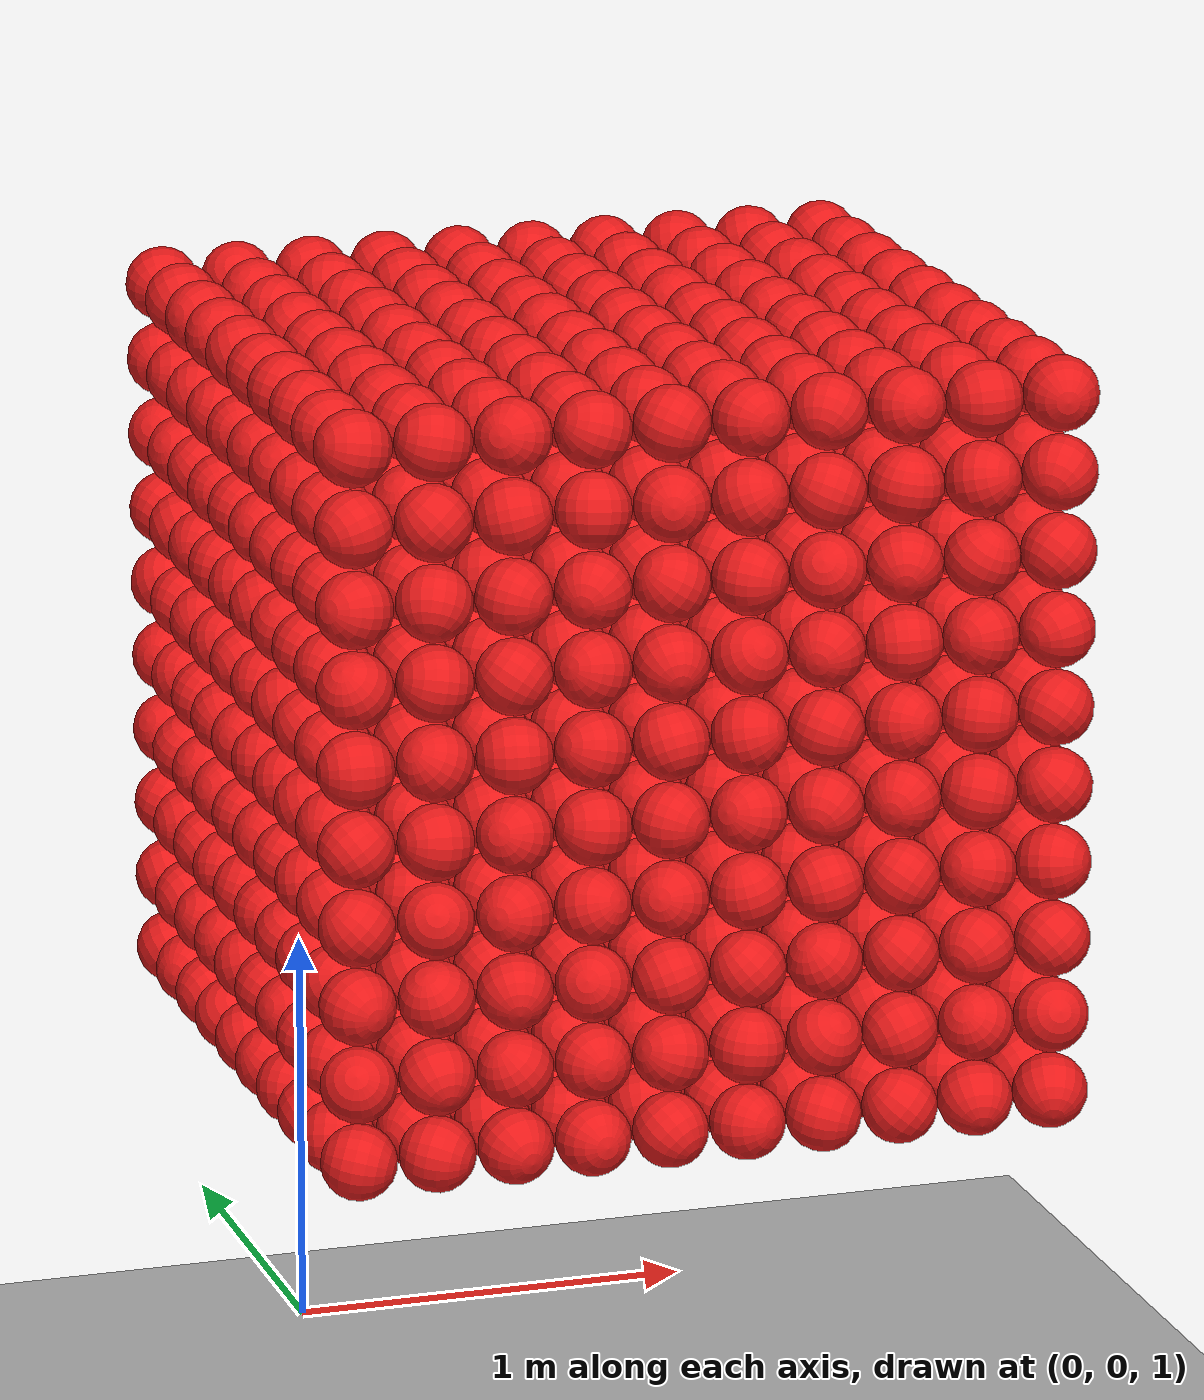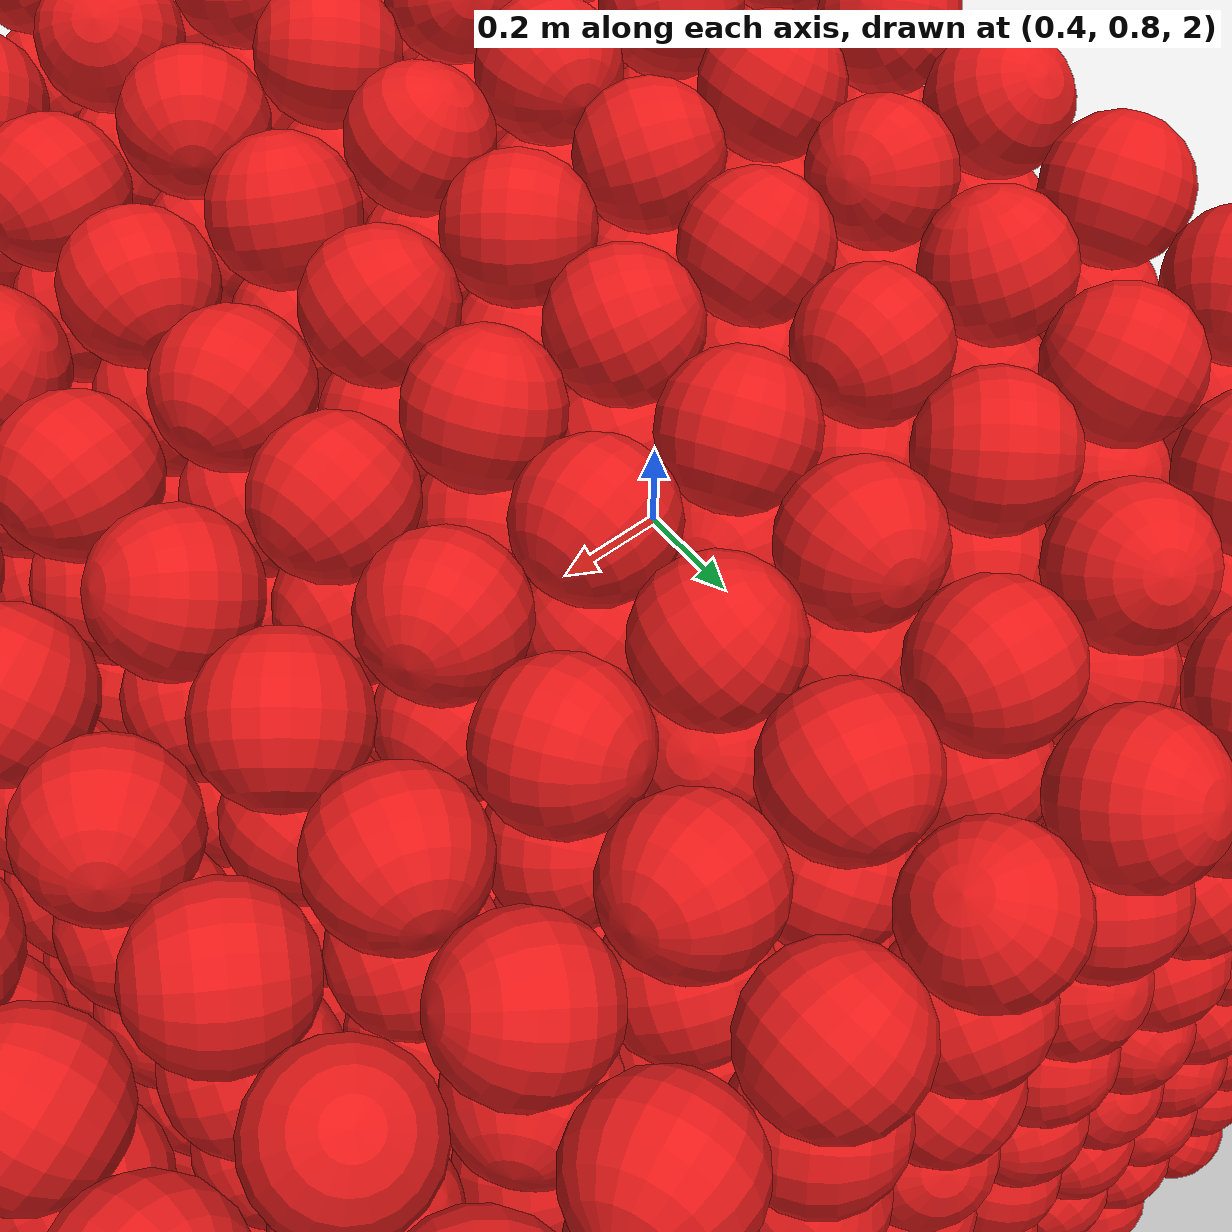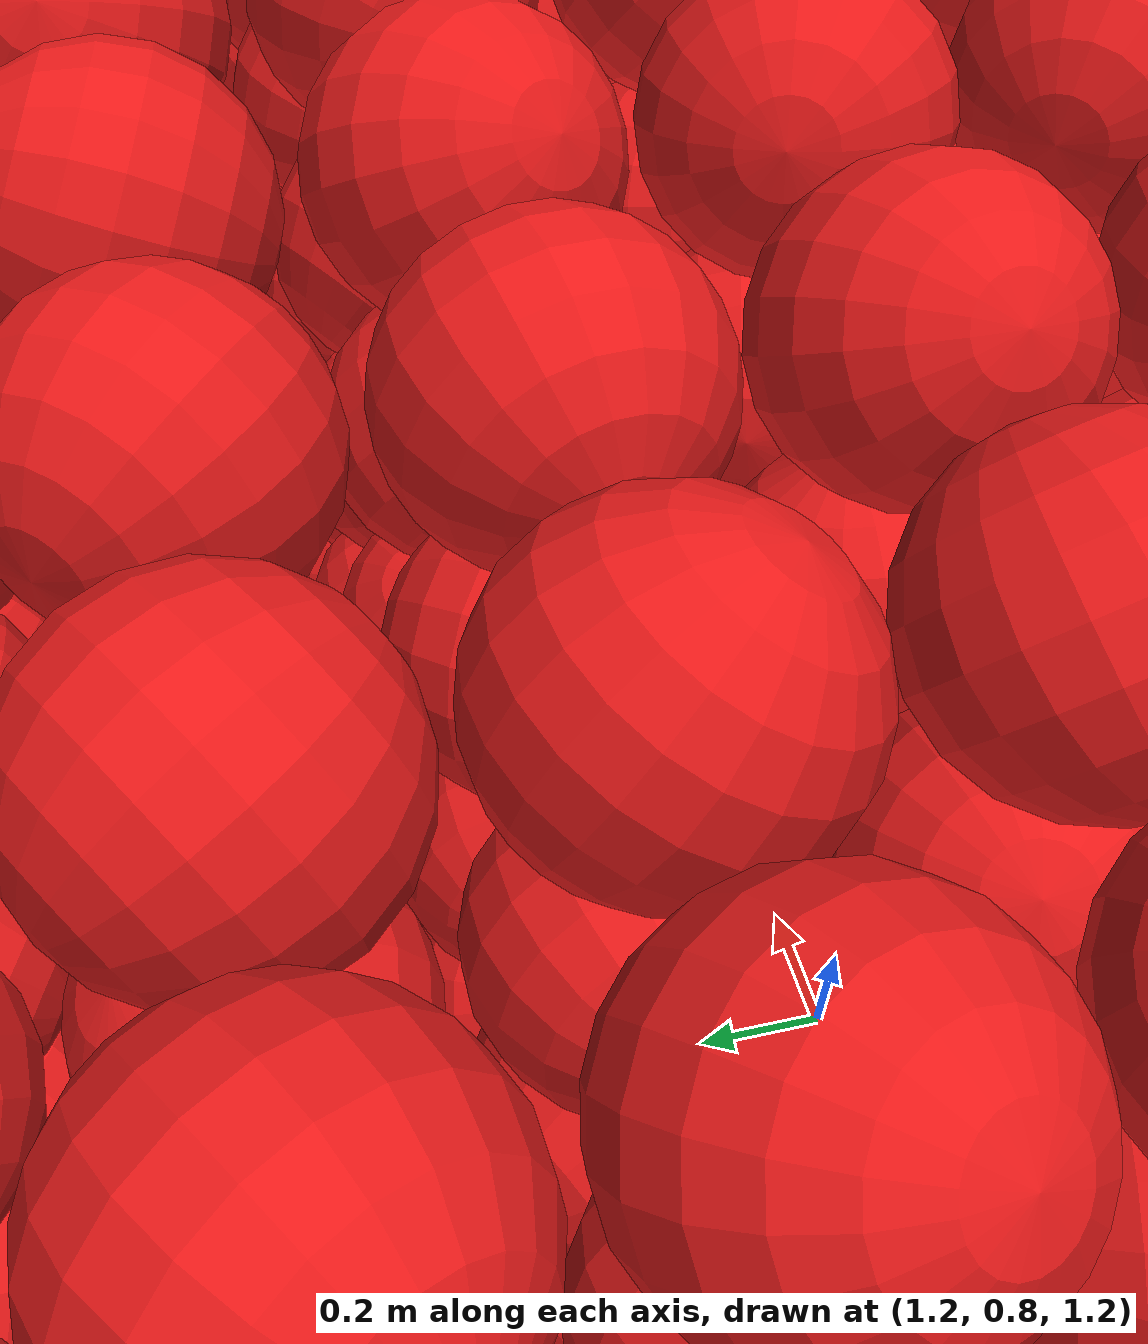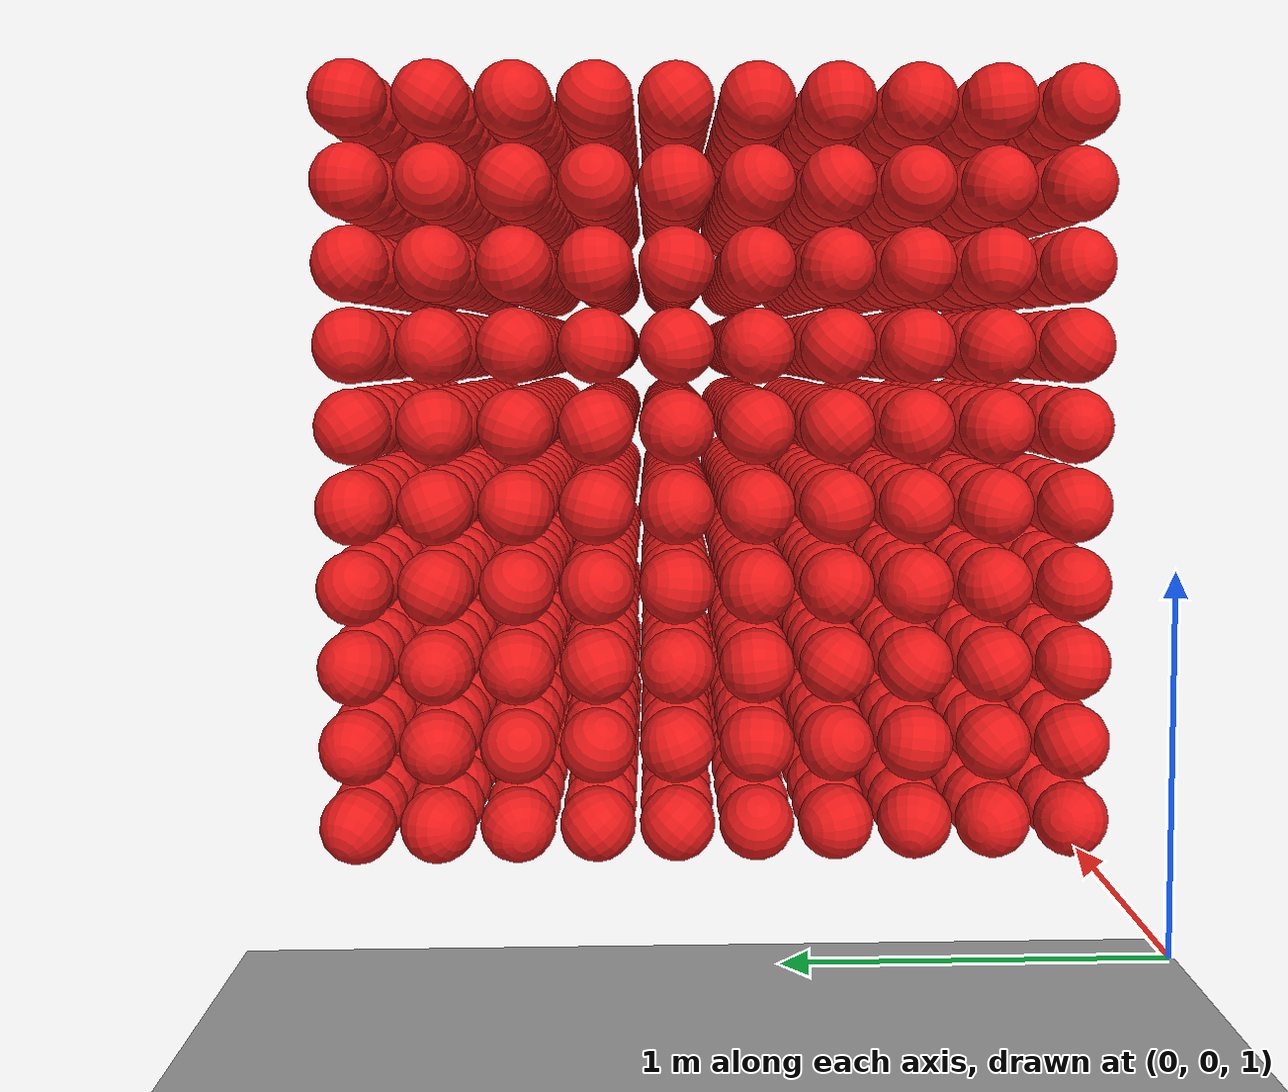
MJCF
<mujoco model="thousand">
    <compiler angle="degree"/>

    <option timestep="0.01" iterations="50" solver="PGS" jacobian="sparse" cone="elliptic" tolerance="1e-10"/>

    <size njmax="5000" nconmax="2000" nstack="1000000000"/>

    <default>
        <geom solimp=".9 .9 .01"/>

        <default class="object5">
			<geom type="sphere" material="geom" rgba=".9 .1 .1 1" size="0.100000"/>
        </default>
    </default>

    <asset>
        <texture type="skybox" builtin="gradient" width="128" height="128" rgb1=".4 .6 .8" rgb2="0 0 0"/>
        <texture name="texgeom" type="cube" builtin="flat" mark="cross" width="128" height="128"
            rgb1="0.6 0.6 0.6" rgb2="0.6 0.6 0.6" markrgb="1 1 1"/>
        <texture name="texplane" type="2d" builtin="checker" rgb1=".4 .4 .4" rgb2=".6 .6 .6"
            width="512" height="512"/>
        <material name='geom' texture="texgeom" texuniform="true"/>
        <material name='MatPlane' reflectance='0.3' texture="texplane" texrepeat="1 1" texuniform="true"/>
    </asset>

    <visual>
        <quality shadowsize="4096" offsamples="8"/>
        <map znear="0.1" force="0.05"/>
    </visual>

    <statistic extent="4"/>

    <worldbody>
        <light directional="true" diffuse=".8 .8 .8" pos="0 0 10" dir="0 0 -10"/>

        <geom pos="0 0 0" type="plane" size="200 200 5" rgba=".7 .7 .7 1" material="MatPlane"/>
		<body pos="0.210468 0.210380 1.311692" quat="-0.545424 -0.650837 -0.415214 -0.326376"><inertial pos="0 0 0" mass="1500.000000" diaginertia="6.000000 6.000000 6.000000"/> <freejoint/> <geom class="object5"/> </body>
		<body pos="0.210987 0.210207 1.521054" quat="-0.571076 -0.195829 0.461707 -0.649884"><inertial pos="0 0 0" mass="1500.000000" diaginertia="6.000000 6.000000 6.000000"/> <freejoint/> <geom class="object5"/> </body>
		<body pos="0.210133 0.210186 1.731951" quat="0.579344 0.525301 0.535649 -0.318590"><inertial pos="0 0 0" mass="1500.000000" diaginertia="6.000000 6.000000 6.000000"/> <freejoint/> <geom class="object5"/> </body>
		<body pos="0.210260 0.210384 1.941876" quat="0.690170 0.196437 -0.332798 -0.611820"><inertial pos="0 0 0" mass="1500.000000" diaginertia="6.000000 6.000000 6.000000"/> <freejoint/> <geom class="object5"/> </body>
		<body pos="0.210202 0.210744 2.151682" quat="0.076650 0.878865 -0.087777 -0.462620"><inertial pos="0 0 0" mass="1500.000000" diaginertia="6.000000 6.000000 6.000000"/> <freejoint/> <geom class="object5"/> </body>
		<body pos="0.210587 0.210640 2.361017" quat="-0.522421 -0.501671 -0.491695 -0.483362"><inertial pos="0 0 0" mass="1500.000000" diaginertia="6.000000 6.000000 6.000000"/> <freejoint/> <geom class="object5"/> </body>
		<body pos="0.210965 0.210083 2.571455" quat="0.620479 0.011746 -0.394014 0.677954"><inertial pos="0 0 0" mass="1500.000000" diaginertia="6.000000 6.000000 6.000000"/> <freejoint/> <geom class="object5"/> </body>
		<body pos="0.210970 0.210673 2.781077" quat="-0.410973 -0.647510 0.008140 0.641690"><inertial pos="0 0 0" mass="1500.000000" diaginertia="6.000000 6.000000 6.000000"/> <freejoint/> <geom class="object5"/> </body>
		<body pos="0.210578 0.210439 2.991602" quat="-0.713003 0.431036 -0.439966 0.335060"><inertial pos="0 0 0" mass="1500.000000" diaginertia="6.000000 6.000000 6.000000"/> <freejoint/> <geom class="object5"/> </body>
		<body pos="0.210356 0.210153 3.201084" quat="0.417262 0.589572 -0.231567 -0.651670"><inertial pos="0 0 0" mass="1500.000000" diaginertia="6.000000 6.000000 6.000000"/> <freejoint/> <geom class="object5"/> </body>
		<body pos="0.210073 0.420892 1.311235" quat="0.603444 -0.029220 0.669451 -0.432247"><inertial pos="0 0 0" mass="1500.000000" diaginertia="6.000000 6.000000 6.000000"/> <freejoint/> <geom class="object5"/> </body>
		<body pos="0.210509 0.420807 1.521750" quat="0.555893 0.081897 0.454306 0.691289"><inertial pos="0 0 0" mass="1500.000000" diaginertia="6.000000 6.000000 6.000000"/> <freejoint/> <geom class="object5"/> </body>
		<body pos="0.210746 0.420062 1.731190" quat="0.343277 -0.544305 0.664042 0.380711"><inertial pos="0 0 0" mass="1500.000000" diaginertia="6.000000 6.000000 6.000000"/> <freejoint/> <geom class="object5"/> </body>
		<body pos="0.210994 0.420317 1.941734" quat="0.928976 -0.249050 -0.157081 0.224285"><inertial pos="0 0 0" mass="1500.000000" diaginertia="6.000000 6.000000 6.000000"/> <freejoint/> <geom class="object5"/> </body>
		<body pos="0.210763 0.420619 2.151315" quat="0.635881 0.554988 -0.536093 0.015757"><inertial pos="0 0 0" mass="1500.000000" diaginertia="6.000000 6.000000 6.000000"/> <freejoint/> <geom class="object5"/> </body>
		<body pos="0.210147 0.420130 2.361661" quat="-0.671934 -0.469878 0.552241 0.150827"><inertial pos="0 0 0" mass="1500.000000" diaginertia="6.000000 6.000000 6.000000"/> <freejoint/> <geom class="object5"/> </body>
		<body pos="0.210677 0.420965 2.571805" quat="0.546785 0.649981 -0.492488 -0.189755"><inertial pos="0 0 0" mass="1500.000000" diaginertia="6.000000 6.000000 6.000000"/> <freejoint/> <geom class="object5"/> </body>
		<body pos="0.210273 0.420215 2.781285" quat="0.508992 -0.179946 0.164838 -0.825454"><inertial pos="0 0 0" mass="1500.000000" diaginertia="6.000000 6.000000 6.000000"/> <freejoint/> <geom class="object5"/> </body>
		<body pos="0.210610 0.420789 2.991061" quat="0.628811 0.156287 0.610035 0.456102"><inertial pos="0 0 0" mass="1500.000000" diaginertia="6.000000 6.000000 6.000000"/> <freejoint/> <geom class="object5"/> </body>
		<body pos="0.210039 0.420445 3.201323" quat="-0.639811 0.693499 -0.274186 -0.185804"><inertial pos="0 0 0" mass="1500.000000" diaginertia="6.000000 6.000000 6.000000"/> <freejoint/> <geom class="object5"/> </body>
		<body pos="0.210911 0.630398 1.311475" quat="0.729888 0.347258 0.296296 0.508807"><inertial pos="0 0 0" mass="1500.000000" diaginertia="6.000000 6.000000 6.000000"/> <freejoint/> <geom class="object5"/> </body>
		<body pos="0.210809 0.630318 1.521010" quat="0.503869 -0.489554 0.443142 0.556847"><inertial pos="0 0 0" mass="1500.000000" diaginertia="6.000000 6.000000 6.000000"/> <freejoint/> <geom class="object5"/> </body>
		<body pos="0.210865 0.630674 1.731556" quat="-0.101554 -0.355016 -0.860246 -0.351606"><inertial pos="0 0 0" mass="1500.000000" diaginertia="6.000000 6.000000 6.000000"/> <freejoint/> <geom class="object5"/> </body>
		<body pos="0.210848 0.630082 1.941140" quat="-0.490450 0.756293 0.126329 -0.414149"><inertial pos="0 0 0" mass="1500.000000" diaginertia="6.000000 6.000000 6.000000"/> <freejoint/> <geom class="object5"/> </body>
		<body pos="0.210780 0.630877 2.151571" quat="0.114968 0.407254 -0.324472 0.845957"><inertial pos="0 0 0" mass="1500.000000" diaginertia="6.000000 6.000000 6.000000"/> <freejoint/> <geom class="object5"/> </body>
		<body pos="0.210117 0.630794 2.361330" quat="-0.892430 0.114637 0.349041 0.261911"><inertial pos="0 0 0" mass="1500.000000" diaginertia="6.000000 6.000000 6.000000"/> <freejoint/> <geom class="object5"/> </body>
		<body pos="0.210752 0.630163 2.571773" quat="0.592097 0.773569 0.093129 0.205766"><inertial pos="0 0 0" mass="1500.000000" diaginertia="6.000000 6.000000 6.000000"/> <freejoint/> <geom class="object5"/> </body>
		<body pos="0.210263 0.630496 2.781991" quat="-0.520127 -0.241005 -0.690118 0.441725"><inertial pos="0 0 0" mass="1500.000000" diaginertia="6.000000 6.000000 6.000000"/> <freejoint/> <geom class="object5"/> </body>
		<body pos="0.210728 0.630801 2.991400" quat="0.554697 0.333798 0.721425 0.245839"><inertial pos="0 0 0" mass="1500.000000" diaginertia="6.000000 6.000000 6.000000"/> <freejoint/> <geom class="object5"/> </body>
		<body pos="0.210661 0.630013 3.201864" quat="-0.616525 -0.465239 -0.630306 0.078510"><inertial pos="0 0 0" mass="1500.000000" diaginertia="6.000000 6.000000 6.000000"/> <freejoint/> <geom class="object5"/> </body>
		<body pos="0.210519 0.840701 1.311785" quat="-0.403870 0.685773 -0.284816 -0.534308"><inertial pos="0 0 0" mass="1500.000000" diaginertia="6.000000 6.000000 6.000000"/> <freejoint/> <geom class="object5"/> </body>
		<body pos="0.210229 0.840140 1.521575" quat="0.427248 -0.754134 0.271101 -0.418622"><inertial pos="0 0 0" mass="1500.000000" diaginertia="6.000000 6.000000 6.000000"/> <freejoint/> <geom class="object5"/> </body>
		<body pos="0.210720 0.840336 1.731478" quat="-0.537615 -0.147130 0.237102 -0.795679"><inertial pos="0 0 0" mass="1500.000000" diaginertia="6.000000 6.000000 6.000000"/> <freejoint/> <geom class="object5"/> </body>
		<body pos="0.210149 0.840150 1.941089" quat="0.479010 0.142293 0.823338 -0.269104"><inertial pos="0 0 0" mass="1500.000000" diaginertia="6.000000 6.000000 6.000000"/> <freejoint/> <geom class="object5"/> </body>
		<body pos="0.210574 0.840272 2.151607" quat="0.514958 0.089524 0.604887 -0.600762"><inertial pos="0 0 0" mass="1500.000000" diaginertia="6.000000 6.000000 6.000000"/> <freejoint/> <geom class="object5"/> </body>
		<body pos="0.210461 0.840504 2.361714" quat="0.329235 0.851069 -0.399365 0.088278"><inertial pos="0 0 0" mass="1500.000000" diaginertia="6.000000 6.000000 6.000000"/> <freejoint/> <geom class="object5"/> </body>
		<body pos="0.210059 0.840252 2.571538" quat="-0.028050 -0.446038 -0.818893 -0.360109"><inertial pos="0 0 0" mass="1500.000000" diaginertia="6.000000 6.000000 6.000000"/> <freejoint/> <geom class="object5"/> </body>
		<body pos="0.210839 0.840630 2.781246" quat="-0.029892 0.686042 0.315239 -0.655040"><inertial pos="0 0 0" mass="1500.000000" diaginertia="6.000000 6.000000 6.000000"/> <freejoint/> <geom class="object5"/> </body>
		<body pos="0.210553 0.840639 2.991378" quat="-0.453903 0.108025 0.472090 -0.747953"><inertial pos="0 0 0" mass="1500.000000" diaginertia="6.000000 6.000000 6.000000"/> <freejoint/> <geom class="object5"/> </body>
		<body pos="0.210417 0.840497 3.201858" quat="0.201385 0.294912 -0.933530 -0.031517"><inertial pos="0 0 0" mass="1500.000000" diaginertia="6.000000 6.000000 6.000000"/> <freejoint/> <geom class="object5"/> </body>
		<body pos="0.210129 1.050673 1.311767" quat="-0.567771 0.328568 0.276213 -0.702415"><inertial pos="0 0 0" mass="1500.000000" diaginertia="6.000000 6.000000 6.000000"/> <freejoint/> <geom class="object5"/> </body>
		<body pos="0.210930 1.050531 1.521203" quat="0.221416 0.596977 -0.742594 -0.207720"><inertial pos="0 0 0" mass="1500.000000" diaginertia="6.000000 6.000000 6.000000"/> <freejoint/> <geom class="object5"/> </body>
		<body pos="0.210781 1.050923 1.731394" quat="-0.169384 0.255788 0.700212 0.644658"><inertial pos="0 0 0" mass="1500.000000" diaginertia="6.000000 6.000000 6.000000"/> <freejoint/> <geom class="object5"/> </body>
		<body pos="0.210368 1.050563 1.941800" quat="0.604425 0.643837 -0.131882 -0.450279"><inertial pos="0 0 0" mass="1500.000000" diaginertia="6.000000 6.000000 6.000000"/> <freejoint/> <geom class="object5"/> </body>
		<body pos="0.210200 1.050003 2.151984" quat="0.718637 0.471919 0.503051 0.088276"><inertial pos="0 0 0" mass="1500.000000" diaginertia="6.000000 6.000000 6.000000"/> <freejoint/> <geom class="object5"/> </body>
		<body pos="0.210711 1.050063 2.361062" quat="0.169380 -0.403134 -0.793192 0.423839"><inertial pos="0 0 0" mass="1500.000000" diaginertia="6.000000 6.000000 6.000000"/> <freejoint/> <geom class="object5"/> </body>
		<body pos="0.210425 1.050990 2.571070" quat="-0.497302 0.620369 0.499595 -0.343856"><inertial pos="0 0 0" mass="1500.000000" diaginertia="6.000000 6.000000 6.000000"/> <freejoint/> <geom class="object5"/> </body>
		<body pos="0.210516 1.050079 2.781636" quat="0.240623 0.371592 0.703200 0.556354"><inertial pos="0 0 0" mass="1500.000000" diaginertia="6.000000 6.000000 6.000000"/> <freejoint/> <geom class="object5"/> </body>
		<body pos="0.210055 1.050082 2.991543" quat="-0.270124 -0.388172 -0.725382 -0.500177"><inertial pos="0 0 0" mass="1500.000000" diaginertia="6.000000 6.000000 6.000000"/> <freejoint/> <geom class="object5"/> </body>
		<body pos="0.210951 1.050338 3.201498" quat="-0.291513 0.362101 -0.077064 0.882022"><inertial pos="0 0 0" mass="1500.000000" diaginertia="6.000000 6.000000 6.000000"/> <freejoint/> <geom class="object5"/> </body>
		<body pos="0.210260 1.260680 1.311531" quat="-0.688743 0.270455 -0.306098 -0.598991"><inertial pos="0 0 0" mass="1500.000000" diaginertia="6.000000 6.000000 6.000000"/> <freejoint/> <geom class="object5"/> </body>
		<body pos="0.210468 1.260682 1.521780" quat="0.906767 -0.199075 0.011924 0.371485"><inertial pos="0 0 0" mass="1500.000000" diaginertia="6.000000 6.000000 6.000000"/> <freejoint/> <geom class="object5"/> </body>
		<body pos="0.210727 1.260413 1.731356" quat="-0.625155 -0.131577 0.574694 0.511463"><inertial pos="0 0 0" mass="1500.000000" diaginertia="6.000000 6.000000 6.000000"/> <freejoint/> <geom class="object5"/> </body>
		<body pos="0.210344 1.260589 1.941847" quat="-0.484758 -0.306225 -0.683640 0.451523"><inertial pos="0 0 0" mass="1500.000000" diaginertia="6.000000 6.000000 6.000000"/> <freejoint/> <geom class="object5"/> </body>
		<body pos="0.210796 1.260396 2.151320" quat="0.630216 0.065232 -0.621933 0.460186"><inertial pos="0 0 0" mass="1500.000000" diaginertia="6.000000 6.000000 6.000000"/> <freejoint/> <geom class="object5"/> </body>
		<body pos="0.210594 1.260861 2.361777" quat="-0.629467 -0.168566 0.758339 0.016712"><inertial pos="0 0 0" mass="1500.000000" diaginertia="6.000000 6.000000 6.000000"/> <freejoint/> <geom class="object5"/> </body>
		<body pos="0.210393 1.260555 2.571975" quat="-0.079818 0.557653 -0.546923 -0.619295"><inertial pos="0 0 0" mass="1500.000000" diaginertia="6.000000 6.000000 6.000000"/> <freejoint/> <geom class="object5"/> </body>
		<body pos="0.210348 1.260073 2.781544" quat="0.618485 -0.290809 -0.557976 -0.470710"><inertial pos="0 0 0" mass="1500.000000" diaginertia="6.000000 6.000000 6.000000"/> <freejoint/> <geom class="object5"/> </body>
		<body pos="0.210163 1.260539 2.991469" quat="-0.437214 0.325161 -0.699464 -0.462454"><inertial pos="0 0 0" mass="1500.000000" diaginertia="6.000000 6.000000 6.000000"/> <freejoint/> <geom class="object5"/> </body>
		<body pos="0.210589 1.260351 3.201523" quat="-0.320874 -0.927536 -0.191401 0.009117"><inertial pos="0 0 0" mass="1500.000000" diaginertia="6.000000 6.000000 6.000000"/> <freejoint/> <geom class="object5"/> </body>
		<body pos="0.210130 1.470613 1.311963" quat="-0.898420 -0.418922 0.063962 -0.115131"><inertial pos="0 0 0" mass="1500.000000" diaginertia="6.000000 6.000000 6.000000"/> <freejoint/> <geom class="object5"/> </body>
		<body pos="0.210940 1.470721 1.521738" quat="0.259143 -0.865508 0.263768 -0.337887"><inertial pos="0 0 0" mass="1500.000000" diaginertia="6.000000 6.000000 6.000000"/> <freejoint/> <geom class="object5"/> </body>
		<body pos="0.210101 1.470081 1.731902" quat="-0.686960 -0.014147 -0.310849 -0.656703"><inertial pos="0 0 0" mass="1500.000000" diaginertia="6.000000 6.000000 6.000000"/> <freejoint/> <geom class="object5"/> </body>
		<body pos="0.210263 1.470700 1.941057" quat="0.586961 -0.422249 0.690077 -0.031239"><inertial pos="0 0 0" mass="1500.000000" diaginertia="6.000000 6.000000 6.000000"/> <freejoint/> <geom class="object5"/> </body>
		<body pos="0.210233 1.470221 2.151314" quat="0.648740 -0.407068 0.458952 0.450328"><inertial pos="0 0 0" mass="1500.000000" diaginertia="6.000000 6.000000 6.000000"/> <freejoint/> <geom class="object5"/> </body>
		<body pos="0.210528 1.470665 2.361370" quat="-0.300113 0.510139 -0.653245 -0.472187"><inertial pos="0 0 0" mass="1500.000000" diaginertia="6.000000 6.000000 6.000000"/> <freejoint/> <geom class="object5"/> </body>
		<body pos="0.210446 1.470387 2.571775" quat="-0.034323 0.395318 -0.632875 0.664842"><inertial pos="0 0 0" mass="1500.000000" diaginertia="6.000000 6.000000 6.000000"/> <freejoint/> <geom class="object5"/> </body>
		<body pos="0.210283 1.470768 2.781035" quat="0.532768 0.349480 -0.562038 0.527384"><inertial pos="0 0 0" mass="1500.000000" diaginertia="6.000000 6.000000 6.000000"/> <freejoint/> <geom class="object5"/> </body>
		<body pos="0.210822 1.470004 2.991660" quat="0.244468 -0.534720 -0.120149 0.799922"><inertial pos="0 0 0" mass="1500.000000" diaginertia="6.000000 6.000000 6.000000"/> <freejoint/> <geom class="object5"/> </body>
		<body pos="0.210457 1.470110 3.201680" quat="0.706785 -0.096823 -0.392610 0.580463"><inertial pos="0 0 0" mass="1500.000000" diaginertia="6.000000 6.000000 6.000000"/> <freejoint/> <geom class="object5"/> </body>
		<body pos="0.210953 1.680392 1.311763" quat="-0.506599 -0.349774 -0.503527 -0.606198"><inertial pos="0 0 0" mass="1500.000000" diaginertia="6.000000 6.000000 6.000000"/> <freejoint/> <geom class="object5"/> </body>
		<body pos="0.210517 1.680259 1.521034" quat="0.540070 0.090225 0.826166 0.132790"><inertial pos="0 0 0" mass="1500.000000" diaginertia="6.000000 6.000000 6.000000"/> <freejoint/> <geom class="object5"/> </body>
		<body pos="0.210969 1.680752 1.731949" quat="0.423710 -0.419560 -0.731895 0.329801"><inertial pos="0 0 0" mass="1500.000000" diaginertia="6.000000 6.000000 6.000000"/> <freejoint/> <geom class="object5"/> </body>
		<body pos="0.210810 1.680151 1.941314" quat="-0.025971 0.407695 0.192375 -0.892246"><inertial pos="0 0 0" mass="1500.000000" diaginertia="6.000000 6.000000 6.000000"/> <freejoint/> <geom class="object5"/> </body>
		<body pos="0.210971 1.680574 2.151574" quat="0.127722 0.167065 -0.602545 -0.769880"><inertial pos="0 0 0" mass="1500.000000" diaginertia="6.000000 6.000000 6.000000"/> <freejoint/> <geom class="object5"/> </body>
		<body pos="0.210414 1.680273 2.361690" quat="0.769165 -0.400881 0.421890 0.263986"><inertial pos="0 0 0" mass="1500.000000" diaginertia="6.000000 6.000000 6.000000"/> <freejoint/> <geom class="object5"/> </body>
		<body pos="0.210536 1.680901 2.571667" quat="0.055779 -0.528064 -0.607112 0.591145"><inertial pos="0 0 0" mass="1500.000000" diaginertia="6.000000 6.000000 6.000000"/> <freejoint/> <geom class="object5"/> </body>
		<body pos="0.210732 1.680891 2.781895" quat="0.734069 0.087836 -0.393066 -0.546742"><inertial pos="0 0 0" mass="1500.000000" diaginertia="6.000000 6.000000 6.000000"/> <freejoint/> <geom class="object5"/> </body>
		<body pos="0.210474 1.680009 2.991425" quat="0.797482 -0.327295 0.382563 0.332484"><inertial pos="0 0 0" mass="1500.000000" diaginertia="6.000000 6.000000 6.000000"/> <freejoint/> <geom class="object5"/> </body>
		<body pos="0.210979 1.680276 3.201043" quat="0.566896 0.593189 -0.195845 -0.537030"><inertial pos="0 0 0" mass="1500.000000" diaginertia="6.000000 6.000000 6.000000"/> <freejoint/> <geom class="object5"/> </body>
		<body pos="0.210169 1.890163 1.311595" quat="0.553582 -0.718053 0.141931 -0.397244"><inertial pos="0 0 0" mass="1500.000000" diaginertia="6.000000 6.000000 6.000000"/> <freejoint/> <geom class="object5"/> </body>
		<body pos="0.210218 1.890728 1.521183" quat="-0.760827 -0.090767 -0.592857 -0.247841"><inertial pos="0 0 0" mass="1500.000000" diaginertia="6.000000 6.000000 6.000000"/> <freejoint/> <geom class="object5"/> </body>
		<body pos="0.210184 1.890887 1.731213" quat="0.091067 -0.712629 -0.110127 0.686832"><inertial pos="0 0 0" mass="1500.000000" diaginertia="6.000000 6.000000 6.000000"/> <freejoint/> <geom class="object5"/> </body>
		<body pos="0.210473 1.890880 1.941656" quat="0.147410 0.057109 -0.229664 0.960345"><inertial pos="0 0 0" mass="1500.000000" diaginertia="6.000000 6.000000 6.000000"/> <freejoint/> <geom class="object5"/> </body>
		<body pos="0.210642 1.890184 2.151998" quat="-0.036632 0.029134 0.833356 0.550751"><inertial pos="0 0 0" mass="1500.000000" diaginertia="6.000000 6.000000 6.000000"/> <freejoint/> <geom class="object5"/> </body>
		<body pos="0.210725 1.890222 2.361383" quat="-0.239132 0.531386 0.738779 -0.338600"><inertial pos="0 0 0" mass="1500.000000" diaginertia="6.000000 6.000000 6.000000"/> <freejoint/> <geom class="object5"/> </body>
		<body pos="0.210976 1.890602 2.571187" quat="-0.073435 -0.752631 0.400444 0.517493"><inertial pos="0 0 0" mass="1500.000000" diaginertia="6.000000 6.000000 6.000000"/> <freejoint/> <geom class="object5"/> </body>
		<body pos="0.210480 1.890683 2.781718" quat="-0.422757 -0.529268 -0.028419 0.735081"><inertial pos="0 0 0" mass="1500.000000" diaginertia="6.000000 6.000000 6.000000"/> <freejoint/> <geom class="object5"/> </body>
		<body pos="0.210881 1.890039 2.991949" quat="0.539830 -0.395294 0.662246 -0.337277"><inertial pos="0 0 0" mass="1500.000000" diaginertia="6.000000 6.000000 6.000000"/> <freejoint/> <geom class="object5"/> </body>
		<body pos="0.210627 1.890519 3.201495" quat="-0.404912 -0.697092 -0.529808 0.263462"><inertial pos="0 0 0" mass="1500.000000" diaginertia="6.000000 6.000000 6.000000"/> <freejoint/> <geom class="object5"/> </body>
		<body pos="0.210706 2.100858 1.311270" quat="-0.676255 0.082321 -0.426296 0.595125"><inertial pos="0 0 0" mass="1500.000000" diaginertia="6.000000 6.000000 6.000000"/> <freejoint/> <geom class="object5"/> </body>
		<body pos="0.210275 2.100229 1.521518" quat="-0.295890 -0.586893 0.577959 0.483704"><inertial pos="0 0 0" mass="1500.000000" diaginertia="6.000000 6.000000 6.000000"/> <freejoint/> <geom class="object5"/> </body>
		<body pos="0.210959 2.100845 1.731381" quat="-0.804657 0.456322 0.357967 -0.127113"><inertial pos="0 0 0" mass="1500.000000" diaginertia="6.000000 6.000000 6.000000"/> <freejoint/> <geom class="object5"/> </body>
		<body pos="0.210143 2.100307 1.941680" quat="0.007682 0.456909 0.288215 -0.841491"><inertial pos="0 0 0" mass="1500.000000" diaginertia="6.000000 6.000000 6.000000"/> <freejoint/> <geom class="object5"/> </body>
		<body pos="0.210995 2.100181 2.151460" quat="0.135167 0.347573 0.694776 0.614987"><inertial pos="0 0 0" mass="1500.000000" diaginertia="6.000000 6.000000 6.000000"/> <freejoint/> <geom class="object5"/> </body>
		<body pos="0.210297 2.100180 2.361842" quat="0.701600 0.490296 -0.102404 0.506835"><inertial pos="0 0 0" mass="1500.000000" diaginertia="6.000000 6.000000 6.000000"/> <freejoint/> <geom class="object5"/> </body>
		<body pos="0.210378 2.100866 2.571480" quat="-0.174978 -0.890424 0.245510 0.340958"><inertial pos="0 0 0" mass="1500.000000" diaginertia="6.000000 6.000000 6.000000"/> <freejoint/> <geom class="object5"/> </body>
		<body pos="0.210144 2.100721 2.781200" quat="-0.505936 0.455858 -0.710017 -0.179160"><inertial pos="0 0 0" mass="1500.000000" diaginertia="6.000000 6.000000 6.000000"/> <freejoint/> <geom class="object5"/> </body>
		<body pos="0.210208 2.100139 2.991814" quat="-0.273992 -0.031010 -0.691610 -0.667565"><inertial pos="0 0 0" mass="1500.000000" diaginertia="6.000000 6.000000 6.000000"/> <freejoint/> <geom class="object5"/> </body>
		<body pos="0.210317 2.100315 3.201338" quat="0.290879 -0.150660 0.627125 0.706686"><inertial pos="0 0 0" mass="1500.000000" diaginertia="6.000000 6.000000 6.000000"/> <freejoint/> <geom class="object5"/> </body>
		<body pos="0.420550 0.210338 1.311542" quat="-0.430532 -0.227683 0.604006 0.630856"><inertial pos="0 0 0" mass="1500.000000" diaginertia="6.000000 6.000000 6.000000"/> <freejoint/> <geom class="object5"/> </body>
		<body pos="0.420074 0.210945 1.521015" quat="-0.719382 0.434036 -0.217381 -0.496839"><inertial pos="0 0 0" mass="1500.000000" diaginertia="6.000000 6.000000 6.000000"/> <freejoint/> <geom class="object5"/> </body>
		<body pos="0.420836 0.210858 1.731773" quat="-0.288924 0.889377 -0.332661 0.121932"><inertial pos="0 0 0" mass="1500.000000" diaginertia="6.000000 6.000000 6.000000"/> <freejoint/> <geom class="object5"/> </body>
		<body pos="0.420221 0.210587 1.941317" quat="0.292184 -0.610495 -0.583030 -0.449444"><inertial pos="0 0 0" mass="1500.000000" diaginertia="6.000000 6.000000 6.000000"/> <freejoint/> <geom class="object5"/> </body>
		<body pos="0.420193 0.210156 2.151272" quat="-0.371670 -0.544357 -0.502586 -0.559415"><inertial pos="0 0 0" mass="1500.000000" diaginertia="6.000000 6.000000 6.000000"/> <freejoint/> <geom class="object5"/> </body>
		<body pos="0.420613 0.210271 2.361470" quat="-0.492718 0.472683 -0.730339 0.020126"><inertial pos="0 0 0" mass="1500.000000" diaginertia="6.000000 6.000000 6.000000"/> <freejoint/> <geom class="object5"/> </body>
		<body pos="0.420918 0.210748 2.571780" quat="-0.214540 0.738619 -0.231289 0.595752"><inertial pos="0 0 0" mass="1500.000000" diaginertia="6.000000 6.000000 6.000000"/> <freejoint/> <geom class="object5"/> </body>
		<body pos="0.420735 0.210422 2.781514" quat="-0.322980 -0.758319 0.564164 -0.048524"><inertial pos="0 0 0" mass="1500.000000" diaginertia="6.000000 6.000000 6.000000"/> <freejoint/> <geom class="object5"/> </body>
		<body pos="0.420144 0.210486 2.991907" quat="-0.143386 0.373895 -0.093588 -0.911528"><inertial pos="0 0 0" mass="1500.000000" diaginertia="6.000000 6.000000 6.000000"/> <freejoint/> <geom class="object5"/> </body>
		<body pos="0.420349 0.210298 3.201005" quat="-0.475473 0.534179 0.335249 -0.613340"><inertial pos="0 0 0" mass="1500.000000" diaginertia="6.000000 6.000000 6.000000"/> <freejoint/> <geom class="object5"/> </body>
		<body pos="0.420149 0.420940 1.311881" quat="-0.602571 -0.126378 0.748643 -0.245909"><inertial pos="0 0 0" mass="1500.000000" diaginertia="6.000000 6.000000 6.000000"/> <freejoint/> <geom class="object5"/> </body>
		<body pos="0.420536 0.420950 1.521498" quat="0.530471 0.393836 -0.571056 0.487225"><inertial pos="0 0 0" mass="1500.000000" diaginertia="6.000000 6.000000 6.000000"/> <freejoint/> <geom class="object5"/> </body>
		<body pos="0.420014 0.420723 1.731492" quat="-0.438796 0.687674 0.557257 -0.155009"><inertial pos="0 0 0" mass="1500.000000" diaginertia="6.000000 6.000000 6.000000"/> <freejoint/> <geom class="object5"/> </body>
		<body pos="0.420822 0.420816 1.941816" quat="0.001978 -0.627138 0.156697 0.762981"><inertial pos="0 0 0" mass="1500.000000" diaginertia="6.000000 6.000000 6.000000"/> <freejoint/> <geom class="object5"/> </body>
		<body pos="0.420290 0.420354 2.151330" quat="0.433259 0.378493 -0.422146 0.700587"><inertial pos="0 0 0" mass="1500.000000" diaginertia="6.000000 6.000000 6.000000"/> <freejoint/> <geom class="object5"/> </body>
		<body pos="0.420085 0.420068 2.361968" quat="0.250631 0.541398 -0.710586 -0.373015"><inertial pos="0 0 0" mass="1500.000000" diaginertia="6.000000 6.000000 6.000000"/> <freejoint/> <geom class="object5"/> </body>
		<body pos="0.420001 0.420559 2.571922" quat="-0.123958 -0.341723 0.029611 -0.931119"><inertial pos="0 0 0" mass="1500.000000" diaginertia="6.000000 6.000000 6.000000"/> <freejoint/> <geom class="object5"/> </body>
		<body pos="0.420764 0.420388 2.781148" quat="-0.195998 -0.387942 -0.342349 -0.832996"><inertial pos="0 0 0" mass="1500.000000" diaginertia="6.000000 6.000000 6.000000"/> <freejoint/> <geom class="object5"/> </body>
		<body pos="0.420239 0.420462 2.991141" quat="-0.856352 -0.326746 0.185123 0.354441"><inertial pos="0 0 0" mass="1500.000000" diaginertia="6.000000 6.000000 6.000000"/> <freejoint/> <geom class="object5"/> </body>
		<body pos="0.420332 0.420215 3.201149" quat="0.160690 -0.455462 0.408457 0.774530"><inertial pos="0 0 0" mass="1500.000000" diaginertia="6.000000 6.000000 6.000000"/> <freejoint/> <geom class="object5"/> </body>
		<body pos="0.420811 0.630683 1.311283" quat="0.057012 0.142971 -0.050710 -0.986781"><inertial pos="0 0 0" mass="1500.000000" diaginertia="6.000000 6.000000 6.000000"/> <freejoint/> <geom class="object5"/> </body>
		<body pos="0.420342 0.630865 1.521247" quat="-0.651860 0.054672 -0.244074 0.715903"><inertial pos="0 0 0" mass="1500.000000" diaginertia="6.000000 6.000000 6.000000"/> <freejoint/> <geom class="object5"/> </body>
		<body pos="0.420709 0.630685 1.731310" quat="-0.762238 -0.276954 0.391754 -0.434532"><inertial pos="0 0 0" mass="1500.000000" diaginertia="6.000000 6.000000 6.000000"/> <freejoint/> <geom class="object5"/> </body>
		<body pos="0.420955 0.630016 1.941812" quat="-0.753300 -0.612040 -0.125217 0.205591"><inertial pos="0 0 0" mass="1500.000000" diaginertia="6.000000 6.000000 6.000000"/> <freejoint/> <geom class="object5"/> </body>
		<body pos="0.420594 0.630967 2.151476" quat="0.504662 0.485583 0.487100 -0.521784"><inertial pos="0 0 0" mass="1500.000000" diaginertia="6.000000 6.000000 6.000000"/> <freejoint/> <geom class="object5"/> </body>
		<body pos="0.420695 0.630305 2.361379" quat="0.861543 0.023583 0.386199 -0.328691"><inertial pos="0 0 0" mass="1500.000000" diaginertia="6.000000 6.000000 6.000000"/> <freejoint/> <geom class="object5"/> </body>
		<body pos="0.420198 0.630504 2.571470" quat="-0.617606 -0.055158 -0.034270 -0.783802"><inertial pos="0 0 0" mass="1500.000000" diaginertia="6.000000 6.000000 6.000000"/> <freejoint/> <geom class="object5"/> </body>
		<body pos="0.420091 0.630318 2.781995" quat="0.327419 0.707467 -0.619240 0.093964"><inertial pos="0 0 0" mass="1500.000000" diaginertia="6.000000 6.000000 6.000000"/> <freejoint/> <geom class="object5"/> </body>
		<body pos="0.420023 0.630823 2.991241" quat="0.323051 0.273791 -0.722844 0.546053"><inertial pos="0 0 0" mass="1500.000000" diaginertia="6.000000 6.000000 6.000000"/> <freejoint/> <geom class="object5"/> </body>
		<body pos="0.420332 0.630236 3.201711" quat="-0.490607 0.043006 -0.192834 0.848687"><inertial pos="0 0 0" mass="1500.000000" diaginertia="6.000000 6.000000 6.000000"/> <freejoint/> <geom class="object5"/> </body>
		<body pos="0.420543 0.840918 1.311139" quat="0.519512 -0.289470 0.574087 -0.562795"><inertial pos="0 0 0" mass="1500.000000" diaginertia="6.000000 6.000000 6.000000"/> <freejoint/> <geom class="object5"/> </body>
		<body pos="0.420551 0.840012 1.521140" quat="0.656143 0.255553 0.607939 0.366850"><inertial pos="0 0 0" mass="1500.000000" diaginertia="6.000000 6.000000 6.000000"/> <freejoint/> <geom class="object5"/> </body>
		<body pos="0.420140 0.840669 1.731467" quat="0.679316 0.614231 0.330068 0.228703"><inertial pos="0 0 0" mass="1500.000000" diaginertia="6.000000 6.000000 6.000000"/> <freejoint/> <geom class="object5"/> </body>
		<body pos="0.420257 0.840704 1.941736" quat="0.471984 -0.188315 -0.783188 0.358308"><inertial pos="0 0 0" mass="1500.000000" diaginertia="6.000000 6.000000 6.000000"/> <freejoint/> <geom class="object5"/> </body>
		<body pos="0.420396 0.840836 2.151244" quat="0.664031 0.585580 -0.260988 0.384764"><inertial pos="0 0 0" mass="1500.000000" diaginertia="6.000000 6.000000 6.000000"/> <freejoint/> <geom class="object5"/> </body>
		<body pos="0.420755 0.840597 2.361143" quat="-0.626941 0.502273 0.127940 -0.581634"><inertial pos="0 0 0" mass="1500.000000" diaginertia="6.000000 6.000000 6.000000"/> <freejoint/> <geom class="object5"/> </body>
		<body pos="0.420247 0.840847 2.571072" quat="0.528942 0.646204 -0.218177 0.505014"><inertial pos="0 0 0" mass="1500.000000" diaginertia="6.000000 6.000000 6.000000"/> <freejoint/> <geom class="object5"/> </body>
		<body pos="0.420811 0.840179 2.781694" quat="0.279054 0.849523 -0.201927 0.399581"><inertial pos="0 0 0" mass="1500.000000" diaginertia="6.000000 6.000000 6.000000"/> <freejoint/> <geom class="object5"/> </body>
		<body pos="0.420076 0.840075 2.991535" quat="-0.210990 -0.228613 0.866491 0.390399"><inertial pos="0 0 0" mass="1500.000000" diaginertia="6.000000 6.000000 6.000000"/> <freejoint/> <geom class="object5"/> </body>
		<body pos="0.420346 0.840244 3.201756" quat="0.644671 -0.256986 -0.714519 0.088428"><inertial pos="0 0 0" mass="1500.000000" diaginertia="6.000000 6.000000 6.000000"/> <freejoint/> <geom class="object5"/> </body>
		<body pos="0.420417 1.050224 1.311478" quat="-0.002884 0.427186 -0.889115 0.164254"><inertial pos="0 0 0" mass="1500.000000" diaginertia="6.000000 6.000000 6.000000"/> <freejoint/> <geom class="object5"/> </body>
		<body pos="0.420520 1.050478 1.521581" quat="-0.212707 0.819465 0.343698 -0.406330"><inertial pos="0 0 0" mass="1500.000000" diaginertia="6.000000 6.000000 6.000000"/> <freejoint/> <geom class="object5"/> </body>
		<body pos="0.420964 1.050016 1.731222" quat="0.549519 0.466120 -0.329791 0.609917"><inertial pos="0 0 0" mass="1500.000000" diaginertia="6.000000 6.000000 6.000000"/> <freejoint/> <geom class="object5"/> </body>
		<body pos="0.420927 1.050751 1.941442" quat="0.069155 0.608801 0.774939 0.155075"><inertial pos="0 0 0" mass="1500.000000" diaginertia="6.000000 6.000000 6.000000"/> <freejoint/> <geom class="object5"/> </body>
		<body pos="0.420586 1.050883 2.151791" quat="0.054704 0.221845 0.620108 -0.750506"><inertial pos="0 0 0" mass="1500.000000" diaginertia="6.000000 6.000000 6.000000"/> <freejoint/> <geom class="object5"/> </body>
		<body pos="0.420329 1.050148 2.361727" quat="-0.206384 0.167844 -0.777775 -0.569474"><inertial pos="0 0 0" mass="1500.000000" diaginertia="6.000000 6.000000 6.000000"/> <freejoint/> <geom class="object5"/> </body>
		<body pos="0.420964 1.050720 2.571915" quat="0.855092 -0.008671 0.515225 -0.057319"><inertial pos="0 0 0" mass="1500.000000" diaginertia="6.000000 6.000000 6.000000"/> <freejoint/> <geom class="object5"/> </body>
		<body pos="0.420412 1.050274 2.781885" quat="0.968295 -0.101015 -0.192389 0.123235"><inertial pos="0 0 0" mass="1500.000000" diaginertia="6.000000 6.000000 6.000000"/> <freejoint/> <geom class="object5"/> </body>
		<body pos="0.420790 1.050059 2.991466" quat="0.579887 0.431379 0.372476 0.582156"><inertial pos="0 0 0" mass="1500.000000" diaginertia="6.000000 6.000000 6.000000"/> <freejoint/> <geom class="object5"/> </body>
		<body pos="0.420455 1.050226 3.201936" quat="0.280577 0.533012 0.768468 0.215947"><inertial pos="0 0 0" mass="1500.000000" diaginertia="6.000000 6.000000 6.000000"/> <freejoint/> <geom class="object5"/> </body>
		<body pos="0.420395 1.260618 1.311677" quat="-0.648328 0.320938 -0.598117 -0.344855"><inertial pos="0 0 0" mass="1500.000000" diaginertia="6.000000 6.000000 6.000000"/> <freejoint/> <geom class="object5"/> </body>
		<body pos="0.420729 1.260436 1.521001" quat="-0.607974 -0.242542 0.486241 0.578888"><inertial pos="0 0 0" mass="1500.000000" diaginertia="6.000000 6.000000 6.000000"/> <freejoint/> <geom class="object5"/> </body>
		<body pos="0.420241 1.260035 1.731952" quat="0.070963 -0.790499 -0.319493 -0.517687"><inertial pos="0 0 0" mass="1500.000000" diaginertia="6.000000 6.000000 6.000000"/> <freejoint/> <geom class="object5"/> </body>
		<body pos="0.420581 1.260641 1.941119" quat="-0.648929 -0.026535 -0.478896 0.590631"><inertial pos="0 0 0" mass="1500.000000" diaginertia="6.000000 6.000000 6.000000"/> <freejoint/> <geom class="object5"/> </body>
		<body pos="0.420412 1.260404 2.151153" quat="0.543142 0.546429 -0.589611 -0.242427"><inertial pos="0 0 0" mass="1500.000000" diaginertia="6.000000 6.000000 6.000000"/> <freejoint/> <geom class="object5"/> </body>
		<body pos="0.420693 1.260171 2.361346" quat="-0.237074 -0.278207 0.729847 -0.577686"><inertial pos="0 0 0" mass="1500.000000" diaginertia="6.000000 6.000000 6.000000"/> <freejoint/> <geom class="object5"/> </body>
		<body pos="0.420193 1.260966 2.571461" quat="0.420554 -0.739850 -0.509697 0.126357"><inertial pos="0 0 0" mass="1500.000000" diaginertia="6.000000 6.000000 6.000000"/> <freejoint/> <geom class="object5"/> </body>
		<body pos="0.420324 1.260957 2.781590" quat="-0.626414 -0.368208 -0.584324 0.361378"><inertial pos="0 0 0" mass="1500.000000" diaginertia="6.000000 6.000000 6.000000"/> <freejoint/> <geom class="object5"/> </body>
		<body pos="0.420755 1.260848 2.991161" quat="-0.160534 0.662742 -0.645074 0.344792"><inertial pos="0 0 0" mass="1500.000000" diaginertia="6.000000 6.000000 6.000000"/> <freejoint/> <geom class="object5"/> </body>
		<body pos="0.420290 1.260686 3.201309" quat="0.672518 -0.396629 0.301972 -0.547008"><inertial pos="0 0 0" mass="1500.000000" diaginertia="6.000000 6.000000 6.000000"/> <freejoint/> <geom class="object5"/> </body>
		<body pos="0.420445 1.470646 1.311085" quat="0.040812 -0.852061 -0.423666 0.304685"><inertial pos="0 0 0" mass="1500.000000" diaginertia="6.000000 6.000000 6.000000"/> <freejoint/> <geom class="object5"/> </body>
		<body pos="0.420995 1.470038 1.521266" quat="-0.454006 -0.674453 0.306864 0.494799"><inertial pos="0 0 0" mass="1500.000000" diaginertia="6.000000 6.000000 6.000000"/> <freejoint/> <geom class="object5"/> </body>
		<body pos="0.420536 1.470075 1.731153" quat="0.298321 -0.269995 0.555497 0.727688"><inertial pos="0 0 0" mass="1500.000000" diaginertia="6.000000 6.000000 6.000000"/> <freejoint/> <geom class="object5"/> </body>
		<body pos="0.420752 1.470027 1.941744" quat="-0.328399 0.606232 -0.670093 0.274976"><inertial pos="0 0 0" mass="1500.000000" diaginertia="6.000000 6.000000 6.000000"/> <freejoint/> <geom class="object5"/> </body>
		<body pos="0.420143 1.470820 2.151178" quat="-0.525116 -0.570484 -0.107076 0.622363"><inertial pos="0 0 0" mass="1500.000000" diaginertia="6.000000 6.000000 6.000000"/> <freejoint/> <geom class="object5"/> </body>
		<body pos="0.420500 1.470568 2.361088" quat="-0.102793 0.375211 0.883697 -0.260248"><inertial pos="0 0 0" mass="1500.000000" diaginertia="6.000000 6.000000 6.000000"/> <freejoint/> <geom class="object5"/> </body>
		<body pos="0.420115 1.470260 2.571995" quat="0.490875 0.363710 0.384776 0.691885"><inertial pos="0 0 0" mass="1500.000000" diaginertia="6.000000 6.000000 6.000000"/> <freejoint/> <geom class="object5"/> </body>
		<body pos="0.420884 1.470641 2.781905" quat="0.522822 0.178422 0.601284 -0.577305"><inertial pos="0 0 0" mass="1500.000000" diaginertia="6.000000 6.000000 6.000000"/> <freejoint/> <geom class="object5"/> </body>
		<body pos="0.420323 1.470506 2.991393" quat="-0.374093 0.662691 -0.331062 0.557937"><inertial pos="0 0 0" mass="1500.000000" diaginertia="6.000000 6.000000 6.000000"/> <freejoint/> <geom class="object5"/> </body>
		<body pos="0.420183 1.470851 3.201296" quat="-0.763833 -0.210188 -0.187073 0.580848"><inertial pos="0 0 0" mass="1500.000000" diaginertia="6.000000 6.000000 6.000000"/> <freejoint/> <geom class="object5"/> </body>
		<body pos="0.420923 1.680257 1.311578" quat="-0.501224 -0.073735 0.705423 0.495698"><inertial pos="0 0 0" mass="1500.000000" diaginertia="6.000000 6.000000 6.000000"/> <freejoint/> <geom class="object5"/> </body>
		<body pos="0.420064 1.680902 1.521721" quat="-0.093613 -0.540907 -0.138773 -0.824256"><inertial pos="0 0 0" mass="1500.000000" diaginertia="6.000000 6.000000 6.000000"/> <freejoint/> <geom class="object5"/> </body>
		<body pos="0.420547 1.680564 1.731065" quat="-0.246980 0.010822 0.803398 0.541697"><inertial pos="0 0 0" mass="1500.000000" diaginertia="6.000000 6.000000 6.000000"/> <freejoint/> <geom class="object5"/> </body>
		<body pos="0.420746 1.680848 1.941237" quat="-0.224000 0.639902 -0.491492 -0.546612"><inertial pos="0 0 0" mass="1500.000000" diaginertia="6.000000 6.000000 6.000000"/> <freejoint/> <geom class="object5"/> </body>
		<body pos="0.420909 1.680115 2.151744" quat="0.313518 -0.527188 0.676683 -0.407283"><inertial pos="0 0 0" mass="1500.000000" diaginertia="6.000000 6.000000 6.000000"/> <freejoint/> <geom class="object5"/> </body>
		<body pos="0.420250 1.680486 2.361293" quat="0.427677 0.146561 0.416864 -0.788566"><inertial pos="0 0 0" mass="1500.000000" diaginertia="6.000000 6.000000 6.000000"/> <freejoint/> <geom class="object5"/> </body>
		<body pos="0.420314 1.680928 2.571893" quat="0.212600 -0.007223 0.701524 0.680156"><inertial pos="0 0 0" mass="1500.000000" diaginertia="6.000000 6.000000 6.000000"/> <freejoint/> <geom class="object5"/> </body>
		<body pos="0.420141 1.680605 2.781791" quat="0.388536 -0.766142 -0.479210 -0.180067"><inertial pos="0 0 0" mass="1500.000000" diaginertia="6.000000 6.000000 6.000000"/> <freejoint/> <geom class="object5"/> </body>
		<body pos="0.420439 1.680892 2.991930" quat="0.210039 0.469828 0.809185 -0.283488"><inertial pos="0 0 0" mass="1500.000000" diaginertia="6.000000 6.000000 6.000000"/> <freejoint/> <geom class="object5"/> </body>
		<body pos="0.420204 1.680530 3.201927" quat="-0.472404 0.785060 -0.136218 -0.376776"><inertial pos="0 0 0" mass="1500.000000" diaginertia="6.000000 6.000000 6.000000"/> <freejoint/> <geom class="object5"/> </body>
		<body pos="0.420731 1.890534 1.311375" quat="-0.186784 -0.449258 0.548225 -0.680241"><inertial pos="0 0 0" mass="1500.000000" diaginertia="6.000000 6.000000 6.000000"/> <freejoint/> <geom class="object5"/> </body>
		<body pos="0.420363 1.890110 1.521914" quat="-0.677371 -0.401080 -0.219302 0.576377"><inertial pos="0 0 0" mass="1500.000000" diaginertia="6.000000 6.000000 6.000000"/> <freejoint/> <geom class="object5"/> </body>
		<body pos="0.420484 1.890209 1.731318" quat="0.524051 -0.647065 -0.428015 0.351399"><inertial pos="0 0 0" mass="1500.000000" diaginertia="6.000000 6.000000 6.000000"/> <freejoint/> <geom class="object5"/> </body>
		<body pos="0.420176 1.890507 1.941294" quat="0.523415 0.453627 0.699506 -0.175930"><inertial pos="0 0 0" mass="1500.000000" diaginertia="6.000000 6.000000 6.000000"/> <freejoint/> <geom class="object5"/> </body>
		<body pos="0.420508 1.890748 2.151400" quat="0.599528 -0.100437 -0.635814 -0.475626"><inertial pos="0 0 0" mass="1500.000000" diaginertia="6.000000 6.000000 6.000000"/> <freejoint/> <geom class="object5"/> </body>
		<body pos="0.420361 1.890059 2.361843" quat="0.501202 -0.566903 -0.382352 -0.530307"><inertial pos="0 0 0" mass="1500.000000" diaginertia="6.000000 6.000000 6.000000"/> <freejoint/> <geom class="object5"/> </body>
		<body pos="0.420573 1.890437 2.571089" quat="0.530605 0.450172 -0.682728 0.222902"><inertial pos="0 0 0" mass="1500.000000" diaginertia="6.000000 6.000000 6.000000"/> <freejoint/> <geom class="object5"/> </body>
		<body pos="0.420798 1.890820 2.781369" quat="0.417945 -0.592416 -0.551866 0.412078"><inertial pos="0 0 0" mass="1500.000000" diaginertia="6.000000 6.000000 6.000000"/> <freejoint/> <geom class="object5"/> </body>
		<body pos="0.420547 1.890895 2.991187" quat="0.467672 -0.615234 0.140711 -0.618846"><inertial pos="0 0 0" mass="1500.000000" diaginertia="6.000000 6.000000 6.000000"/> <freejoint/> <geom class="object5"/> </body>
		<body pos="0.420234 1.890220 3.201259" quat="0.198473 0.389640 0.843842 0.310998"><inertial pos="0 0 0" mass="1500.000000" diaginertia="6.000000 6.000000 6.000000"/> <freejoint/> <geom class="object5"/> </body>
		<body pos="0.420634 2.100402 1.311358" quat="-0.086810 0.639455 -0.207508 0.735189"><inertial pos="0 0 0" mass="1500.000000" diaginertia="6.000000 6.000000 6.000000"/> <freejoint/> <geom class="object5"/> </body>
		<body pos="0.420811 2.100822 1.521865" quat="-0.243908 -0.660589 -0.352634 -0.616262"><inertial pos="0 0 0" mass="1500.000000" diaginertia="6.000000 6.000000 6.000000"/> <freejoint/> <geom class="object5"/> </body>
		<body pos="0.420671 2.100945 1.731656" quat="-0.226915 -0.701022 -0.404260 0.541896"><inertial pos="0 0 0" mass="1500.000000" diaginertia="6.000000 6.000000 6.000000"/> <freejoint/> <geom class="object5"/> </body>
		<body pos="0.420489 2.100820 1.941330" quat="-0.696890 0.569556 -0.125877 -0.417260"><inertial pos="0 0 0" mass="1500.000000" diaginertia="6.000000 6.000000 6.000000"/> <freejoint/> <geom class="object5"/> </body>
		<body pos="0.420606 2.100577 2.151961" quat="-0.621646 0.312423 0.572367 -0.433986"><inertial pos="0 0 0" mass="1500.000000" diaginertia="6.000000 6.000000 6.000000"/> <freejoint/> <geom class="object5"/> </body>
		<body pos="0.420898 2.100822 2.361666" quat="0.388072 0.088034 -0.871773 0.285767"><inertial pos="0 0 0" mass="1500.000000" diaginertia="6.000000 6.000000 6.000000"/> <freejoint/> <geom class="object5"/> </body>
		<body pos="0.420374 2.100439 2.571599" quat="0.467392 -0.474957 0.600660 0.441777"><inertial pos="0 0 0" mass="1500.000000" diaginertia="6.000000 6.000000 6.000000"/> <freejoint/> <geom class="object5"/> </body>
		<body pos="0.420442 2.100832 2.781293" quat="0.030078 0.691004 -0.329150 -0.642860"><inertial pos="0 0 0" mass="1500.000000" diaginertia="6.000000 6.000000 6.000000"/> <freejoint/> <geom class="object5"/> </body>
		<body pos="0.420263 2.100583 2.991443" quat="-0.084608 0.756741 0.460592 -0.456113"><inertial pos="0 0 0" mass="1500.000000" diaginertia="6.000000 6.000000 6.000000"/> <freejoint/> <geom class="object5"/> </body>
		<body pos="0.420949 2.100059 3.201024" quat="-0.563329 -0.397526 -0.258889 0.676469"><inertial pos="0 0 0" mass="1500.000000" diaginertia="6.000000 6.000000 6.000000"/> <freejoint/> <geom class="object5"/> </body>
		<body pos="0.630942 0.210064 1.311410" quat="0.525668 -0.325586 -0.531525 -0.578920"><inertial pos="0 0 0" mass="1500.000000" diaginertia="6.000000 6.000000 6.000000"/> <freejoint/> <geom class="object5"/> </body>
		<body pos="0.630220 0.210673 1.521132" quat="0.380775 -0.214501 -0.256840 0.861993"><inertial pos="0 0 0" mass="1500.000000" diaginertia="6.000000 6.000000 6.000000"/> <freejoint/> <geom class="object5"/> </body>
		<body pos="0.630088 0.210256 1.731413" quat="0.323982 0.393965 -0.734876 0.446972"><inertial pos="0 0 0" mass="1500.000000" diaginertia="6.000000 6.000000 6.000000"/> <freejoint/> <geom class="object5"/> </body>
		<body pos="0.630317 0.210414 1.941088" quat="-0.238932 -0.587837 -0.310391 0.707825"><inertial pos="0 0 0" mass="1500.000000" diaginertia="6.000000 6.000000 6.000000"/> <freejoint/> <geom class="object5"/> </body>
		<body pos="0.630770 0.210821 2.151115" quat="-0.476250 0.148640 -0.785445 -0.366289"><inertial pos="0 0 0" mass="1500.000000" diaginertia="6.000000 6.000000 6.000000"/> <freejoint/> <geom class="object5"/> </body>
		<body pos="0.630661 0.210201 2.361686" quat="-0.721185 -0.097339 -0.684908 0.036314"><inertial pos="0 0 0" mass="1500.000000" diaginertia="6.000000 6.000000 6.000000"/> <freejoint/> <geom class="object5"/> </body>
		<body pos="0.630257 0.210160 2.571422" quat="0.166525 -0.565579 0.668399 -0.453466"><inertial pos="0 0 0" mass="1500.000000" diaginertia="6.000000 6.000000 6.000000"/> <freejoint/> <geom class="object5"/> </body>
		<body pos="0.630045 0.210408 2.781322" quat="-0.209549 -0.659297 0.367536 -0.621557"><inertial pos="0 0 0" mass="1500.000000" diaginertia="6.000000 6.000000 6.000000"/> <freejoint/> <geom class="object5"/> </body>
		<body pos="0.630293 0.210417 2.991700" quat="-0.535264 0.590739 0.515284 -0.314646"><inertial pos="0 0 0" mass="1500.000000" diaginertia="6.000000 6.000000 6.000000"/> <freejoint/> <geom class="object5"/> </body>
		<body pos="0.630231 0.210709 3.201406" quat="0.657693 0.227152 -0.586173 0.415022"><inertial pos="0 0 0" mass="1500.000000" diaginertia="6.000000 6.000000 6.000000"/> <freejoint/> <geom class="object5"/> </body>
		<body pos="0.630697 0.420108 1.311206" quat="0.620512 -0.422706 -0.657724 0.060694"><inertial pos="0 0 0" mass="1500.000000" diaginertia="6.000000 6.000000 6.000000"/> <freejoint/> <geom class="object5"/> </body>
		<body pos="0.630004 0.420576 1.521446" quat="0.574705 0.154936 -0.740883 0.311130"><inertial pos="0 0 0" mass="1500.000000" diaginertia="6.000000 6.000000 6.000000"/> <freejoint/> <geom class="object5"/> </body>
		<body pos="0.630129 0.420942 1.731039" quat="0.506693 0.655602 0.496077 -0.259531"><inertial pos="0 0 0" mass="1500.000000" diaginertia="6.000000 6.000000 6.000000"/> <freejoint/> <geom class="object5"/> </body>
		<body pos="0.630894 0.420470 1.941616" quat="-0.563536 0.511630 -0.081232 0.643477"><inertial pos="0 0 0" mass="1500.000000" diaginertia="6.000000 6.000000 6.000000"/> <freejoint/> <geom class="object5"/> </body>
		<body pos="0.630770 0.420215 2.151141" quat="-0.627652 -0.446448 -0.451002 -0.450926"><inertial pos="0 0 0" mass="1500.000000" diaginertia="6.000000 6.000000 6.000000"/> <freejoint/> <geom class="object5"/> </body>
		<body pos="0.630447 0.420310 2.361818" quat="0.177533 0.755039 0.478968 0.411081"><inertial pos="0 0 0" mass="1500.000000" diaginertia="6.000000 6.000000 6.000000"/> <freejoint/> <geom class="object5"/> </body>
		<body pos="0.630854 0.420134 2.571129" quat="-0.110909 -0.548417 0.445179 -0.699109"><inertial pos="0 0 0" mass="1500.000000" diaginertia="6.000000 6.000000 6.000000"/> <freejoint/> <geom class="object5"/> </body>
		<body pos="0.630209 0.420610 2.781612" quat="0.617606 0.611062 0.278026 0.409716"><inertial pos="0 0 0" mass="1500.000000" diaginertia="6.000000 6.000000 6.000000"/> <freejoint/> <geom class="object5"/> </body>
		<body pos="0.630366 0.420146 2.991782" quat="0.195703 0.656795 0.367542 0.628675"><inertial pos="0 0 0" mass="1500.000000" diaginertia="6.000000 6.000000 6.000000"/> <freejoint/> <geom class="object5"/> </body>
		<body pos="0.630146 0.420718 3.201287" quat="0.237163 -0.073326 0.157933 0.955738"><inertial pos="0 0 0" mass="1500.000000" diaginertia="6.000000 6.000000 6.000000"/> <freejoint/> <geom class="object5"/> </body>
		<body pos="0.630417 0.630089 1.311767" quat="-0.476695 -0.042853 -0.772070 0.418132"><inertial pos="0 0 0" mass="1500.000000" diaginertia="6.000000 6.000000 6.000000"/> <freejoint/> <geom class="object5"/> </body>
		<body pos="0.630849 0.630639 1.521498" quat="0.529722 -0.191990 -0.600429 -0.567468"><inertial pos="0 0 0" mass="1500.000000" diaginertia="6.000000 6.000000 6.000000"/> <freejoint/> <geom class="object5"/> </body>
		<body pos="0.630796 0.630971 1.731742" quat="-0.338270 0.327358 -0.614548 0.633041"><inertial pos="0 0 0" mass="1500.000000" diaginertia="6.000000 6.000000 6.000000"/> <freejoint/> <geom class="object5"/> </body>
		<body pos="0.630785 0.630152 1.941421" quat="0.611225 -0.417271 -0.304485 -0.599648"><inertial pos="0 0 0" mass="1500.000000" diaginertia="6.000000 6.000000 6.000000"/> <freejoint/> <geom class="object5"/> </body>
		<body pos="0.630148 0.630081 2.151712" quat="-0.643512 0.036138 0.416308 -0.641306"><inertial pos="0 0 0" mass="1500.000000" diaginertia="6.000000 6.000000 6.000000"/> <freejoint/> <geom class="object5"/> </body>
		<body pos="0.630661 0.630435 2.361394" quat="0.149590 0.711229 -0.533368 -0.432777"><inertial pos="0 0 0" mass="1500.000000" diaginertia="6.000000 6.000000 6.000000"/> <freejoint/> <geom class="object5"/> </body>
		<body pos="0.630888 0.630060 2.571083" quat="0.137754 -0.741595 -0.636293 -0.161841"><inertial pos="0 0 0" mass="1500.000000" diaginertia="6.000000 6.000000 6.000000"/> <freejoint/> <geom class="object5"/> </body>
		<body pos="0.630538 0.630216 2.781386" quat="0.765003 -0.254890 0.077105 -0.586392"><inertial pos="0 0 0" mass="1500.000000" diaginertia="6.000000 6.000000 6.000000"/> <freejoint/> <geom class="object5"/> </body>
		<body pos="0.630342 0.630851 2.991964" quat="0.062558 0.661137 0.425918 -0.614474"><inertial pos="0 0 0" mass="1500.000000" diaginertia="6.000000 6.000000 6.000000"/> <freejoint/> <geom class="object5"/> </body>
		<body pos="0.630005 0.630791 3.201514" quat="-0.515648 0.390385 0.289007 0.705819"><inertial pos="0 0 0" mass="1500.000000" diaginertia="6.000000 6.000000 6.000000"/> <freejoint/> <geom class="object5"/> </body>
		<body pos="0.630348 0.840331 1.311294" quat="-0.665261 -0.301170 0.489139 -0.476937"><inertial pos="0 0 0" mass="1500.000000" diaginertia="6.000000 6.000000 6.000000"/> <freejoint/> <geom class="object5"/> </body>
		<body pos="0.630552 0.840061 1.521846" quat="0.645371 -0.277371 -0.372040 0.606752"><inertial pos="0 0 0" mass="1500.000000" diaginertia="6.000000 6.000000 6.000000"/> <freejoint/> <geom class="object5"/> </body>
		<body pos="0.630842 0.840780 1.731508" quat="0.227313 0.238400 -0.219125 0.918411"><inertial pos="0 0 0" mass="1500.000000" diaginertia="6.000000 6.000000 6.000000"/> <freejoint/> <geom class="object5"/> </body>
		<body pos="0.630155 0.840109 1.941523" quat="0.080344 -0.511525 -0.533343 -0.668904"><inertial pos="0 0 0" mass="1500.000000" diaginertia="6.000000 6.000000 6.000000"/> <freejoint/> <geom class="object5"/> </body>
		<body pos="0.630433 0.840490 2.151005" quat="-0.398298 -0.262823 -0.812319 0.335292"><inertial pos="0 0 0" mass="1500.000000" diaginertia="6.000000 6.000000 6.000000"/> <freejoint/> <geom class="object5"/> </body>
		<body pos="0.630849 0.840421 2.361811" quat="0.720559 -0.098264 0.679756 -0.095243"><inertial pos="0 0 0" mass="1500.000000" diaginertia="6.000000 6.000000 6.000000"/> <freejoint/> <geom class="object5"/> </body>
		<body pos="0.630207 0.840202 2.571756" quat="0.604737 0.490635 -0.126979 0.614366"><inertial pos="0 0 0" mass="1500.000000" diaginertia="6.000000 6.000000 6.000000"/> <freejoint/> <geom class="object5"/> </body>
		<body pos="0.630469 0.840707 2.781491" quat="-0.363825 0.308150 0.415563 -0.774585"><inertial pos="0 0 0" mass="1500.000000" diaginertia="6.000000 6.000000 6.000000"/> <freejoint/> <geom class="object5"/> </body>
		<body pos="0.630559 0.840956 2.991884" quat="0.939779 0.262807 -0.187592 -0.112059"><inertial pos="0 0 0" mass="1500.000000" diaginertia="6.000000 6.000000 6.000000"/> <freejoint/> <geom class="object5"/> </body>
		<body pos="0.630007 0.840335 3.201770" quat="0.218548 -0.077749 0.658564 0.715881"><inertial pos="0 0 0" mass="1500.000000" diaginertia="6.000000 6.000000 6.000000"/> <freejoint/> <geom class="object5"/> </body>
		<body pos="0.630492 1.050442 1.311798" quat="-0.671523 0.579254 0.435797 0.153629"><inertial pos="0 0 0" mass="1500.000000" diaginertia="6.000000 6.000000 6.000000"/> <freejoint/> <geom class="object5"/> </body>
		<body pos="0.630303 1.050585 1.521575" quat="-0.380659 -0.574364 -0.350751 0.634176"><inertial pos="0 0 0" mass="1500.000000" diaginertia="6.000000 6.000000 6.000000"/> <freejoint/> <geom class="object5"/> </body>
		<body pos="0.630806 1.050043 1.731542" quat="-0.453949 0.017587 0.158408 -0.876657"><inertial pos="0 0 0" mass="1500.000000" diaginertia="6.000000 6.000000 6.000000"/> <freejoint/> <geom class="object5"/> </body>
		<body pos="0.630876 1.050484 1.941194" quat="0.736341 0.615943 0.195524 -0.200464"><inertial pos="0 0 0" mass="1500.000000" diaginertia="6.000000 6.000000 6.000000"/> <freejoint/> <geom class="object5"/> </body>
		<body pos="0.630928 1.050899 2.151052" quat="-0.658775 -0.418049 -0.264882 0.566646"><inertial pos="0 0 0" mass="1500.000000" diaginertia="6.000000 6.000000 6.000000"/> <freejoint/> <geom class="object5"/> </body>
		<body pos="0.630015 1.050258 2.361721" quat="-0.639662 0.562729 -0.518171 -0.075286"><inertial pos="0 0 0" mass="1500.000000" diaginertia="6.000000 6.000000 6.000000"/> <freejoint/> <geom class="object5"/> </body>
		<body pos="0.630284 1.050548 2.571971" quat="-0.679173 0.712263 -0.022393 0.175797"><inertial pos="0 0 0" mass="1500.000000" diaginertia="6.000000 6.000000 6.000000"/> <freejoint/> <geom class="object5"/> </body>
		<body pos="0.630003 1.050486 2.781731" quat="0.055685 0.732769 0.002338 -0.678191"><inertial pos="0 0 0" mass="1500.000000" diaginertia="6.000000 6.000000 6.000000"/> <freejoint/> <geom class="object5"/> </body>
		<body pos="0.630110 1.050471 2.991165" quat="-0.076494 0.200988 -0.662129 -0.717870"><inertial pos="0 0 0" mass="1500.000000" diaginertia="6.000000 6.000000 6.000000"/> <freejoint/> <geom class="object5"/> </body>
		<body pos="0.630019 1.050087 3.201414" quat="-0.103221 0.634217 -0.461963 0.611313"><inertial pos="0 0 0" mass="1500.000000" diaginertia="6.000000 6.000000 6.000000"/> <freejoint/> <geom class="object5"/> </body>
		<body pos="0.630375 1.260019 1.311746" quat="-0.505998 -0.723873 0.128689 0.451013"><inertial pos="0 0 0" mass="1500.000000" diaginertia="6.000000 6.000000 6.000000"/> <freejoint/> <geom class="object5"/> </body>
		<body pos="0.630682 1.260298 1.521535" quat="-0.687748 0.068201 -0.608581 0.389847"><inertial pos="0 0 0" mass="1500.000000" diaginertia="6.000000 6.000000 6.000000"/> <freejoint/> <geom class="object5"/> </body>
		<body pos="0.630388 1.260230 1.731575" quat="-0.603513 -0.351656 -0.692384 -0.180872"><inertial pos="0 0 0" mass="1500.000000" diaginertia="6.000000 6.000000 6.000000"/> <freejoint/> <geom class="object5"/> </body>
		<body pos="0.630870 1.260612 1.941367" quat="0.348997 0.281476 -0.390265 -0.804155"><inertial pos="0 0 0" mass="1500.000000" diaginertia="6.000000 6.000000 6.000000"/> <freejoint/> <geom class="object5"/> </body>
		<body pos="0.630945 1.260510 2.151954" quat="-0.057553 0.827860 0.557867 -0.010946"><inertial pos="0 0 0" mass="1500.000000" diaginertia="6.000000 6.000000 6.000000"/> <freejoint/> <geom class="object5"/> </body>
		<body pos="0.630014 1.260240 2.361438" quat="0.667821 0.711268 0.212848 -0.052994"><inertial pos="0 0 0" mass="1500.000000" diaginertia="6.000000 6.000000 6.000000"/> <freejoint/> <geom class="object5"/> </body>
		<body pos="0.630824 1.260363 2.571667" quat="-0.247005 -0.612565 -0.054660 -0.748843"><inertial pos="0 0 0" mass="1500.000000" diaginertia="6.000000 6.000000 6.000000"/> <freejoint/> <geom class="object5"/> </body>
		<body pos="0.630547 1.260963 2.781185" quat="-0.686820 -0.081520 -0.156355 0.705115"><inertial pos="0 0 0" mass="1500.000000" diaginertia="6.000000 6.000000 6.000000"/> <freejoint/> <geom class="object5"/> </body>
		<body pos="0.630669 1.260730 2.991110" quat="-0.010817 0.914278 0.369936 -0.164700"><inertial pos="0 0 0" mass="1500.000000" diaginertia="6.000000 6.000000 6.000000"/> <freejoint/> <geom class="object5"/> </body>
		<body pos="0.630319 1.260992 3.201754" quat="-0.541084 -0.377825 0.212221 0.720721"><inertial pos="0 0 0" mass="1500.000000" diaginertia="6.000000 6.000000 6.000000"/> <freejoint/> <geom class="object5"/> </body>
		<body pos="0.630410 1.470614 1.311972" quat="0.646562 -0.208965 -0.411862 0.607174"><inertial pos="0 0 0" mass="1500.000000" diaginertia="6.000000 6.000000 6.000000"/> <freejoint/> <geom class="object5"/> </body>
		<body pos="0.630492 1.470471 1.521145" quat="-0.511496 -0.252145 0.618661 -0.540419"><inertial pos="0 0 0" mass="1500.000000" diaginertia="6.000000 6.000000 6.000000"/> <freejoint/> <geom class="object5"/> </body>
		<body pos="0.630263 1.470363 1.731643" quat="-0.508300 -0.598543 -0.237145 0.571961"><inertial pos="0 0 0" mass="1500.000000" diaginertia="6.000000 6.000000 6.000000"/> <freejoint/> <geom class="object5"/> </body>
		<body pos="0.630905 1.470728 1.941656" quat="0.239053 -0.589091 0.427313 -0.642829"><inertial pos="0 0 0" mass="1500.000000" diaginertia="6.000000 6.000000 6.000000"/> <freejoint/> <geom class="object5"/> </body>
		<body pos="0.630894 1.470058 2.151323" quat="0.614018 -0.657336 0.434325 -0.047476"><inertial pos="0 0 0" mass="1500.000000" diaginertia="6.000000 6.000000 6.000000"/> <freejoint/> <geom class="object5"/> </body>
		<body pos="0.630303 1.470602 2.361212" quat="0.431169 -0.449190 -0.678731 -0.389417"><inertial pos="0 0 0" mass="1500.000000" diaginertia="6.000000 6.000000 6.000000"/> <freejoint/> <geom class="object5"/> </body>
		<body pos="0.630933 1.470668 2.571751" quat="0.753759 -0.114930 -0.314653 0.565360"><inertial pos="0 0 0" mass="1500.000000" diaginertia="6.000000 6.000000 6.000000"/> <freejoint/> <geom class="object5"/> </body>
		<body pos="0.630397 1.470734 2.781641" quat="0.561340 -0.167982 0.758728 -0.284625"><inertial pos="0 0 0" mass="1500.000000" diaginertia="6.000000 6.000000 6.000000"/> <freejoint/> <geom class="object5"/> </body>
		<body pos="0.630040 1.470346 2.991830" quat="0.565868 -0.302866 0.732426 0.227195"><inertial pos="0 0 0" mass="1500.000000" diaginertia="6.000000 6.000000 6.000000"/> <freejoint/> <geom class="object5"/> </body>
		<body pos="0.630072 1.470679 3.201359" quat="-0.458316 -0.595709 0.415286 0.512459"><inertial pos="0 0 0" mass="1500.000000" diaginertia="6.000000 6.000000 6.000000"/> <freejoint/> <geom class="object5"/> </body>
		<body pos="0.630012 1.680250 1.311053" quat="-0.519487 -0.442421 0.701637 -0.205190"><inertial pos="0 0 0" mass="1500.000000" diaginertia="6.000000 6.000000 6.000000"/> <freejoint/> <geom class="object5"/> </body>
		<body pos="0.630879 1.680203 1.521106" quat="-0.869504 0.362902 0.314696 0.115029"><inertial pos="0 0 0" mass="1500.000000" diaginertia="6.000000 6.000000 6.000000"/> <freejoint/> <geom class="object5"/> </body>
		<body pos="0.630652 1.680759 1.731306" quat="-0.403264 0.036254 0.431617 0.806083"><inertial pos="0 0 0" mass="1500.000000" diaginertia="6.000000 6.000000 6.000000"/> <freejoint/> <geom class="object5"/> </body>
		<body pos="0.630324 1.680225 1.941116" quat="-0.270019 -0.705419 -0.261410 -0.600948"><inertial pos="0 0 0" mass="1500.000000" diaginertia="6.000000 6.000000 6.000000"/> <freejoint/> <geom class="object5"/> </body>
		<body pos="0.630585 1.680886 2.151899" quat="0.064690 0.466060 -0.152106 -0.869176"><inertial pos="0 0 0" mass="1500.000000" diaginertia="6.000000 6.000000 6.000000"/> <freejoint/> <geom class="object5"/> </body>
		<body pos="0.630200 1.680227 2.361558" quat="-0.762482 -0.144557 0.139998 0.614919"><inertial pos="0 0 0" mass="1500.000000" diaginertia="6.000000 6.000000 6.000000"/> <freejoint/> <geom class="object5"/> </body>
		<body pos="0.630674 1.680811 2.571076" quat="0.145018 -0.804343 0.439812 -0.372247"><inertial pos="0 0 0" mass="1500.000000" diaginertia="6.000000 6.000000 6.000000"/> <freejoint/> <geom class="object5"/> </body>
		<body pos="0.630689 1.680877 2.781003" quat="-0.163586 -0.373398 0.662380 0.628543"><inertial pos="0 0 0" mass="1500.000000" diaginertia="6.000000 6.000000 6.000000"/> <freejoint/> <geom class="object5"/> </body>
		<body pos="0.630658 1.680391 2.991238" quat="-0.754269 -0.580786 0.244299 0.184618"><inertial pos="0 0 0" mass="1500.000000" diaginertia="6.000000 6.000000 6.000000"/> <freejoint/> <geom class="object5"/> </body>
		<body pos="0.630967 1.680515 3.201941" quat="-0.452042 0.099327 -0.698939 0.545231"><inertial pos="0 0 0" mass="1500.000000" diaginertia="6.000000 6.000000 6.000000"/> <freejoint/> <geom class="object5"/> </body>
		<body pos="0.630175 1.890564 1.311813" quat="0.642030 0.213875 -0.430902 -0.596975"><inertial pos="0 0 0" mass="1500.000000" diaginertia="6.000000 6.000000 6.000000"/> <freejoint/> <geom class="object5"/> </body>
		<body pos="0.630367 1.890984 1.521280" quat="-0.446203 -0.596182 0.657769 -0.113181"><inertial pos="0 0 0" mass="1500.000000" diaginertia="6.000000 6.000000 6.000000"/> <freejoint/> <geom class="object5"/> </body>
		<body pos="0.630561 1.890014 1.731477" quat="0.562752 -0.744863 -0.302464 -0.192367"><inertial pos="0 0 0" mass="1500.000000" diaginertia="6.000000 6.000000 6.000000"/> <freejoint/> <geom class="object5"/> </body>
		<body pos="0.630727 1.890967 1.941970" quat="0.283376 0.787636 -0.473188 -0.274627"><inertial pos="0 0 0" mass="1500.000000" diaginertia="6.000000 6.000000 6.000000"/> <freejoint/> <geom class="object5"/> </body>
		<body pos="0.630230 1.890984 2.151007" quat="0.397889 -0.248407 0.439952 -0.765781"><inertial pos="0 0 0" mass="1500.000000" diaginertia="6.000000 6.000000 6.000000"/> <freejoint/> <geom class="object5"/> </body>
		<body pos="0.630078 1.890568 2.361895" quat="0.191057 0.527160 -0.802455 0.204122"><inertial pos="0 0 0" mass="1500.000000" diaginertia="6.000000 6.000000 6.000000"/> <freejoint/> <geom class="object5"/> </body>
		<body pos="0.630361 1.890140 2.571128" quat="-0.598489 -0.126582 0.610397 0.503193"><inertial pos="0 0 0" mass="1500.000000" diaginertia="6.000000 6.000000 6.000000"/> <freejoint/> <geom class="object5"/> </body>
		<body pos="0.630600 1.890397 2.781019" quat="0.442591 0.316535 -0.747645 0.380718"><inertial pos="0 0 0" mass="1500.000000" diaginertia="6.000000 6.000000 6.000000"/> <freejoint/> <geom class="object5"/> </body>
		<body pos="0.630811 1.890065 2.991487" quat="0.802978 -0.179456 0.328184 -0.464022"><inertial pos="0 0 0" mass="1500.000000" diaginertia="6.000000 6.000000 6.000000"/> <freejoint/> <geom class="object5"/> </body>
		<body pos="0.630499 1.890056 3.201035" quat="-0.020520 -0.393618 -0.834950 0.384060"><inertial pos="0 0 0" mass="1500.000000" diaginertia="6.000000 6.000000 6.000000"/> <freejoint/> <geom class="object5"/> </body>
		<body pos="0.630316 2.100783 1.311181" quat="-0.853435 0.496011 -0.156245 -0.034770"><inertial pos="0 0 0" mass="1500.000000" diaginertia="6.000000 6.000000 6.000000"/> <freejoint/> <geom class="object5"/> </body>
		<body pos="0.630247 2.100373 1.521841" quat="0.690440 -0.468070 0.357213 -0.420239"><inertial pos="0 0 0" mass="1500.000000" diaginertia="6.000000 6.000000 6.000000"/> <freejoint/> <geom class="object5"/> </body>
		<body pos="0.630441 2.100096 1.731299" quat="0.719004 -0.129090 0.654162 0.196065"><inertial pos="0 0 0" mass="1500.000000" diaginertia="6.000000 6.000000 6.000000"/> <freejoint/> <geom class="object5"/> </body>
		<body pos="0.630702 2.100555 1.941382" quat="-0.078533 0.691920 0.304005 -0.650123"><inertial pos="0 0 0" mass="1500.000000" diaginertia="6.000000 6.000000 6.000000"/> <freejoint/> <geom class="object5"/> </body>
		<body pos="0.630370 2.100848 2.151275" quat="-0.140051 -0.410216 -0.844091 0.315625"><inertial pos="0 0 0" mass="1500.000000" diaginertia="6.000000 6.000000 6.000000"/> <freejoint/> <geom class="object5"/> </body>
		<body pos="0.630696 2.100930 2.361780" quat="-0.278685 0.165407 -0.555823 -0.765530"><inertial pos="0 0 0" mass="1500.000000" diaginertia="6.000000 6.000000 6.000000"/> <freejoint/> <geom class="object5"/> </body>
		<body pos="0.630421 2.100894 2.571156" quat="-0.245989 0.598450 0.607530 0.460710"><inertial pos="0 0 0" mass="1500.000000" diaginertia="6.000000 6.000000 6.000000"/> <freejoint/> <geom class="object5"/> </body>
		<body pos="0.630892 2.100339 2.781875" quat="-0.400119 0.502749 0.102617 -0.759354"><inertial pos="0 0 0" mass="1500.000000" diaginertia="6.000000 6.000000 6.000000"/> <freejoint/> <geom class="object5"/> </body>
		<body pos="0.630609 2.100759 2.991957" quat="-0.721976 -0.473724 0.414953 0.286620"><inertial pos="0 0 0" mass="1500.000000" diaginertia="6.000000 6.000000 6.000000"/> <freejoint/> <geom class="object5"/> </body>
		<body pos="0.630567 2.100148 3.201970" quat="0.591387 -0.236158 -0.536061 0.554193"><inertial pos="0 0 0" mass="1500.000000" diaginertia="6.000000 6.000000 6.000000"/> <freejoint/> <geom class="object5"/> </body>
		<body pos="0.840429 0.210216 1.311312" quat="0.486475 0.529419 -0.459642 0.521332"><inertial pos="0 0 0" mass="1500.000000" diaginertia="6.000000 6.000000 6.000000"/> <freejoint/> <geom class="object5"/> </body>
		<body pos="0.840612 0.210801 1.521939" quat="-0.581066 0.620122 -0.355165 -0.389447"><inertial pos="0 0 0" mass="1500.000000" diaginertia="6.000000 6.000000 6.000000"/> <freejoint/> <geom class="object5"/> </body>
		<body pos="0.840109 0.210539 1.731253" quat="0.556434 -0.665952 0.486356 0.101721"><inertial pos="0 0 0" mass="1500.000000" diaginertia="6.000000 6.000000 6.000000"/> <freejoint/> <geom class="object5"/> </body>
		<body pos="0.840001 0.210533 1.941212" quat="0.261820 -0.114652 0.570351 -0.770068"><inertial pos="0 0 0" mass="1500.000000" diaginertia="6.000000 6.000000 6.000000"/> <freejoint/> <geom class="object5"/> </body>
		<body pos="0.840937 0.210687 2.151931" quat="-0.194644 0.744558 -0.142184 0.622520"><inertial pos="0 0 0" mass="1500.000000" diaginertia="6.000000 6.000000 6.000000"/> <freejoint/> <geom class="object5"/> </body>
		<body pos="0.840009 0.210995 2.361075" quat="-0.725870 0.031190 0.613095 -0.310250"><inertial pos="0 0 0" mass="1500.000000" diaginertia="6.000000 6.000000 6.000000"/> <freejoint/> <geom class="object5"/> </body>
		<body pos="0.840293 0.210152 2.571905" quat="-0.375309 -0.261192 -0.743531 -0.487937"><inertial pos="0 0 0" mass="1500.000000" diaginertia="6.000000 6.000000 6.000000"/> <freejoint/> <geom class="object5"/> </body>
		<body pos="0.840524 0.210237 2.781592" quat="0.642799 -0.233228 0.580915 0.441533"><inertial pos="0 0 0" mass="1500.000000" diaginertia="6.000000 6.000000 6.000000"/> <freejoint/> <geom class="object5"/> </body>
		<body pos="0.841000 0.210020 2.991659" quat="0.065913 0.915637 0.391192 -0.065060"><inertial pos="0 0 0" mass="1500.000000" diaginertia="6.000000 6.000000 6.000000"/> <freejoint/> <geom class="object5"/> </body>
		<body pos="0.840297 0.210421 3.201396" quat="-0.818524 -0.044984 0.569956 -0.056083"><inertial pos="0 0 0" mass="1500.000000" diaginertia="6.000000 6.000000 6.000000"/> <freejoint/> <geom class="object5"/> </body>
		<body pos="0.840319 0.420387 1.311706" quat="0.560835 0.359998 -0.514144 -0.539927"><inertial pos="0 0 0" mass="1500.000000" diaginertia="6.000000 6.000000 6.000000"/> <freejoint/> <geom class="object5"/> </body>
		<body pos="0.840095 0.420272 1.521050" quat="-0.505899 0.709326 -0.487250 -0.059249"><inertial pos="0 0 0" mass="1500.000000" diaginertia="6.000000 6.000000 6.000000"/> <freejoint/> <geom class="object5"/> </body>
		<body pos="0.840723 0.420492 1.731562" quat="0.452104 0.828449 -0.192608 0.268657"><inertial pos="0 0 0" mass="1500.000000" diaginertia="6.000000 6.000000 6.000000"/> <freejoint/> <geom class="object5"/> </body>
		<body pos="0.840052 0.420893 1.941888" quat="0.865117 -0.204242 -0.275571 0.365949"><inertial pos="0 0 0" mass="1500.000000" diaginertia="6.000000 6.000000 6.000000"/> <freejoint/> <geom class="object5"/> </body>
		<body pos="0.840615 0.420850 2.151943" quat="0.545804 0.453904 -0.528287 -0.465813"><inertial pos="0 0 0" mass="1500.000000" diaginertia="6.000000 6.000000 6.000000"/> <freejoint/> <geom class="object5"/> </body>
		<body pos="0.840360 0.420110 2.361399" quat="0.381125 0.597994 -0.278854 0.647601"><inertial pos="0 0 0" mass="1500.000000" diaginertia="6.000000 6.000000 6.000000"/> <freejoint/> <geom class="object5"/> </body>
		<body pos="0.840648 0.420417 2.571830" quat="0.945376 -0.233698 -0.028207 0.225507"><inertial pos="0 0 0" mass="1500.000000" diaginertia="6.000000 6.000000 6.000000"/> <freejoint/> <geom class="object5"/> </body>
		<body pos="0.840408 0.420624 2.781607" quat="0.777160 0.231277 -0.578266 -0.090230"><inertial pos="0 0 0" mass="1500.000000" diaginertia="6.000000 6.000000 6.000000"/> <freejoint/> <geom class="object5"/> </body>
		<body pos="0.840432 0.420359 2.991912" quat="-0.458478 0.113948 -0.881351 -0.005892"><inertial pos="0 0 0" mass="1500.000000" diaginertia="6.000000 6.000000 6.000000"/> <freejoint/> <geom class="object5"/> </body>
		<body pos="0.840163 0.420522 3.201715" quat="-0.353272 0.161246 0.599562 0.699803"><inertial pos="0 0 0" mass="1500.000000" diaginertia="6.000000 6.000000 6.000000"/> <freejoint/> <geom class="object5"/> </body>
		<body pos="0.840780 0.630219 1.311633" quat="0.301298 -0.703747 0.146744 0.626439"><inertial pos="0 0 0" mass="1500.000000" diaginertia="6.000000 6.000000 6.000000"/> <freejoint/> <geom class="object5"/> </body>
		<body pos="0.840087 0.630226 1.521922" quat="-0.608942 -0.399972 0.364883 -0.579718"><inertial pos="0 0 0" mass="1500.000000" diaginertia="6.000000 6.000000 6.000000"/> <freejoint/> <geom class="object5"/> </body>
		<body pos="0.840458 0.630517 1.731426" quat="-0.014142 -0.466709 -0.590286 0.658441"><inertial pos="0 0 0" mass="1500.000000" diaginertia="6.000000 6.000000 6.000000"/> <freejoint/> <geom class="object5"/> </body>
		<body pos="0.840129 0.630334 1.941805" quat="-0.527686 0.065039 0.542629 0.650286"><inertial pos="0 0 0" mass="1500.000000" diaginertia="6.000000 6.000000 6.000000"/> <freejoint/> <geom class="object5"/> </body>
		<body pos="0.840458 0.630263 2.151184" quat="0.337724 -0.642216 -0.595403 0.344959"><inertial pos="0 0 0" mass="1500.000000" diaginertia="6.000000 6.000000 6.000000"/> <freejoint/> <geom class="object5"/> </body>
		<body pos="0.840401 0.630249 2.361294" quat="0.042689 -0.436463 -0.623760 -0.646994"><inertial pos="0 0 0" mass="1500.000000" diaginertia="6.000000 6.000000 6.000000"/> <freejoint/> <geom class="object5"/> </body>
		<body pos="0.840501 0.630918 2.571946" quat="-0.707857 0.191292 -0.679813 0.014147"><inertial pos="0 0 0" mass="1500.000000" diaginertia="6.000000 6.000000 6.000000"/> <freejoint/> <geom class="object5"/> </body>
		<body pos="0.840090 0.630277 2.781378" quat="0.449272 -0.558983 -0.169290 0.676043"><inertial pos="0 0 0" mass="1500.000000" diaginertia="6.000000 6.000000 6.000000"/> <freejoint/> <geom class="object5"/> </body>
		<body pos="0.840249 0.630732 2.991307" quat="-0.107656 0.628719 0.728854 -0.248788"><inertial pos="0 0 0" mass="1500.000000" diaginertia="6.000000 6.000000 6.000000"/> <freejoint/> <geom class="object5"/> </body>
		<body pos="0.840023 0.630411 3.201840" quat="0.739457 0.142023 0.606819 -0.254565"><inertial pos="0 0 0" mass="1500.000000" diaginertia="6.000000 6.000000 6.000000"/> <freejoint/> <geom class="object5"/> </body>
		<body pos="0.840851 0.840891 1.311628" quat="-0.173596 -0.428755 0.854500 0.236353"><inertial pos="0 0 0" mass="1500.000000" diaginertia="6.000000 6.000000 6.000000"/> <freejoint/> <geom class="object5"/> </body>
		<body pos="0.840754 0.840880 1.521463" quat="-0.383247 -0.044129 -0.798944 -0.461371"><inertial pos="0 0 0" mass="1500.000000" diaginertia="6.000000 6.000000 6.000000"/> <freejoint/> <geom class="object5"/> </body>
		<body pos="0.840540 0.840400 1.731755" quat="0.928554 0.167789 0.183774 0.275431"><inertial pos="0 0 0" mass="1500.000000" diaginertia="6.000000 6.000000 6.000000"/> <freejoint/> <geom class="object5"/> </body>
		<body pos="0.840566 0.840478 1.941341" quat="0.554281 0.530039 -0.387212 -0.511760"><inertial pos="0 0 0" mass="1500.000000" diaginertia="6.000000 6.000000 6.000000"/> <freejoint/> <geom class="object5"/> </body>
		<body pos="0.840250 0.840213 2.151554" quat="0.044994 -0.341304 0.583847 -0.735262"><inertial pos="0 0 0" mass="1500.000000" diaginertia="6.000000 6.000000 6.000000"/> <freejoint/> <geom class="object5"/> </body>
		<body pos="0.840401 0.840900 2.361875" quat="-0.460356 -0.445161 0.725502 0.252093"><inertial pos="0 0 0" mass="1500.000000" diaginertia="6.000000 6.000000 6.000000"/> <freejoint/> <geom class="object5"/> </body>
		<body pos="0.840280 0.840118 2.571709" quat="0.138050 -0.673082 -0.605761 0.401193"><inertial pos="0 0 0" mass="1500.000000" diaginertia="6.000000 6.000000 6.000000"/> <freejoint/> <geom class="object5"/> </body>
		<body pos="0.840028 0.840266 2.781962" quat="-0.637293 0.396440 0.380979 -0.539952"><inertial pos="0 0 0" mass="1500.000000" diaginertia="6.000000 6.000000 6.000000"/> <freejoint/> <geom class="object5"/> </body>
		<body pos="0.840714 0.840046 2.991062" quat="0.374851 0.357129 0.631708 0.576966"><inertial pos="0 0 0" mass="1500.000000" diaginertia="6.000000 6.000000 6.000000"/> <freejoint/> <geom class="object5"/> </body>
		<body pos="0.840733 0.840958 3.201130" quat="0.346801 -0.247117 0.080446 0.901216"><inertial pos="0 0 0" mass="1500.000000" diaginertia="6.000000 6.000000 6.000000"/> <freejoint/> <geom class="object5"/> </body>
		<body pos="0.840894 1.050225 1.311088" quat="-0.826920 0.525495 -0.195520 -0.042773"><inertial pos="0 0 0" mass="1500.000000" diaginertia="6.000000 6.000000 6.000000"/> <freejoint/> <geom class="object5"/> </body>
		<body pos="0.840720 1.050317 1.521836" quat="0.469064 -0.289043 0.461046 -0.695607"><inertial pos="0 0 0" mass="1500.000000" diaginertia="6.000000 6.000000 6.000000"/> <freejoint/> <geom class="object5"/> </body>
		<body pos="0.840837 1.050489 1.731103" quat="0.132407 -0.584334 0.704199 0.380954"><inertial pos="0 0 0" mass="1500.000000" diaginertia="6.000000 6.000000 6.000000"/> <freejoint/> <geom class="object5"/> </body>
		<body pos="0.840146 1.050208 1.941492" quat="-0.379115 0.296319 -0.725667 0.491808"><inertial pos="0 0 0" mass="1500.000000" diaginertia="6.000000 6.000000 6.000000"/> <freejoint/> <geom class="object5"/> </body>
		<body pos="0.840295 1.050161 2.151256" quat="0.613734 -0.385882 0.528540 -0.441669"><inertial pos="0 0 0" mass="1500.000000" diaginertia="6.000000 6.000000 6.000000"/> <freejoint/> <geom class="object5"/> </body>
		<body pos="0.840471 1.050937 2.361136" quat="0.552146 0.317806 0.447479 -0.627612"><inertial pos="0 0 0" mass="1500.000000" diaginertia="6.000000 6.000000 6.000000"/> <freejoint/> <geom class="object5"/> </body>
		<body pos="0.840368 1.050708 2.571413" quat="-0.479677 0.720867 0.367321 0.339612"><inertial pos="0 0 0" mass="1500.000000" diaginertia="6.000000 6.000000 6.000000"/> <freejoint/> <geom class="object5"/> </body>
		<body pos="0.840031 1.050647 2.781056" quat="0.379788 0.773458 0.323471 0.391012"><inertial pos="0 0 0" mass="1500.000000" diaginertia="6.000000 6.000000 6.000000"/> <freejoint/> <geom class="object5"/> </body>
		<body pos="0.840579 1.050949 2.991095" quat="0.724053 -0.017554 -0.291050 0.625083"><inertial pos="0 0 0" mass="1500.000000" diaginertia="6.000000 6.000000 6.000000"/> <freejoint/> <geom class="object5"/> </body>
		<body pos="0.840026 1.050215 3.201485" quat="0.670077 0.375216 0.621107 -0.156322"><inertial pos="0 0 0" mass="1500.000000" diaginertia="6.000000 6.000000 6.000000"/> <freejoint/> <geom class="object5"/> </body>
		<body pos="0.840095 1.260029 1.311514" quat="0.001381 0.591946 0.651660 0.474275"><inertial pos="0 0 0" mass="1500.000000" diaginertia="6.000000 6.000000 6.000000"/> <freejoint/> <geom class="object5"/> </body>
		<body pos="0.840771 1.260333 1.521588" quat="0.473443 -0.523197 0.148344 0.692900"><inertial pos="0 0 0" mass="1500.000000" diaginertia="6.000000 6.000000 6.000000"/> <freejoint/> <geom class="object5"/> </body>
		<body pos="0.840436 1.260261 1.731934" quat="-0.511043 0.782497 0.352616 0.046846"><inertial pos="0 0 0" mass="1500.000000" diaginertia="6.000000 6.000000 6.000000"/> <freejoint/> <geom class="object5"/> </body>
		<body pos="0.840280 1.260125 1.941133" quat="0.740901 -0.476160 -0.387210 -0.272775"><inertial pos="0 0 0" mass="1500.000000" diaginertia="6.000000 6.000000 6.000000"/> <freejoint/> <geom class="object5"/> </body>
		<body pos="0.840834 1.260619 2.151171" quat="-0.576476 -0.358923 -0.576719 -0.454142"><inertial pos="0 0 0" mass="1500.000000" diaginertia="6.000000 6.000000 6.000000"/> <freejoint/> <geom class="object5"/> </body>
		<body pos="0.840183 1.260296 2.361628" quat="0.703327 0.034036 0.492651 -0.511338"><inertial pos="0 0 0" mass="1500.000000" diaginertia="6.000000 6.000000 6.000000"/> <freejoint/> <geom class="object5"/> </body>
		<body pos="0.840292 1.260384 2.571307" quat="-0.172701 -0.097195 -0.529823 0.824630"><inertial pos="0 0 0" mass="1500.000000" diaginertia="6.000000 6.000000 6.000000"/> <freejoint/> <geom class="object5"/> </body>
		<body pos="0.840821 1.260952 2.781829" quat="-0.660438 0.256706 0.101438 0.698308"><inertial pos="0 0 0" mass="1500.000000" diaginertia="6.000000 6.000000 6.000000"/> <freejoint/> <geom class="object5"/> </body>
		<body pos="0.840877 1.260368 2.991817" quat="0.393812 0.368306 -0.493203 -0.682652"><inertial pos="0 0 0" mass="1500.000000" diaginertia="6.000000 6.000000 6.000000"/> <freejoint/> <geom class="object5"/> </body>
		<body pos="0.840295 1.260127 3.201385" quat="0.745038 -0.438426 -0.348837 0.361958"><inertial pos="0 0 0" mass="1500.000000" diaginertia="6.000000 6.000000 6.000000"/> <freejoint/> <geom class="object5"/> </body>
		<body pos="0.840145 1.470845 1.311765" quat="0.388334 0.499545 0.482663 -0.605547"><inertial pos="0 0 0" mass="1500.000000" diaginertia="6.000000 6.000000 6.000000"/> <freejoint/> <geom class="object5"/> </body>
		<body pos="0.840556 1.470779 1.521079" quat="-0.548373 -0.094789 -0.074015 0.827541"><inertial pos="0 0 0" mass="1500.000000" diaginertia="6.000000 6.000000 6.000000"/> <freejoint/> <geom class="object5"/> </body>
		<body pos="0.840269 1.470125 1.731236" quat="-0.471731 -0.816158 0.330196 0.048232"><inertial pos="0 0 0" mass="1500.000000" diaginertia="6.000000 6.000000 6.000000"/> <freejoint/> <geom class="object5"/> </body>
		<body pos="0.840684 1.470491 1.941282" quat="0.048727 0.858166 0.511016 -0.006362"><inertial pos="0 0 0" mass="1500.000000" diaginertia="6.000000 6.000000 6.000000"/> <freejoint/> <geom class="object5"/> </body>
		<body pos="0.840892 1.470917 2.151455" quat="-0.402402 -0.378120 -0.563970 -0.614033"><inertial pos="0 0 0" mass="1500.000000" diaginertia="6.000000 6.000000 6.000000"/> <freejoint/> <geom class="object5"/> </body>
		<body pos="0.840360 1.470283 2.361986" quat="-0.019750 0.478267 -0.866409 -0.142145"><inertial pos="0 0 0" mass="1500.000000" diaginertia="6.000000 6.000000 6.000000"/> <freejoint/> <geom class="object5"/> </body>
		<body pos="0.840161 1.470401 2.571597" quat="0.534315 0.633767 -0.551467 0.093438"><inertial pos="0 0 0" mass="1500.000000" diaginertia="6.000000 6.000000 6.000000"/> <freejoint/> <geom class="object5"/> </body>
		<body pos="0.840388 1.470303 2.781749" quat="0.822689 -0.248323 0.010096 0.511290"><inertial pos="0 0 0" mass="1500.000000" diaginertia="6.000000 6.000000 6.000000"/> <freejoint/> <geom class="object5"/> </body>
		<body pos="0.840688 1.470262 2.991626" quat="-0.411802 -0.711255 0.500574 0.271959"><inertial pos="0 0 0" mass="1500.000000" diaginertia="6.000000 6.000000 6.000000"/> <freejoint/> <geom class="object5"/> </body>
		<body pos="0.840516 1.470697 3.201443" quat="-0.438781 0.614561 -0.648124 0.098595"><inertial pos="0 0 0" mass="1500.000000" diaginertia="6.000000 6.000000 6.000000"/> <freejoint/> <geom class="object5"/> </body>
		<body pos="0.840995 1.680168 1.311505" quat="-0.184464 0.891890 -0.017152 0.412566"><inertial pos="0 0 0" mass="1500.000000" diaginertia="6.000000 6.000000 6.000000"/> <freejoint/> <geom class="object5"/> </body>
		<body pos="0.840364 1.680350 1.521936" quat="0.555499 0.813979 -0.028708 0.167438"><inertial pos="0 0 0" mass="1500.000000" diaginertia="6.000000 6.000000 6.000000"/> <freejoint/> <geom class="object5"/> </body>
		<body pos="0.840729 1.680667 1.731249" quat="-0.383814 -0.038031 0.878753 0.281128"><inertial pos="0 0 0" mass="1500.000000" diaginertia="6.000000 6.000000 6.000000"/> <freejoint/> <geom class="object5"/> </body>
		<body pos="0.840681 1.680942 1.941998" quat="-0.247329 0.799591 -0.158977 0.523649"><inertial pos="0 0 0" mass="1500.000000" diaginertia="6.000000 6.000000 6.000000"/> <freejoint/> <geom class="object5"/> </body>
		<body pos="0.840095 1.680685 2.151285" quat="-0.404799 -0.366926 0.715404 0.435546"><inertial pos="0 0 0" mass="1500.000000" diaginertia="6.000000 6.000000 6.000000"/> <freejoint/> <geom class="object5"/> </body>
		<body pos="0.840706 1.680982 2.361691" quat="-0.989127 0.045998 -0.094597 -0.102777"><inertial pos="0 0 0" mass="1500.000000" diaginertia="6.000000 6.000000 6.000000"/> <freejoint/> <geom class="object5"/> </body>
		<body pos="0.840948 1.680594 2.571160" quat="0.835759 0.187871 0.493273 0.151302"><inertial pos="0 0 0" mass="1500.000000" diaginertia="6.000000 6.000000 6.000000"/> <freejoint/> <geom class="object5"/> </body>
		<body pos="0.840694 1.680828 2.781219" quat="-0.548725 0.205509 -0.727558 0.356829"><inertial pos="0 0 0" mass="1500.000000" diaginertia="6.000000 6.000000 6.000000"/> <freejoint/> <geom class="object5"/> </body>
		<body pos="0.840731 1.680142 2.991421" quat="-0.593862 -0.452026 0.383551 0.543957"><inertial pos="0 0 0" mass="1500.000000" diaginertia="6.000000 6.000000 6.000000"/> <freejoint/> <geom class="object5"/> </body>
		<body pos="0.840355 1.680598 3.201172" quat="-0.370602 -0.658713 -0.491027 0.433179"><inertial pos="0 0 0" mass="1500.000000" diaginertia="6.000000 6.000000 6.000000"/> <freejoint/> <geom class="object5"/> </body>
		<body pos="0.840062 1.890094 1.311434" quat="-0.641282 -0.430938 0.632285 0.057144"><inertial pos="0 0 0" mass="1500.000000" diaginertia="6.000000 6.000000 6.000000"/> <freejoint/> <geom class="object5"/> </body>
		<body pos="0.840915 1.890973 1.521122" quat="-0.581181 -0.570958 0.556100 -0.164280"><inertial pos="0 0 0" mass="1500.000000" diaginertia="6.000000 6.000000 6.000000"/> <freejoint/> <geom class="object5"/> </body>
		<body pos="0.840444 1.890431 1.731205" quat="-0.135560 0.880843 -0.247334 -0.380216"><inertial pos="0 0 0" mass="1500.000000" diaginertia="6.000000 6.000000 6.000000"/> <freejoint/> <geom class="object5"/> </body>
		<body pos="0.840230 1.890860 1.941940" quat="-0.257249 0.659209 0.543814 0.451145"><inertial pos="0 0 0" mass="1500.000000" diaginertia="6.000000 6.000000 6.000000"/> <freejoint/> <geom class="object5"/> </body>
		<body pos="0.840645 1.890835 2.151047" quat="0.133949 0.721927 -0.357090 -0.577379"><inertial pos="0 0 0" mass="1500.000000" diaginertia="6.000000 6.000000 6.000000"/> <freejoint/> <geom class="object5"/> </body>
		<body pos="0.840243 1.890323 2.361558" quat="-0.445526 0.456474 -0.140386 0.757251"><inertial pos="0 0 0" mass="1500.000000" diaginertia="6.000000 6.000000 6.000000"/> <freejoint/> <geom class="object5"/> </body>
		<body pos="0.840249 1.890821 2.571826" quat="-0.518422 0.494573 0.346814 0.605273"><inertial pos="0 0 0" mass="1500.000000" diaginertia="6.000000 6.000000 6.000000"/> <freejoint/> <geom class="object5"/> </body>
		<body pos="0.840754 1.890997 2.781770" quat="0.547484 -0.214620 0.444961 0.675433"><inertial pos="0 0 0" mass="1500.000000" diaginertia="6.000000 6.000000 6.000000"/> <freejoint/> <geom class="object5"/> </body>
		<body pos="0.840237 1.890423 2.991996" quat="0.138375 -0.596103 0.567258 -0.551118"><inertial pos="0 0 0" mass="1500.000000" diaginertia="6.000000 6.000000 6.000000"/> <freejoint/> <geom class="object5"/> </body>
		<body pos="0.840969 1.890416 3.201851" quat="0.686646 -0.032320 -0.726112 -0.015301"><inertial pos="0 0 0" mass="1500.000000" diaginertia="6.000000 6.000000 6.000000"/> <freejoint/> <geom class="object5"/> </body>
		<body pos="0.840627 2.100605 1.311579" quat="0.265516 -0.167982 -0.707575 -0.632946"><inertial pos="0 0 0" mass="1500.000000" diaginertia="6.000000 6.000000 6.000000"/> <freejoint/> <geom class="object5"/> </body>
		<body pos="0.840991 2.100263 1.521044" quat="0.498960 -0.306411 0.550576 0.594993"><inertial pos="0 0 0" mass="1500.000000" diaginertia="6.000000 6.000000 6.000000"/> <freejoint/> <geom class="object5"/> </body>
		<body pos="0.840028 2.100803 1.731914" quat="0.560460 0.537662 0.475026 0.413709"><inertial pos="0 0 0" mass="1500.000000" diaginertia="6.000000 6.000000 6.000000"/> <freejoint/> <geom class="object5"/> </body>
		<body pos="0.840911 2.100568 1.941881" quat="-0.665557 0.657276 -0.185117 0.301254"><inertial pos="0 0 0" mass="1500.000000" diaginertia="6.000000 6.000000 6.000000"/> <freejoint/> <geom class="object5"/> </body>
		<body pos="0.840995 2.100143 2.151369" quat="-0.792023 0.025719 0.192977 -0.578617"><inertial pos="0 0 0" mass="1500.000000" diaginertia="6.000000 6.000000 6.000000"/> <freejoint/> <geom class="object5"/> </body>
		<body pos="0.840107 2.100958 2.361901" quat="0.390055 -0.532261 -0.614088 0.432957"><inertial pos="0 0 0" mass="1500.000000" diaginertia="6.000000 6.000000 6.000000"/> <freejoint/> <geom class="object5"/> </body>
		<body pos="0.840147 2.100925 2.571933" quat="-0.595056 0.571916 -0.141869 -0.546529"><inertial pos="0 0 0" mass="1500.000000" diaginertia="6.000000 6.000000 6.000000"/> <freejoint/> <geom class="object5"/> </body>
		<body pos="0.840797 2.100133 2.781488" quat="0.364863 0.644031 0.623794 -0.250959"><inertial pos="0 0 0" mass="1500.000000" diaginertia="6.000000 6.000000 6.000000"/> <freejoint/> <geom class="object5"/> </body>
		<body pos="0.840924 2.100627 2.991645" quat="0.163138 -0.662900 0.259219 0.683194"><inertial pos="0 0 0" mass="1500.000000" diaginertia="6.000000 6.000000 6.000000"/> <freejoint/> <geom class="object5"/> </body>
		<body pos="0.840924 2.100416 3.201322" quat="-0.555679 0.367162 -0.269562 -0.695521"><inertial pos="0 0 0" mass="1500.000000" diaginertia="6.000000 6.000000 6.000000"/> <freejoint/> <geom class="object5"/> </body>
		<body pos="1.050730 0.210683 1.311514" quat="0.434345 0.557578 0.694493 -0.134650"><inertial pos="0 0 0" mass="1500.000000" diaginertia="6.000000 6.000000 6.000000"/> <freejoint/> <geom class="object5"/> </body>
		<body pos="1.050238 0.210137 1.521433" quat="0.752668 0.406173 -0.434198 -0.282821"><inertial pos="0 0 0" mass="1500.000000" diaginertia="6.000000 6.000000 6.000000"/> <freejoint/> <geom class="object5"/> </body>
		<body pos="1.050178 0.210359 1.731256" quat="-0.217943 -0.571371 -0.098518 -0.785067"><inertial pos="0 0 0" mass="1500.000000" diaginertia="6.000000 6.000000 6.000000"/> <freejoint/> <geom class="object5"/> </body>
		<body pos="1.050261 0.210473 1.941433" quat="-0.777989 -0.554058 0.262197 0.137862"><inertial pos="0 0 0" mass="1500.000000" diaginertia="6.000000 6.000000 6.000000"/> <freejoint/> <geom class="object5"/> </body>
		<body pos="1.050181 0.210349 2.151627" quat="0.017094 0.489147 -0.569371 0.660499"><inertial pos="0 0 0" mass="1500.000000" diaginertia="6.000000 6.000000 6.000000"/> <freejoint/> <geom class="object5"/> </body>
		<body pos="1.050154 0.210735 2.361992" quat="-0.063654 -0.075490 0.232386 0.967598"><inertial pos="0 0 0" mass="1500.000000" diaginertia="6.000000 6.000000 6.000000"/> <freejoint/> <geom class="object5"/> </body>
		<body pos="1.050282 0.210933 2.571255" quat="0.520697 -0.354175 -0.422196 -0.652062"><inertial pos="0 0 0" mass="1500.000000" diaginertia="6.000000 6.000000 6.000000"/> <freejoint/> <geom class="object5"/> </body>
		<body pos="1.050983 0.210063 2.781747" quat="-0.401993 0.380583 0.295197 -0.778728"><inertial pos="0 0 0" mass="1500.000000" diaginertia="6.000000 6.000000 6.000000"/> <freejoint/> <geom class="object5"/> </body>
		<body pos="1.050436 0.210280 2.991130" quat="0.070579 -0.270352 -0.697299 -0.660078"><inertial pos="0 0 0" mass="1500.000000" diaginertia="6.000000 6.000000 6.000000"/> <freejoint/> <geom class="object5"/> </body>
		<body pos="1.050409 0.210732 3.201845" quat="-0.252283 0.545555 -0.185596 -0.777352"><inertial pos="0 0 0" mass="1500.000000" diaginertia="6.000000 6.000000 6.000000"/> <freejoint/> <geom class="object5"/> </body>
		<body pos="1.050719 0.420411 1.311918" quat="0.355428 -0.286474 -0.354544 -0.816028"><inertial pos="0 0 0" mass="1500.000000" diaginertia="6.000000 6.000000 6.000000"/> <freejoint/> <geom class="object5"/> </body>
		<body pos="1.050576 0.420691 1.521608" quat="0.740541 0.426966 -0.483907 0.187441"><inertial pos="0 0 0" mass="1500.000000" diaginertia="6.000000 6.000000 6.000000"/> <freejoint/> <geom class="object5"/> </body>
		<body pos="1.050705 0.420854 1.731491" quat="0.512499 0.259064 -0.534631 0.620000"><inertial pos="0 0 0" mass="1500.000000" diaginertia="6.000000 6.000000 6.000000"/> <freejoint/> <geom class="object5"/> </body>
		<body pos="1.050007 0.420163 1.941631" quat="-0.654155 0.404103 0.112024 0.629471"><inertial pos="0 0 0" mass="1500.000000" diaginertia="6.000000 6.000000 6.000000"/> <freejoint/> <geom class="object5"/> </body>
		<body pos="1.050271 0.420249 2.151935" quat="-0.725999 -0.574090 0.144153 0.350093"><inertial pos="0 0 0" mass="1500.000000" diaginertia="6.000000 6.000000 6.000000"/> <freejoint/> <geom class="object5"/> </body>
		<body pos="1.050286 0.420524 2.361220" quat="0.404102 -0.832758 -0.060876 -0.373510"><inertial pos="0 0 0" mass="1500.000000" diaginertia="6.000000 6.000000 6.000000"/> <freejoint/> <geom class="object5"/> </body>
		<body pos="1.050934 0.420945 2.571849" quat="-0.715356 0.583478 -0.381334 0.049020"><inertial pos="0 0 0" mass="1500.000000" diaginertia="6.000000 6.000000 6.000000"/> <freejoint/> <geom class="object5"/> </body>
		<body pos="1.050103 0.420451 2.781302" quat="0.281006 -0.342350 0.269405 0.855133"><inertial pos="0 0 0" mass="1500.000000" diaginertia="6.000000 6.000000 6.000000"/> <freejoint/> <geom class="object5"/> </body>
		<body pos="1.050854 0.420547 2.991639" quat="-0.268658 -0.616157 -0.712760 0.200366"><inertial pos="0 0 0" mass="1500.000000" diaginertia="6.000000 6.000000 6.000000"/> <freejoint/> <geom class="object5"/> </body>
		<body pos="1.050481 0.420046 3.201550" quat="-0.297979 -0.909528 0.274089 0.094029"><inertial pos="0 0 0" mass="1500.000000" diaginertia="6.000000 6.000000 6.000000"/> <freejoint/> <geom class="object5"/> </body>
		<body pos="1.050415 0.630805 1.311159" quat="0.785958 -0.039337 -0.248313 0.564857"><inertial pos="0 0 0" mass="1500.000000" diaginertia="6.000000 6.000000 6.000000"/> <freejoint/> <geom class="object5"/> </body>
		<body pos="1.050994 0.630983 1.521998" quat="0.044700 0.369769 0.697238 -0.612480"><inertial pos="0 0 0" mass="1500.000000" diaginertia="6.000000 6.000000 6.000000"/> <freejoint/> <geom class="object5"/> </body>
		<body pos="1.050671 0.630519 1.731241" quat="-0.234737 0.467022 0.621813 0.583213"><inertial pos="0 0 0" mass="1500.000000" diaginertia="6.000000 6.000000 6.000000"/> <freejoint/> <geom class="object5"/> </body>
		<body pos="1.050920 0.630607 1.941057" quat="-0.258534 -0.082351 -0.662436 -0.698253"><inertial pos="0 0 0" mass="1500.000000" diaginertia="6.000000 6.000000 6.000000"/> <freejoint/> <geom class="object5"/> </body>
		<body pos="1.050583 0.630535 2.151359" quat="0.103902 -0.881828 -0.459643 -0.017660"><inertial pos="0 0 0" mass="1500.000000" diaginertia="6.000000 6.000000 6.000000"/> <freejoint/> <geom class="object5"/> </body>
		<body pos="1.050560 0.630421 2.361511" quat="-0.188990 -0.637888 0.698374 -0.263923"><inertial pos="0 0 0" mass="1500.000000" diaginertia="6.000000 6.000000 6.000000"/> <freejoint/> <geom class="object5"/> </body>
		<body pos="1.050582 0.630588 2.571630" quat="0.314064 0.625589 0.664164 -0.262466"><inertial pos="0 0 0" mass="1500.000000" diaginertia="6.000000 6.000000 6.000000"/> <freejoint/> <geom class="object5"/> </body>
		<body pos="1.050186 0.630024 2.781406" quat="0.601314 0.615999 0.503145 0.076230"><inertial pos="0 0 0" mass="1500.000000" diaginertia="6.000000 6.000000 6.000000"/> <freejoint/> <geom class="object5"/> </body>
		<body pos="1.050690 0.630679 2.991812" quat="-0.665317 -0.594864 0.363279 -0.267429"><inertial pos="0 0 0" mass="1500.000000" diaginertia="6.000000 6.000000 6.000000"/> <freejoint/> <geom class="object5"/> </body>
		<body pos="1.050630 0.630830 3.201258" quat="0.602871 0.741355 -0.073109 -0.285647"><inertial pos="0 0 0" mass="1500.000000" diaginertia="6.000000 6.000000 6.000000"/> <freejoint/> <geom class="object5"/> </body>
		<body pos="1.050158 0.840810 1.311806" quat="0.321494 -0.472569 -0.284832 -0.769539"><inertial pos="0 0 0" mass="1500.000000" diaginertia="6.000000 6.000000 6.000000"/> <freejoint/> <geom class="object5"/> </body>
		<body pos="1.050166 0.840392 1.521893" quat="0.342485 -0.357935 0.680229 -0.540254"><inertial pos="0 0 0" mass="1500.000000" diaginertia="6.000000 6.000000 6.000000"/> <freejoint/> <geom class="object5"/> </body>
		<body pos="1.050907 0.840291 1.731623" quat="0.367779 -0.561112 0.454772 0.585726"><inertial pos="0 0 0" mass="1500.000000" diaginertia="6.000000 6.000000 6.000000"/> <freejoint/> <geom class="object5"/> </body>
		<body pos="1.050649 0.840379 1.941731" quat="0.795097 -0.008763 -0.604326 -0.050334"><inertial pos="0 0 0" mass="1500.000000" diaginertia="6.000000 6.000000 6.000000"/> <freejoint/> <geom class="object5"/> </body>
		<body pos="1.050071 0.840916 2.151512" quat="-0.444511 -0.172842 0.831611 0.284530"><inertial pos="0 0 0" mass="1500.000000" diaginertia="6.000000 6.000000 6.000000"/> <freejoint/> <geom class="object5"/> </body>
		<body pos="1.050769 0.840115 2.361264" quat="0.686336 0.570420 -0.169380 0.418180"><inertial pos="0 0 0" mass="1500.000000" diaginertia="6.000000 6.000000 6.000000"/> <freejoint/> <geom class="object5"/> </body>
		<body pos="1.050688 0.840183 2.571012" quat="-0.582270 -0.491976 0.423511 -0.489448"><inertial pos="0 0 0" mass="1500.000000" diaginertia="6.000000 6.000000 6.000000"/> <freejoint/> <geom class="object5"/> </body>
		<body pos="1.050321 0.840730 2.781366" quat="0.039879 -0.944050 0.301740 -0.127011"><inertial pos="0 0 0" mass="1500.000000" diaginertia="6.000000 6.000000 6.000000"/> <freejoint/> <geom class="object5"/> </body>
		<body pos="1.050731 0.840105 2.991980" quat="-0.191436 0.667053 -0.156420 0.702798"><inertial pos="0 0 0" mass="1500.000000" diaginertia="6.000000 6.000000 6.000000"/> <freejoint/> <geom class="object5"/> </body>
		<body pos="1.050485 0.840539 3.201011" quat="0.303112 -0.778512 0.547398 0.048960"><inertial pos="0 0 0" mass="1500.000000" diaginertia="6.000000 6.000000 6.000000"/> <freejoint/> <geom class="object5"/> </body>
		<body pos="1.050196 1.050839 1.311097" quat="-0.493965 -0.117523 0.159238 -0.846658"><inertial pos="0 0 0" mass="1500.000000" diaginertia="6.000000 6.000000 6.000000"/> <freejoint/> <geom class="object5"/> </body>
		<body pos="1.050110 1.050016 1.521425" quat="-0.461548 -0.527481 0.360268 0.615584"><inertial pos="0 0 0" mass="1500.000000" diaginertia="6.000000 6.000000 6.000000"/> <freejoint/> <geom class="object5"/> </body>
		<body pos="1.050911 1.050479 1.731874" quat="-0.795164 0.332107 0.457496 -0.219358"><inertial pos="0 0 0" mass="1500.000000" diaginertia="6.000000 6.000000 6.000000"/> <freejoint/> <geom class="object5"/> </body>
		<body pos="1.050659 1.050019 1.941598" quat="-0.364406 -0.849446 0.369689 0.094761"><inertial pos="0 0 0" mass="1500.000000" diaginertia="6.000000 6.000000 6.000000"/> <freejoint/> <geom class="object5"/> </body>
		<body pos="1.050177 1.050396 2.151492" quat="-0.108612 0.236692 -0.607205 0.750655"><inertial pos="0 0 0" mass="1500.000000" diaginertia="6.000000 6.000000 6.000000"/> <freejoint/> <geom class="object5"/> </body>
		<body pos="1.050870 1.050266 2.361509" quat="-0.019746 -0.947473 -0.197036 -0.251162"><inertial pos="0 0 0" mass="1500.000000" diaginertia="6.000000 6.000000 6.000000"/> <freejoint/> <geom class="object5"/> </body>
		<body pos="1.050167 1.050850 2.571653" quat="0.029402 0.346204 -0.656021 0.670010"><inertial pos="0 0 0" mass="1500.000000" diaginertia="6.000000 6.000000 6.000000"/> <freejoint/> <geom class="object5"/> </body>
		<body pos="1.050034 1.050227 2.781500" quat="-0.598362 -0.414576 0.682724 0.063065"><inertial pos="0 0 0" mass="1500.000000" diaginertia="6.000000 6.000000 6.000000"/> <freejoint/> <geom class="object5"/> </body>
		<body pos="1.050859 1.050523 2.991850" quat="-0.417985 -0.613850 0.235147 -0.627043"><inertial pos="0 0 0" mass="1500.000000" diaginertia="6.000000 6.000000 6.000000"/> <freejoint/> <geom class="object5"/> </body>
		<body pos="1.050286 1.050098 3.201286" quat="0.824157 0.027644 -0.469976 -0.314838"><inertial pos="0 0 0" mass="1500.000000" diaginertia="6.000000 6.000000 6.000000"/> <freejoint/> <geom class="object5"/> </body>
		<body pos="1.050491 1.260792 1.311257" quat="0.168069 0.702552 -0.689030 -0.058408"><inertial pos="0 0 0" mass="1500.000000" diaginertia="6.000000 6.000000 6.000000"/> <freejoint/> <geom class="object5"/> </body>
		<body pos="1.050521 1.260877 1.521151" quat="-0.454172 0.620127 0.409940 -0.491039"><inertial pos="0 0 0" mass="1500.000000" diaginertia="6.000000 6.000000 6.000000"/> <freejoint/> <geom class="object5"/> </body>
		<body pos="1.050937 1.260065 1.731381" quat="0.251432 -0.618149 0.507159 0.545403"><inertial pos="0 0 0" mass="1500.000000" diaginertia="6.000000 6.000000 6.000000"/> <freejoint/> <geom class="object5"/> </body>
		<body pos="1.050438 1.260228 1.941609" quat="0.531803 0.169544 -0.556589 0.615345"><inertial pos="0 0 0" mass="1500.000000" diaginertia="6.000000 6.000000 6.000000"/> <freejoint/> <geom class="object5"/> </body>
		<body pos="1.050296 1.260240 2.151386" quat="-0.471846 -0.543775 -0.260441 -0.643304"><inertial pos="0 0 0" mass="1500.000000" diaginertia="6.000000 6.000000 6.000000"/> <freejoint/> <geom class="object5"/> </body>
		<body pos="1.050768 1.260584 2.361315" quat="0.565859 0.557106 -0.091269 -0.600921"><inertial pos="0 0 0" mass="1500.000000" diaginertia="6.000000 6.000000 6.000000"/> <freejoint/> <geom class="object5"/> </body>
		<body pos="1.050645 1.260838 2.571904" quat="0.172453 -0.107680 -0.709363 0.674884"><inertial pos="0 0 0" mass="1500.000000" diaginertia="6.000000 6.000000 6.000000"/> <freejoint/> <geom class="object5"/> </body>
		<body pos="1.050531 1.260341 2.781592" quat="0.647562 -0.077011 0.321424 0.686600"><inertial pos="0 0 0" mass="1500.000000" diaginertia="6.000000 6.000000 6.000000"/> <freejoint/> <geom class="object5"/> </body>
		<body pos="1.050111 1.260223 2.991488" quat="0.505350 -0.099830 -0.559806 0.649055"><inertial pos="0 0 0" mass="1500.000000" diaginertia="6.000000 6.000000 6.000000"/> <freejoint/> <geom class="object5"/> </body>
		<body pos="1.050029 1.260359 3.201864" quat="0.479201 0.317828 -0.007917 -0.818101"><inertial pos="0 0 0" mass="1500.000000" diaginertia="6.000000 6.000000 6.000000"/> <freejoint/> <geom class="object5"/> </body>
		<body pos="1.050263 1.470464 1.311512" quat="0.723213 -0.220247 -0.647059 0.098832"><inertial pos="0 0 0" mass="1500.000000" diaginertia="6.000000 6.000000 6.000000"/> <freejoint/> <geom class="object5"/> </body>
		<body pos="1.050157 1.470242 1.521196" quat="0.422176 0.100338 -0.841480 -0.321887"><inertial pos="0 0 0" mass="1500.000000" diaginertia="6.000000 6.000000 6.000000"/> <freejoint/> <geom class="object5"/> </body>
		<body pos="1.050884 1.470116 1.731870" quat="0.309693 -0.478694 0.551456 -0.608965"><inertial pos="0 0 0" mass="1500.000000" diaginertia="6.000000 6.000000 6.000000"/> <freejoint/> <geom class="object5"/> </body>
		<body pos="1.050703 1.470670 1.941688" quat="0.730772 -0.657639 0.181913 -0.019797"><inertial pos="0 0 0" mass="1500.000000" diaginertia="6.000000 6.000000 6.000000"/> <freejoint/> <geom class="object5"/> </body>
		<body pos="1.050305 1.470146 2.151956" quat="0.703243 0.570910 0.381924 -0.183428"><inertial pos="0 0 0" mass="1500.000000" diaginertia="6.000000 6.000000 6.000000"/> <freejoint/> <geom class="object5"/> </body>
		<body pos="1.050618 1.470710 2.361058" quat="0.106000 0.073412 0.772303 -0.622031"><inertial pos="0 0 0" mass="1500.000000" diaginertia="6.000000 6.000000 6.000000"/> <freejoint/> <geom class="object5"/> </body>
		<body pos="1.050635 1.470147 2.571214" quat="-0.708097 0.416948 -0.368624 0.434591"><inertial pos="0 0 0" mass="1500.000000" diaginertia="6.000000 6.000000 6.000000"/> <freejoint/> <geom class="object5"/> </body>
		<body pos="1.050610 1.470030 2.781910" quat="-0.277962 -0.189813 0.936726 -0.096189"><inertial pos="0 0 0" mass="1500.000000" diaginertia="6.000000 6.000000 6.000000"/> <freejoint/> <geom class="object5"/> </body>
		<body pos="1.050968 1.470197 2.991785" quat="0.533432 0.428504 -0.178997 0.706962"><inertial pos="0 0 0" mass="1500.000000" diaginertia="6.000000 6.000000 6.000000"/> <freejoint/> <geom class="object5"/> </body>
		<body pos="1.050540 1.470547 3.201297" quat="0.332499 -0.509547 -0.446688 0.655954"><inertial pos="0 0 0" mass="1500.000000" diaginertia="6.000000 6.000000 6.000000"/> <freejoint/> <geom class="object5"/> </body>
		<body pos="1.050067 1.680758 1.311433" quat="-0.454649 -0.570610 0.590777 -0.344501"><inertial pos="0 0 0" mass="1500.000000" diaginertia="6.000000 6.000000 6.000000"/> <freejoint/> <geom class="object5"/> </body>
		<body pos="1.050387 1.680148 1.521581" quat="-0.103925 -0.613883 -0.765286 -0.163356"><inertial pos="0 0 0" mass="1500.000000" diaginertia="6.000000 6.000000 6.000000"/> <freejoint/> <geom class="object5"/> </body>
		<body pos="1.050881 1.680293 1.731687" quat="0.442972 0.750619 0.410787 0.267584"><inertial pos="0 0 0" mass="1500.000000" diaginertia="6.000000 6.000000 6.000000"/> <freejoint/> <geom class="object5"/> </body>
		<body pos="1.050677 1.680732 1.941899" quat="0.686330 -0.093229 -0.235557 0.681743"><inertial pos="0 0 0" mass="1500.000000" diaginertia="6.000000 6.000000 6.000000"/> <freejoint/> <geom class="object5"/> </body>
		<body pos="1.050954 1.680069 2.151342" quat="-0.785168 -0.167762 0.169686 -0.571466"><inertial pos="0 0 0" mass="1500.000000" diaginertia="6.000000 6.000000 6.000000"/> <freejoint/> <geom class="object5"/> </body>
		<body pos="1.050406 1.680076 2.361616" quat="-0.294308 -0.728683 0.441128 0.433370"><inertial pos="0 0 0" mass="1500.000000" diaginertia="6.000000 6.000000 6.000000"/> <freejoint/> <geom class="object5"/> </body>
		<body pos="1.050231 1.680315 2.571162" quat="-0.660937 0.077680 0.247850 0.704058"><inertial pos="0 0 0" mass="1500.000000" diaginertia="6.000000 6.000000 6.000000"/> <freejoint/> <geom class="object5"/> </body>
		<body pos="1.050899 1.680149 2.781088" quat="-0.269333 0.640738 0.371405 -0.615607"><inertial pos="0 0 0" mass="1500.000000" diaginertia="6.000000 6.000000 6.000000"/> <freejoint/> <geom class="object5"/> </body>
		<body pos="1.050198 1.680938 2.991262" quat="-0.856160 0.277449 -0.211193 0.381327"><inertial pos="0 0 0" mass="1500.000000" diaginertia="6.000000 6.000000 6.000000"/> <freejoint/> <geom class="object5"/> </body>
		<body pos="1.050069 1.680931 3.201255" quat="0.305535 -0.438525 0.787229 -0.307596"><inertial pos="0 0 0" mass="1500.000000" diaginertia="6.000000 6.000000 6.000000"/> <freejoint/> <geom class="object5"/> </body>
		<body pos="1.050937 1.890261 1.311842" quat="0.464816 0.415176 -0.622882 0.472855"><inertial pos="0 0 0" mass="1500.000000" diaginertia="6.000000 6.000000 6.000000"/> <freejoint/> <geom class="object5"/> </body>
		<body pos="1.050979 1.890701 1.521354" quat="0.587244 -0.500770 -0.072974 0.631703"><inertial pos="0 0 0" mass="1500.000000" diaginertia="6.000000 6.000000 6.000000"/> <freejoint/> <geom class="object5"/> </body>
		<body pos="1.050541 1.890808 1.731151" quat="-0.668162 0.590292 -0.452857 -0.005948"><inertial pos="0 0 0" mass="1500.000000" diaginertia="6.000000 6.000000 6.000000"/> <freejoint/> <geom class="object5"/> </body>
		<body pos="1.050630 1.890424 1.941194" quat="-0.723824 -0.656218 -0.103236 -0.186543"><inertial pos="0 0 0" mass="1500.000000" diaginertia="6.000000 6.000000 6.000000"/> <freejoint/> <geom class="object5"/> </body>
		<body pos="1.050252 1.890642 2.151647" quat="0.208234 -0.800804 -0.428230 0.363277"><inertial pos="0 0 0" mass="1500.000000" diaginertia="6.000000 6.000000 6.000000"/> <freejoint/> <geom class="object5"/> </body>
		<body pos="1.050733 1.890888 2.361539" quat="-0.503213 0.444583 0.193102 0.715426"><inertial pos="0 0 0" mass="1500.000000" diaginertia="6.000000 6.000000 6.000000"/> <freejoint/> <geom class="object5"/> </body>
		<body pos="1.050492 1.890354 2.571814" quat="-0.269695 0.718388 -0.183548 -0.614405"><inertial pos="0 0 0" mass="1500.000000" diaginertia="6.000000 6.000000 6.000000"/> <freejoint/> <geom class="object5"/> </body>
		<body pos="1.050021 1.890529 2.781097" quat="0.789158 0.425303 -0.079870 -0.435853"><inertial pos="0 0 0" mass="1500.000000" diaginertia="6.000000 6.000000 6.000000"/> <freejoint/> <geom class="object5"/> </body>
		<body pos="1.050831 1.890057 2.991555" quat="0.170813 -0.347786 -0.241538 0.889678"><inertial pos="0 0 0" mass="1500.000000" diaginertia="6.000000 6.000000 6.000000"/> <freejoint/> <geom class="object5"/> </body>
		<body pos="1.050617 1.890817 3.201601" quat="-0.678151 -0.670126 -0.099939 0.284699"><inertial pos="0 0 0" mass="1500.000000" diaginertia="6.000000 6.000000 6.000000"/> <freejoint/> <geom class="object5"/> </body>
		<body pos="1.050673 2.100359 1.311491" quat="-0.618418 -0.733995 0.140580 -0.242999"><inertial pos="0 0 0" mass="1500.000000" diaginertia="6.000000 6.000000 6.000000"/> <freejoint/> <geom class="object5"/> </body>
		<body pos="1.050357 2.100095 1.521985" quat="-0.147687 0.510463 0.471463 0.703803"><inertial pos="0 0 0" mass="1500.000000" diaginertia="6.000000 6.000000 6.000000"/> <freejoint/> <geom class="object5"/> </body>
		<body pos="1.050809 2.100522 1.731256" quat="0.460810 0.418531 -0.576503 -0.529274"><inertial pos="0 0 0" mass="1500.000000" diaginertia="6.000000 6.000000 6.000000"/> <freejoint/> <geom class="object5"/> </body>
		<body pos="1.050689 2.100261 1.941021" quat="0.145495 -0.730233 -0.630172 -0.220168"><inertial pos="0 0 0" mass="1500.000000" diaginertia="6.000000 6.000000 6.000000"/> <freejoint/> <geom class="object5"/> </body>
		<body pos="1.050008 2.100465 2.151117" quat="0.754643 0.578637 0.204441 0.232157"><inertial pos="0 0 0" mass="1500.000000" diaginertia="6.000000 6.000000 6.000000"/> <freejoint/> <geom class="object5"/> </body>
		<body pos="1.050467 2.100371 2.361035" quat="0.479668 0.605685 0.538995 0.335485"><inertial pos="0 0 0" mass="1500.000000" diaginertia="6.000000 6.000000 6.000000"/> <freejoint/> <geom class="object5"/> </body>
		<body pos="1.050286 2.100330 2.571471" quat="0.230997 0.342833 -0.874132 0.254949"><inertial pos="0 0 0" mass="1500.000000" diaginertia="6.000000 6.000000 6.000000"/> <freejoint/> <geom class="object5"/> </body>
		<body pos="1.050368 2.100272 2.781986" quat="0.316787 -0.233381 -0.822655 -0.410387"><inertial pos="0 0 0" mass="1500.000000" diaginertia="6.000000 6.000000 6.000000"/> <freejoint/> <geom class="object5"/> </body>
		<body pos="1.050041 2.100380 2.991724" quat="0.413932 -0.597111 0.627598 0.279714"><inertial pos="0 0 0" mass="1500.000000" diaginertia="6.000000 6.000000 6.000000"/> <freejoint/> <geom class="object5"/> </body>
		<body pos="1.050114 2.100759 3.201747" quat="0.675914 0.212457 0.144387 0.690763"><inertial pos="0 0 0" mass="1500.000000" diaginertia="6.000000 6.000000 6.000000"/> <freejoint/> <geom class="object5"/> </body>
		<body pos="1.260966 0.210048 1.311162" quat="0.468266 -0.693392 0.223264 0.500088"><inertial pos="0 0 0" mass="1500.000000" diaginertia="6.000000 6.000000 6.000000"/> <freejoint/> <geom class="object5"/> </body>
		<body pos="1.260370 0.210722 1.521387" quat="0.678987 -0.043931 0.038584 -0.731818"><inertial pos="0 0 0" mass="1500.000000" diaginertia="6.000000 6.000000 6.000000"/> <freejoint/> <geom class="object5"/> </body>
		<body pos="1.260222 0.210808 1.731111" quat="-0.115001 0.342080 -0.076773 -0.929442"><inertial pos="0 0 0" mass="1500.000000" diaginertia="6.000000 6.000000 6.000000"/> <freejoint/> <geom class="object5"/> </body>
		<body pos="1.260690 0.210227 1.941218" quat="-0.692229 0.066835 0.155182 -0.701620"><inertial pos="0 0 0" mass="1500.000000" diaginertia="6.000000 6.000000 6.000000"/> <freejoint/> <geom class="object5"/> </body>
		<body pos="1.260182 0.210413 2.151168" quat="0.566373 0.607939 -0.102685 -0.546889"><inertial pos="0 0 0" mass="1500.000000" diaginertia="6.000000 6.000000 6.000000"/> <freejoint/> <geom class="object5"/> </body>
		<body pos="1.260507 0.210796 2.361599" quat="0.514282 -0.094617 0.604478 -0.600973"><inertial pos="0 0 0" mass="1500.000000" diaginertia="6.000000 6.000000 6.000000"/> <freejoint/> <geom class="object5"/> </body>
		<body pos="1.260029 0.210499 2.571195" quat="0.833048 0.472534 0.202583 -0.204214"><inertial pos="0 0 0" mass="1500.000000" diaginertia="6.000000 6.000000 6.000000"/> <freejoint/> <geom class="object5"/> </body>
		<body pos="1.260911 0.210536 2.781750" quat="-0.212627 -0.366653 0.569824 0.704028"><inertial pos="0 0 0" mass="1500.000000" diaginertia="6.000000 6.000000 6.000000"/> <freejoint/> <geom class="object5"/> </body>
		<body pos="1.260394 0.210775 2.991508" quat="-0.222919 -0.247042 0.808319 0.485694"><inertial pos="0 0 0" mass="1500.000000" diaginertia="6.000000 6.000000 6.000000"/> <freejoint/> <geom class="object5"/> </body>
		<body pos="1.260766 0.210489 3.201408" quat="0.483464 -0.326060 -0.624063 -0.520090"><inertial pos="0 0 0" mass="1500.000000" diaginertia="6.000000 6.000000 6.000000"/> <freejoint/> <geom class="object5"/> </body>
		<body pos="1.260808 0.420982 1.311495" quat="-0.128238 0.356709 -0.512052 -0.770789"><inertial pos="0 0 0" mass="1500.000000" diaginertia="6.000000 6.000000 6.000000"/> <freejoint/> <geom class="object5"/> </body>
		<body pos="1.260461 0.420384 1.521241" quat="0.358939 0.640930 -0.558269 0.385627"><inertial pos="0 0 0" mass="1500.000000" diaginertia="6.000000 6.000000 6.000000"/> <freejoint/> <geom class="object5"/> </body>
		<body pos="1.260189 0.420009 1.731410" quat="-0.868699 0.079342 0.139892 0.468506"><inertial pos="0 0 0" mass="1500.000000" diaginertia="6.000000 6.000000 6.000000"/> <freejoint/> <geom class="object5"/> </body>
		<body pos="1.260876 0.420020 1.941687" quat="0.689568 0.688619 -0.062260 -0.215462"><inertial pos="0 0 0" mass="1500.000000" diaginertia="6.000000 6.000000 6.000000"/> <freejoint/> <geom class="object5"/> </body>
		<body pos="1.260983 0.420486 2.151315" quat="-0.191034 -0.776261 0.005849 -0.600742"><inertial pos="0 0 0" mass="1500.000000" diaginertia="6.000000 6.000000 6.000000"/> <freejoint/> <geom class="object5"/> </body>
		<body pos="1.260305 0.420256 2.361002" quat="0.818684 0.485720 -0.306305 0.003156"><inertial pos="0 0 0" mass="1500.000000" diaginertia="6.000000 6.000000 6.000000"/> <freejoint/> <geom class="object5"/> </body>
		<body pos="1.260613 0.420133 2.571283" quat="0.505200 0.547920 -0.666673 -0.010205"><inertial pos="0 0 0" mass="1500.000000" diaginertia="6.000000 6.000000 6.000000"/> <freejoint/> <geom class="object5"/> </body>
		<body pos="1.260830 0.420918 2.781801" quat="0.620338 0.092611 -0.565224 -0.535842"><inertial pos="0 0 0" mass="1500.000000" diaginertia="6.000000 6.000000 6.000000"/> <freejoint/> <geom class="object5"/> </body>
		<body pos="1.260977 0.420449 2.991894" quat="0.506103 0.567922 0.342245 0.551536"><inertial pos="0 0 0" mass="1500.000000" diaginertia="6.000000 6.000000 6.000000"/> <freejoint/> <geom class="object5"/> </body>
		<body pos="1.260679 0.420714 3.201138" quat="-0.558458 -0.519038 -0.175056 0.622961"><inertial pos="0 0 0" mass="1500.000000" diaginertia="6.000000 6.000000 6.000000"/> <freejoint/> <geom class="object5"/> </body>
		<body pos="1.260362 0.630930 1.311096" quat="-0.560534 -0.016884 0.626421 -0.541400"><inertial pos="0 0 0" mass="1500.000000" diaginertia="6.000000 6.000000 6.000000"/> <freejoint/> <geom class="object5"/> </body>
		<body pos="1.260144 0.630333 1.521455" quat="-0.701361 -0.130769 -0.455277 0.532649"><inertial pos="0 0 0" mass="1500.000000" diaginertia="6.000000 6.000000 6.000000"/> <freejoint/> <geom class="object5"/> </body>
		<body pos="1.260549 0.630861 1.731053" quat="0.030459 -0.977335 -0.169260 -0.123447"><inertial pos="0 0 0" mass="1500.000000" diaginertia="6.000000 6.000000 6.000000"/> <freejoint/> <geom class="object5"/> </body>
		<body pos="1.260318 0.630926 1.941722" quat="0.262367 0.856487 0.442513 0.042127"><inertial pos="0 0 0" mass="1500.000000" diaginertia="6.000000 6.000000 6.000000"/> <freejoint/> <geom class="object5"/> </body>
		<body pos="1.260647 0.630736 2.151871" quat="0.725575 -0.535907 -0.393234 -0.178075"><inertial pos="0 0 0" mass="1500.000000" diaginertia="6.000000 6.000000 6.000000"/> <freejoint/> <geom class="object5"/> </body>
		<body pos="1.260192 0.630195 2.361150" quat="0.499063 0.605107 0.392795 -0.480098"><inertial pos="0 0 0" mass="1500.000000" diaginertia="6.000000 6.000000 6.000000"/> <freejoint/> <geom class="object5"/> </body>
		<body pos="1.260729 0.630194 2.571458" quat="0.655424 -0.679095 0.209990 0.255252"><inertial pos="0 0 0" mass="1500.000000" diaginertia="6.000000 6.000000 6.000000"/> <freejoint/> <geom class="object5"/> </body>
		<body pos="1.260752 0.630257 2.781549" quat="0.618230 0.635207 0.148920 0.438323"><inertial pos="0 0 0" mass="1500.000000" diaginertia="6.000000 6.000000 6.000000"/> <freejoint/> <geom class="object5"/> </body>
		<body pos="1.260315 0.630272 2.991429" quat="0.382477 -0.054166 0.748273 0.539319"><inertial pos="0 0 0" mass="1500.000000" diaginertia="6.000000 6.000000 6.000000"/> <freejoint/> <geom class="object5"/> </body>
		<body pos="1.260322 0.630179 3.201855" quat="0.518006 -0.567760 0.374477 -0.518735"><inertial pos="0 0 0" mass="1500.000000" diaginertia="6.000000 6.000000 6.000000"/> <freejoint/> <geom class="object5"/> </body>
		<body pos="1.260607 0.840793 1.311212" quat="-0.613723 0.397964 -0.604206 0.316075"><inertial pos="0 0 0" mass="1500.000000" diaginertia="6.000000 6.000000 6.000000"/> <freejoint/> <geom class="object5"/> </body>
		<body pos="1.260339 0.840416 1.521194" quat="0.661269 -0.539071 -0.045300 0.519686"><inertial pos="0 0 0" mass="1500.000000" diaginertia="6.000000 6.000000 6.000000"/> <freejoint/> <geom class="object5"/> </body>
		<body pos="1.260247 0.840431 1.731994" quat="0.533523 -0.570110 0.059529 -0.621919"><inertial pos="0 0 0" mass="1500.000000" diaginertia="6.000000 6.000000 6.000000"/> <freejoint/> <geom class="object5"/> </body>
		<body pos="1.260725 0.840619 1.941372" quat="-0.312106 -0.674517 0.304295 0.595836"><inertial pos="0 0 0" mass="1500.000000" diaginertia="6.000000 6.000000 6.000000"/> <freejoint/> <geom class="object5"/> </body>
		<body pos="1.260726 0.840586 2.151952" quat="-0.254889 -0.748177 -0.023948 -0.612119"><inertial pos="0 0 0" mass="1500.000000" diaginertia="6.000000 6.000000 6.000000"/> <freejoint/> <geom class="object5"/> </body>
		<body pos="1.260257 0.840002 2.361763" quat="0.334549 -0.614225 -0.477166 -0.532088"><inertial pos="0 0 0" mass="1500.000000" diaginertia="6.000000 6.000000 6.000000"/> <freejoint/> <geom class="object5"/> </body>
		<body pos="1.260078 0.840591 2.571496" quat="-0.011589 0.243223 0.559225 -0.792449"><inertial pos="0 0 0" mass="1500.000000" diaginertia="6.000000 6.000000 6.000000"/> <freejoint/> <geom class="object5"/> </body>
		<body pos="1.260844 0.840772 2.781289" quat="0.294977 0.607266 0.654099 -0.341131"><inertial pos="0 0 0" mass="1500.000000" diaginertia="6.000000 6.000000 6.000000"/> <freejoint/> <geom class="object5"/> </body>
		<body pos="1.260154 0.840371 2.991223" quat="-0.592693 -0.399000 -0.320470 0.621943"><inertial pos="0 0 0" mass="1500.000000" diaginertia="6.000000 6.000000 6.000000"/> <freejoint/> <geom class="object5"/> </body>
		<body pos="1.260655 0.840118 3.201825" quat="0.676762 0.626922 0.167326 -0.347799"><inertial pos="0 0 0" mass="1500.000000" diaginertia="6.000000 6.000000 6.000000"/> <freejoint/> <geom class="object5"/> </body>
		<body pos="1.260347 1.050085 1.311212" quat="-0.627996 0.396148 -0.656921 0.130928"><inertial pos="0 0 0" mass="1500.000000" diaginertia="6.000000 6.000000 6.000000"/> <freejoint/> <geom class="object5"/> </body>
		<body pos="1.260283 1.050522 1.521974" quat="0.404803 -0.216491 -0.868496 -0.187033"><inertial pos="0 0 0" mass="1500.000000" diaginertia="6.000000 6.000000 6.000000"/> <freejoint/> <geom class="object5"/> </body>
		<body pos="1.260548 1.050231 1.731006" quat="0.079551 0.734665 -0.235117 0.631395"><inertial pos="0 0 0" mass="1500.000000" diaginertia="6.000000 6.000000 6.000000"/> <freejoint/> <geom class="object5"/> </body>
		<body pos="1.260153 1.050600 1.941838" quat="-0.765965 -0.405360 -0.368341 0.336609"><inertial pos="0 0 0" mass="1500.000000" diaginertia="6.000000 6.000000 6.000000"/> <freejoint/> <geom class="object5"/> </body>
		<body pos="1.260129 1.050104 2.151144" quat="-0.247891 -0.115846 0.768196 -0.578796"><inertial pos="0 0 0" mass="1500.000000" diaginertia="6.000000 6.000000 6.000000"/> <freejoint/> <geom class="object5"/> </body>
		<body pos="1.260309 1.050041 2.361948" quat="-0.537386 0.568110 -0.337983 -0.523675"><inertial pos="0 0 0" mass="1500.000000" diaginertia="6.000000 6.000000 6.000000"/> <freejoint/> <geom class="object5"/> </body>
		<body pos="1.260729 1.050754 2.571895" quat="0.488420 -0.086837 -0.850572 -0.174450"><inertial pos="0 0 0" mass="1500.000000" diaginertia="6.000000 6.000000 6.000000"/> <freejoint/> <geom class="object5"/> </body>
		<body pos="1.260457 1.050590 2.781735" quat="0.695434 0.456687 -0.307056 0.462087"><inertial pos="0 0 0" mass="1500.000000" diaginertia="6.000000 6.000000 6.000000"/> <freejoint/> <geom class="object5"/> </body>
		<body pos="1.260528 1.050007 2.991757" quat="0.591659 -0.463927 -0.084711 0.653862"><inertial pos="0 0 0" mass="1500.000000" diaginertia="6.000000 6.000000 6.000000"/> <freejoint/> <geom class="object5"/> </body>
		<body pos="1.260093 1.050496 3.201229" quat="-0.584143 -0.074665 -0.702495 -0.399629"><inertial pos="0 0 0" mass="1500.000000" diaginertia="6.000000 6.000000 6.000000"/> <freejoint/> <geom class="object5"/> </body>
		<body pos="1.260491 1.260344 1.311591" quat="-0.460880 0.671415 0.116155 0.568595"><inertial pos="0 0 0" mass="1500.000000" diaginertia="6.000000 6.000000 6.000000"/> <freejoint/> <geom class="object5"/> </body>
		<body pos="1.260168 1.260314 1.521577" quat="-0.615980 0.274076 -0.520110 -0.524343"><inertial pos="0 0 0" mass="1500.000000" diaginertia="6.000000 6.000000 6.000000"/> <freejoint/> <geom class="object5"/> </body>
		<body pos="1.260810 1.260057 1.731583" quat="0.331732 0.656539 -0.342028 0.584745"><inertial pos="0 0 0" mass="1500.000000" diaginertia="6.000000 6.000000 6.000000"/> <freejoint/> <geom class="object5"/> </body>
		<body pos="1.260410 1.260998 1.941616" quat="0.558857 -0.560156 -0.388299 -0.472365"><inertial pos="0 0 0" mass="1500.000000" diaginertia="6.000000 6.000000 6.000000"/> <freejoint/> <geom class="object5"/> </body>
		<body pos="1.260186 1.260878 2.151615" quat="0.539269 0.093982 -0.634808 0.545321"><inertial pos="0 0 0" mass="1500.000000" diaginertia="6.000000 6.000000 6.000000"/> <freejoint/> <geom class="object5"/> </body>
		<body pos="1.260172 1.260862 2.361832" quat="0.469482 0.417002 0.043460 0.777051"><inertial pos="0 0 0" mass="1500.000000" diaginertia="6.000000 6.000000 6.000000"/> <freejoint/> <geom class="object5"/> </body>
		<body pos="1.260281 1.260111 2.571354" quat="-0.894474 0.247919 -0.327925 0.175831"><inertial pos="0 0 0" mass="1500.000000" diaginertia="6.000000 6.000000 6.000000"/> <freejoint/> <geom class="object5"/> </body>
		<body pos="1.260619 1.260721 2.781557" quat="-0.106930 -0.327176 -0.931384 -0.118515"><inertial pos="0 0 0" mass="1500.000000" diaginertia="6.000000 6.000000 6.000000"/> <freejoint/> <geom class="object5"/> </body>
		<body pos="1.260221 1.260725 2.991743" quat="-0.303071 -0.628985 0.362245 0.617498"><inertial pos="0 0 0" mass="1500.000000" diaginertia="6.000000 6.000000 6.000000"/> <freejoint/> <geom class="object5"/> </body>
		<body pos="1.260608 1.260359 3.201964" quat="0.697118 -0.121157 -0.647622 0.282725"><inertial pos="0 0 0" mass="1500.000000" diaginertia="6.000000 6.000000 6.000000"/> <freejoint/> <geom class="object5"/> </body>
		<body pos="1.260161 1.470320 1.311149" quat="-0.794796 -0.581517 -0.041010 -0.168686"><inertial pos="0 0 0" mass="1500.000000" diaginertia="6.000000 6.000000 6.000000"/> <freejoint/> <geom class="object5"/> </body>
		<body pos="1.260895 1.470288 1.521300" quat="0.127384 0.525731 0.798806 -0.263230"><inertial pos="0 0 0" mass="1500.000000" diaginertia="6.000000 6.000000 6.000000"/> <freejoint/> <geom class="object5"/> </body>
		<body pos="1.260306 1.470604 1.731489" quat="-0.502518 0.732262 0.061597 0.455492"><inertial pos="0 0 0" mass="1500.000000" diaginertia="6.000000 6.000000 6.000000"/> <freejoint/> <geom class="object5"/> </body>
		<body pos="1.260405 1.470722 1.941704" quat="-0.420538 -0.870452 0.247287 -0.065649"><inertial pos="0 0 0" mass="1500.000000" diaginertia="6.000000 6.000000 6.000000"/> <freejoint/> <geom class="object5"/> </body>
		<body pos="1.260953 1.470335 2.151694" quat="-0.128460 -0.899927 -0.083471 0.408242"><inertial pos="0 0 0" mass="1500.000000" diaginertia="6.000000 6.000000 6.000000"/> <freejoint/> <geom class="object5"/> </body>
		<body pos="1.260449 1.470086 2.361973" quat="-0.492090 -0.670033 0.070272 -0.551330"><inertial pos="0 0 0" mass="1500.000000" diaginertia="6.000000 6.000000 6.000000"/> <freejoint/> <geom class="object5"/> </body>
		<body pos="1.260005 1.470546 2.571631" quat="-0.245443 0.154957 -0.956944 0.002111"><inertial pos="0 0 0" mass="1500.000000" diaginertia="6.000000 6.000000 6.000000"/> <freejoint/> <geom class="object5"/> </body>
		<body pos="1.260086 1.470252 2.781173" quat="-0.626277 0.504573 -0.592703 -0.043437"><inertial pos="0 0 0" mass="1500.000000" diaginertia="6.000000 6.000000 6.000000"/> <freejoint/> <geom class="object5"/> </body>
		<body pos="1.260607 1.470358 2.991446" quat="0.550938 0.583557 -0.366418 -0.470815"><inertial pos="0 0 0" mass="1500.000000" diaginertia="6.000000 6.000000 6.000000"/> <freejoint/> <geom class="object5"/> </body>
		<body pos="1.260389 1.470164 3.201751" quat="-0.586891 -0.545790 0.587525 0.111744"><inertial pos="0 0 0" mass="1500.000000" diaginertia="6.000000 6.000000 6.000000"/> <freejoint/> <geom class="object5"/> </body>
		<body pos="1.260858 1.680380 1.311360" quat="-0.319390 -0.636526 0.223648 0.665437"><inertial pos="0 0 0" mass="1500.000000" diaginertia="6.000000 6.000000 6.000000"/> <freejoint/> <geom class="object5"/> </body>
		<body pos="1.260544 1.680670 1.521925" quat="0.117494 0.649583 0.672789 -0.334054"><inertial pos="0 0 0" mass="1500.000000" diaginertia="6.000000 6.000000 6.000000"/> <freejoint/> <geom class="object5"/> </body>
		<body pos="1.260941 1.680815 1.731525" quat="0.597977 0.367904 0.700728 0.126693"><inertial pos="0 0 0" mass="1500.000000" diaginertia="6.000000 6.000000 6.000000"/> <freejoint/> <geom class="object5"/> </body>
		<body pos="1.260678 1.680029 1.941759" quat="-0.842611 0.155447 0.083526 -0.508789"><inertial pos="0 0 0" mass="1500.000000" diaginertia="6.000000 6.000000 6.000000"/> <freejoint/> <geom class="object5"/> </body>
		<body pos="1.260700 1.680952 2.151545" quat="-0.312097 -0.620419 0.333485 -0.637545"><inertial pos="0 0 0" mass="1500.000000" diaginertia="6.000000 6.000000 6.000000"/> <freejoint/> <geom class="object5"/> </body>
		<body pos="1.260265 1.680550 2.361139" quat="-0.102921 -0.683225 0.716569 0.095602"><inertial pos="0 0 0" mass="1500.000000" diaginertia="6.000000 6.000000 6.000000"/> <freejoint/> <geom class="object5"/> </body>
		<body pos="1.260585 1.680531 2.571860" quat="0.012451 0.409774 0.620005 -0.668972"><inertial pos="0 0 0" mass="1500.000000" diaginertia="6.000000 6.000000 6.000000"/> <freejoint/> <geom class="object5"/> </body>
		<body pos="1.260433 1.680285 2.781869" quat="-0.822470 0.211587 -0.295653 -0.437450"><inertial pos="0 0 0" mass="1500.000000" diaginertia="6.000000 6.000000 6.000000"/> <freejoint/> <geom class="object5"/> </body>
		<body pos="1.260570 1.680132 2.991135" quat="0.620682 -0.234507 -0.431423 -0.611257"><inertial pos="0 0 0" mass="1500.000000" diaginertia="6.000000 6.000000 6.000000"/> <freejoint/> <geom class="object5"/> </body>
		<body pos="1.260912 1.680957 3.201359" quat="-0.603168 0.587677 -0.173756 -0.510522"><inertial pos="0 0 0" mass="1500.000000" diaginertia="6.000000 6.000000 6.000000"/> <freejoint/> <geom class="object5"/> </body>
		<body pos="1.260642 1.890038 1.311067" quat="0.059560 0.638982 -0.509173 -0.573496"><inertial pos="0 0 0" mass="1500.000000" diaginertia="6.000000 6.000000 6.000000"/> <freejoint/> <geom class="object5"/> </body>
		<body pos="1.260014 1.890763 1.521723" quat="0.556877 -0.392855 0.180526 -0.709199"><inertial pos="0 0 0" mass="1500.000000" diaginertia="6.000000 6.000000 6.000000"/> <freejoint/> <geom class="object5"/> </body>
		<body pos="1.260113 1.890348 1.731472" quat="-0.915752 0.396448 0.055074 0.034556"><inertial pos="0 0 0" mass="1500.000000" diaginertia="6.000000 6.000000 6.000000"/> <freejoint/> <geom class="object5"/> </body>
		<body pos="1.260940 1.890132 1.941651" quat="0.460090 -0.204208 -0.572287 -0.647383"><inertial pos="0 0 0" mass="1500.000000" diaginertia="6.000000 6.000000 6.000000"/> <freejoint/> <geom class="object5"/> </body>
		<body pos="1.260007 1.890292 2.151218" quat="-0.545398 0.262645 0.175358 -0.776407"><inertial pos="0 0 0" mass="1500.000000" diaginertia="6.000000 6.000000 6.000000"/> <freejoint/> <geom class="object5"/> </body>
		<body pos="1.260391 1.890338 2.361746" quat="-0.691174 -0.405081 0.376886 0.464914"><inertial pos="0 0 0" mass="1500.000000" diaginertia="6.000000 6.000000 6.000000"/> <freejoint/> <geom class="object5"/> </body>
		<body pos="1.260029 1.890091 2.571501" quat="0.622754 -0.375785 0.227715 -0.647387"><inertial pos="0 0 0" mass="1500.000000" diaginertia="6.000000 6.000000 6.000000"/> <freejoint/> <geom class="object5"/> </body>
		<body pos="1.260016 1.890520 2.781652" quat="-0.324294 -0.365714 -0.399509 0.775551"><inertial pos="0 0 0" mass="1500.000000" diaginertia="6.000000 6.000000 6.000000"/> <freejoint/> <geom class="object5"/> </body>
		<body pos="1.260612 1.890239 2.991925" quat="-0.250692 -0.268588 -0.361295 0.857018"><inertial pos="0 0 0" mass="1500.000000" diaginertia="6.000000 6.000000 6.000000"/> <freejoint/> <geom class="object5"/> </body>
		<body pos="1.260466 1.890508 3.201795" quat="-0.485764 -0.392717 -0.412445 -0.663095"><inertial pos="0 0 0" mass="1500.000000" diaginertia="6.000000 6.000000 6.000000"/> <freejoint/> <geom class="object5"/> </body>
		<body pos="1.260858 2.100010 1.311009" quat="0.479463 0.380268 0.502943 0.610376"><inertial pos="0 0 0" mass="1500.000000" diaginertia="6.000000 6.000000 6.000000"/> <freejoint/> <geom class="object5"/> </body>
		<body pos="1.260015 2.100190 1.521694" quat="0.725739 0.114435 0.094835 0.671725"><inertial pos="0 0 0" mass="1500.000000" diaginertia="6.000000 6.000000 6.000000"/> <freejoint/> <geom class="object5"/> </body>
		<body pos="1.260686 2.100331 1.731340" quat="0.652567 -0.289204 -0.692928 0.101828"><inertial pos="0 0 0" mass="1500.000000" diaginertia="6.000000 6.000000 6.000000"/> <freejoint/> <geom class="object5"/> </body>
		<body pos="1.260651 2.100739 1.941956" quat="-0.346053 0.462319 -0.390178 0.717126"><inertial pos="0 0 0" mass="1500.000000" diaginertia="6.000000 6.000000 6.000000"/> <freejoint/> <geom class="object5"/> </body>
		<body pos="1.260671 2.100292 2.151323" quat="0.527899 -0.768990 -0.145318 -0.329939"><inertial pos="0 0 0" mass="1500.000000" diaginertia="6.000000 6.000000 6.000000"/> <freejoint/> <geom class="object5"/> </body>
		<body pos="1.260214 2.100534 2.361832" quat="-0.045492 0.221327 -0.506674 0.832001"><inertial pos="0 0 0" mass="1500.000000" diaginertia="6.000000 6.000000 6.000000"/> <freejoint/> <geom class="object5"/> </body>
		<body pos="1.260002 2.100615 2.571824" quat="-0.139819 0.644823 0.019545 0.751180"><inertial pos="0 0 0" mass="1500.000000" diaginertia="6.000000 6.000000 6.000000"/> <freejoint/> <geom class="object5"/> </body>
		<body pos="1.260608 2.100666 2.781921" quat="-0.156668 0.406998 -0.880830 0.184246"><inertial pos="0 0 0" mass="1500.000000" diaginertia="6.000000 6.000000 6.000000"/> <freejoint/> <geom class="object5"/> </body>
		<body pos="1.260104 2.100292 2.991544" quat="-0.671481 -0.471162 -0.562645 0.102718"><inertial pos="0 0 0" mass="1500.000000" diaginertia="6.000000 6.000000 6.000000"/> <freejoint/> <geom class="object5"/> </body>
		<body pos="1.260557 2.100621 3.201001" quat="-0.542805 -0.041257 -0.837710 -0.043624"><inertial pos="0 0 0" mass="1500.000000" diaginertia="6.000000 6.000000 6.000000"/> <freejoint/> <geom class="object5"/> </body>
		<body pos="1.470077 0.210251 1.311581" quat="-0.545056 -0.140235 0.613853 0.553564"><inertial pos="0 0 0" mass="1500.000000" diaginertia="6.000000 6.000000 6.000000"/> <freejoint/> <geom class="object5"/> </body>
		<body pos="1.470543 0.210460 1.521149" quat="-0.057863 0.360452 -0.826757 -0.428018"><inertial pos="0 0 0" mass="1500.000000" diaginertia="6.000000 6.000000 6.000000"/> <freejoint/> <geom class="object5"/> </body>
		<body pos="1.470177 0.210835 1.731676" quat="-0.513077 0.181270 0.334625 -0.769363"><inertial pos="0 0 0" mass="1500.000000" diaginertia="6.000000 6.000000 6.000000"/> <freejoint/> <geom class="object5"/> </body>
		<body pos="1.470521 0.210259 1.941508" quat="0.605306 0.407039 0.458879 0.507300"><inertial pos="0 0 0" mass="1500.000000" diaginertia="6.000000 6.000000 6.000000"/> <freejoint/> <geom class="object5"/> </body>
		<body pos="1.470300 0.210880 2.151255" quat="-0.538808 -0.548486 0.632018 -0.096964"><inertial pos="0 0 0" mass="1500.000000" diaginertia="6.000000 6.000000 6.000000"/> <freejoint/> <geom class="object5"/> </body>
		<body pos="1.470387 0.210832 2.361206" quat="0.696049 -0.070859 -0.588873 -0.404626"><inertial pos="0 0 0" mass="1500.000000" diaginertia="6.000000 6.000000 6.000000"/> <freejoint/> <geom class="object5"/> </body>
		<body pos="1.470521 0.210772 2.571387" quat="-0.607046 0.648717 0.030679 0.457952"><inertial pos="0 0 0" mass="1500.000000" diaginertia="6.000000 6.000000 6.000000"/> <freejoint/> <geom class="object5"/> </body>
		<body pos="1.470892 0.210686 2.781518" quat="-0.102990 -0.212672 -0.830675 -0.504126"><inertial pos="0 0 0" mass="1500.000000" diaginertia="6.000000 6.000000 6.000000"/> <freejoint/> <geom class="object5"/> </body>
		<body pos="1.470085 0.210797 2.991402" quat="-0.601464 -0.245167 0.495941 0.576348"><inertial pos="0 0 0" mass="1500.000000" diaginertia="6.000000 6.000000 6.000000"/> <freejoint/> <geom class="object5"/> </body>
		<body pos="1.470426 0.210866 3.201481" quat="0.752077 -0.459462 0.049073 -0.469965"><inertial pos="0 0 0" mass="1500.000000" diaginertia="6.000000 6.000000 6.000000"/> <freejoint/> <geom class="object5"/> </body>
		<body pos="1.470838 0.420526 1.311350" quat="-0.462944 -0.631264 0.189157 0.592797"><inertial pos="0 0 0" mass="1500.000000" diaginertia="6.000000 6.000000 6.000000"/> <freejoint/> <geom class="object5"/> </body>
		<body pos="1.470849 0.420845 1.521235" quat="0.018616 0.380509 -0.919529 0.096610"><inertial pos="0 0 0" mass="1500.000000" diaginertia="6.000000 6.000000 6.000000"/> <freejoint/> <geom class="object5"/> </body>
		<body pos="1.470298 0.420382 1.731534" quat="-0.101478 -0.370093 -0.651315 -0.654617"><inertial pos="0 0 0" mass="1500.000000" diaginertia="6.000000 6.000000 6.000000"/> <freejoint/> <geom class="object5"/> </body>
		<body pos="1.470274 0.420694 1.941330" quat="0.326064 0.384853 -0.580899 -0.638848"><inertial pos="0 0 0" mass="1500.000000" diaginertia="6.000000 6.000000 6.000000"/> <freejoint/> <geom class="object5"/> </body>
		<body pos="1.470728 0.420664 2.151585" quat="0.546641 -0.433963 0.615684 -0.365777"><inertial pos="0 0 0" mass="1500.000000" diaginertia="6.000000 6.000000 6.000000"/> <freejoint/> <geom class="object5"/> </body>
		<body pos="1.470038 0.420229 2.361708" quat="-0.309640 0.440132 0.186342 -0.822000"><inertial pos="0 0 0" mass="1500.000000" diaginertia="6.000000 6.000000 6.000000"/> <freejoint/> <geom class="object5"/> </body>
		<body pos="1.470647 0.420731 2.571863" quat="-0.732288 -0.535078 0.038649 -0.419467"><inertial pos="0 0 0" mass="1500.000000" diaginertia="6.000000 6.000000 6.000000"/> <freejoint/> <geom class="object5"/> </body>
		<body pos="1.470842 0.420430 2.781299" quat="0.171247 -0.344513 0.792250 -0.473629"><inertial pos="0 0 0" mass="1500.000000" diaginertia="6.000000 6.000000 6.000000"/> <freejoint/> <geom class="object5"/> </body>
		<body pos="1.470441 0.420766 2.991383" quat="-0.623467 -0.253228 -0.726037 -0.141544"><inertial pos="0 0 0" mass="1500.000000" diaginertia="6.000000 6.000000 6.000000"/> <freejoint/> <geom class="object5"/> </body>
		<body pos="1.470618 0.420232 3.201871" quat="0.538228 -0.418756 0.725118 -0.095692"><inertial pos="0 0 0" mass="1500.000000" diaginertia="6.000000 6.000000 6.000000"/> <freejoint/> <geom class="object5"/> </body>
		<body pos="1.470676 0.630288 1.311731" quat="0.434458 0.385689 -0.538914 -0.609969"><inertial pos="0 0 0" mass="1500.000000" diaginertia="6.000000 6.000000 6.000000"/> <freejoint/> <geom class="object5"/> </body>
		<body pos="1.470534 0.630709 1.521001" quat="-0.442135 0.337684 0.709015 -0.433341"><inertial pos="0 0 0" mass="1500.000000" diaginertia="6.000000 6.000000 6.000000"/> <freejoint/> <geom class="object5"/> </body>
		<body pos="1.470233 0.630335 1.731139" quat="-0.379135 0.153401 -0.090461 0.908043"><inertial pos="0 0 0" mass="1500.000000" diaginertia="6.000000 6.000000 6.000000"/> <freejoint/> <geom class="object5"/> </body>
		<body pos="1.470117 0.630106 1.941392" quat="0.297013 0.586539 -0.685072 -0.313739"><inertial pos="0 0 0" mass="1500.000000" diaginertia="6.000000 6.000000 6.000000"/> <freejoint/> <geom class="object5"/> </body>
		<body pos="1.470954 0.630761 2.151056" quat="-0.582265 0.527314 -0.159785 -0.597810"><inertial pos="0 0 0" mass="1500.000000" diaginertia="6.000000 6.000000 6.000000"/> <freejoint/> <geom class="object5"/> </body>
		<body pos="1.470504 0.630949 2.361932" quat="-0.653638 0.607150 0.005497 -0.451769"><inertial pos="0 0 0" mass="1500.000000" diaginertia="6.000000 6.000000 6.000000"/> <freejoint/> <geom class="object5"/> </body>
		<body pos="1.470619 0.630875 2.571420" quat="0.705090 0.049731 0.564157 0.426733"><inertial pos="0 0 0" mass="1500.000000" diaginertia="6.000000 6.000000 6.000000"/> <freejoint/> <geom class="object5"/> </body>
		<body pos="1.470649 0.630929 2.781699" quat="-0.630911 0.472345 -0.608332 0.093667"><inertial pos="0 0 0" mass="1500.000000" diaginertia="6.000000 6.000000 6.000000"/> <freejoint/> <geom class="object5"/> </body>
		<body pos="1.470377 0.630633 2.991988" quat="0.507466 0.397429 0.627841 -0.436285"><inertial pos="0 0 0" mass="1500.000000" diaginertia="6.000000 6.000000 6.000000"/> <freejoint/> <geom class="object5"/> </body>
		<body pos="1.470461 0.630363 3.201617" quat="-0.358604 0.249651 0.525160 0.730263"><inertial pos="0 0 0" mass="1500.000000" diaginertia="6.000000 6.000000 6.000000"/> <freejoint/> <geom class="object5"/> </body>
		<body pos="1.470679 0.840214 1.311197" quat="-0.215929 0.644902 0.692531 0.240576"><inertial pos="0 0 0" mass="1500.000000" diaginertia="6.000000 6.000000 6.000000"/> <freejoint/> <geom class="object5"/> </body>
		<body pos="1.470160 0.840188 1.521859" quat="0.027382 -0.055498 -0.885264 0.460954"><inertial pos="0 0 0" mass="1500.000000" diaginertia="6.000000 6.000000 6.000000"/> <freejoint/> <geom class="object5"/> </body>
		<body pos="1.470514 0.840442 1.731974" quat="-0.290489 -0.586704 -0.041547 0.754764"><inertial pos="0 0 0" mass="1500.000000" diaginertia="6.000000 6.000000 6.000000"/> <freejoint/> <geom class="object5"/> </body>
		<body pos="1.470560 0.840249 1.941265" quat="0.103450 0.478494 -0.781541 0.386697"><inertial pos="0 0 0" mass="1500.000000" diaginertia="6.000000 6.000000 6.000000"/> <freejoint/> <geom class="object5"/> </body>
		<body pos="1.470401 0.840710 2.151641" quat="0.215616 0.669237 0.022859 -0.710710"><inertial pos="0 0 0" mass="1500.000000" diaginertia="6.000000 6.000000 6.000000"/> <freejoint/> <geom class="object5"/> </body>
		<body pos="1.470829 0.840627 2.361608" quat="0.421053 0.071663 -0.897025 0.113690"><inertial pos="0 0 0" mass="1500.000000" diaginertia="6.000000 6.000000 6.000000"/> <freejoint/> <geom class="object5"/> </body>
		<body pos="1.470067 0.840752 2.571035" quat="0.624107 -0.171719 0.676044 0.352089"><inertial pos="0 0 0" mass="1500.000000" diaginertia="6.000000 6.000000 6.000000"/> <freejoint/> <geom class="object5"/> </body>
		<body pos="1.470083 0.840513 2.781867" quat="0.204983 -0.554663 0.546938 -0.592612"><inertial pos="0 0 0" mass="1500.000000" diaginertia="6.000000 6.000000 6.000000"/> <freejoint/> <geom class="object5"/> </body>
		<body pos="1.470991 0.840700 2.991862" quat="-0.568027 0.326293 0.596870 -0.463276"><inertial pos="0 0 0" mass="1500.000000" diaginertia="6.000000 6.000000 6.000000"/> <freejoint/> <geom class="object5"/> </body>
		<body pos="1.470125 0.840051 3.201640" quat="-0.651428 0.418087 0.088235 -0.626945"><inertial pos="0 0 0" mass="1500.000000" diaginertia="6.000000 6.000000 6.000000"/> <freejoint/> <geom class="object5"/> </body>
		<body pos="1.470728 1.050420 1.311671" quat="0.495874 0.630249 0.271993 0.531897"><inertial pos="0 0 0" mass="1500.000000" diaginertia="6.000000 6.000000 6.000000"/> <freejoint/> <geom class="object5"/> </body>
		<body pos="1.470968 1.050750 1.521581" quat="0.580248 -0.365697 -0.377034 0.622433"><inertial pos="0 0 0" mass="1500.000000" diaginertia="6.000000 6.000000 6.000000"/> <freejoint/> <geom class="object5"/> </body>
		<body pos="1.470516 1.050238 1.731386" quat="-0.689409 -0.483993 0.451450 0.294379"><inertial pos="0 0 0" mass="1500.000000" diaginertia="6.000000 6.000000 6.000000"/> <freejoint/> <geom class="object5"/> </body>
		<body pos="1.470104 1.050286 1.941601" quat="0.734956 0.629640 -0.249479 -0.033962"><inertial pos="0 0 0" mass="1500.000000" diaginertia="6.000000 6.000000 6.000000"/> <freejoint/> <geom class="object5"/> </body>
		<body pos="1.470778 1.050219 2.151155" quat="-0.447064 0.842834 0.071996 0.290827"><inertial pos="0 0 0" mass="1500.000000" diaginertia="6.000000 6.000000 6.000000"/> <freejoint/> <geom class="object5"/> </body>
		<body pos="1.470673 1.050614 2.361067" quat="-0.179574 -0.684507 0.483413 0.515282"><inertial pos="0 0 0" mass="1500.000000" diaginertia="6.000000 6.000000 6.000000"/> <freejoint/> <geom class="object5"/> </body>
		<body pos="1.470304 1.050839 2.571173" quat="-0.835063 -0.477938 0.058927 -0.266033"><inertial pos="0 0 0" mass="1500.000000" diaginertia="6.000000 6.000000 6.000000"/> <freejoint/> <geom class="object5"/> </body>
		<body pos="1.470166 1.050612 2.781285" quat="-0.376316 0.001367 0.054617 -0.924879"><inertial pos="0 0 0" mass="1500.000000" diaginertia="6.000000 6.000000 6.000000"/> <freejoint/> <geom class="object5"/> </body>
		<body pos="1.470118 1.050139 2.991762" quat="-0.684898 0.008213 -0.622291 0.378947"><inertial pos="0 0 0" mass="1500.000000" diaginertia="6.000000 6.000000 6.000000"/> <freejoint/> <geom class="object5"/> </body>
		<body pos="1.470642 1.050850 3.201874" quat="0.623223 0.430374 -0.590394 -0.278938"><inertial pos="0 0 0" mass="1500.000000" diaginertia="6.000000 6.000000 6.000000"/> <freejoint/> <geom class="object5"/> </body>
		<body pos="1.470105 1.260703 1.311453" quat="-0.235154 0.477439 -0.692237 -0.487404"><inertial pos="0 0 0" mass="1500.000000" diaginertia="6.000000 6.000000 6.000000"/> <freejoint/> <geom class="object5"/> </body>
		<body pos="1.470280 1.260753 1.521407" quat="-0.737233 -0.249343 -0.607453 -0.159109"><inertial pos="0 0 0" mass="1500.000000" diaginertia="6.000000 6.000000 6.000000"/> <freejoint/> <geom class="object5"/> </body>
		<body pos="1.470412 1.260947 1.731948" quat="-0.186075 -0.610544 -0.767890 -0.054385"><inertial pos="0 0 0" mass="1500.000000" diaginertia="6.000000 6.000000 6.000000"/> <freejoint/> <geom class="object5"/> </body>
		<body pos="1.470852 1.260068 1.941526" quat="-0.366155 -0.337710 0.494095 0.712568"><inertial pos="0 0 0" mass="1500.000000" diaginertia="6.000000 6.000000 6.000000"/> <freejoint/> <geom class="object5"/> </body>
		<body pos="1.470708 1.260158 2.151977" quat="0.137886 -0.064214 -0.241438 -0.958421"><inertial pos="0 0 0" mass="1500.000000" diaginertia="6.000000 6.000000 6.000000"/> <freejoint/> <geom class="object5"/> </body>
		<body pos="1.470276 1.260367 2.361797" quat="-0.651744 -0.360881 0.249755 -0.618560"><inertial pos="0 0 0" mass="1500.000000" diaginertia="6.000000 6.000000 6.000000"/> <freejoint/> <geom class="object5"/> </body>
		<body pos="1.470786 1.260661 2.571755" quat="0.029906 0.830679 -0.545616 -0.106684"><inertial pos="0 0 0" mass="1500.000000" diaginertia="6.000000 6.000000 6.000000"/> <freejoint/> <geom class="object5"/> </body>
		<body pos="1.470631 1.260674 2.781917" quat="0.665096 -0.711725 0.223924 -0.030855"><inertial pos="0 0 0" mass="1500.000000" diaginertia="6.000000 6.000000 6.000000"/> <freejoint/> <geom class="object5"/> </body>
		<body pos="1.470288 1.260722 2.991505" quat="0.321387 0.548143 0.332325 -0.697001"><inertial pos="0 0 0" mass="1500.000000" diaginertia="6.000000 6.000000 6.000000"/> <freejoint/> <geom class="object5"/> </body>
		<body pos="1.470958 1.260336 3.201318" quat="0.352723 -0.740056 -0.465126 0.334008"><inertial pos="0 0 0" mass="1500.000000" diaginertia="6.000000 6.000000 6.000000"/> <freejoint/> <geom class="object5"/> </body>
		<body pos="1.470542 1.470284 1.311976" quat="0.156419 0.476515 0.795551 0.339948"><inertial pos="0 0 0" mass="1500.000000" diaginertia="6.000000 6.000000 6.000000"/> <freejoint/> <geom class="object5"/> </body>
		<body pos="1.470522 1.470255 1.521674" quat="0.512325 -0.039190 0.588545 -0.624181"><inertial pos="0 0 0" mass="1500.000000" diaginertia="6.000000 6.000000 6.000000"/> <freejoint/> <geom class="object5"/> </body>
		<body pos="1.470488 1.470915 1.731490" quat="-0.031650 -0.455387 -0.824433 0.334562"><inertial pos="0 0 0" mass="1500.000000" diaginertia="6.000000 6.000000 6.000000"/> <freejoint/> <geom class="object5"/> </body>
		<body pos="1.470126 1.470109 1.941443" quat="0.083795 0.729746 0.112822 -0.669119"><inertial pos="0 0 0" mass="1500.000000" diaginertia="6.000000 6.000000 6.000000"/> <freejoint/> <geom class="object5"/> </body>
		<body pos="1.470362 1.470019 2.151464" quat="0.581337 0.608969 -0.455258 -0.289732"><inertial pos="0 0 0" mass="1500.000000" diaginertia="6.000000 6.000000 6.000000"/> <freejoint/> <geom class="object5"/> </body>
		<body pos="1.470971 1.470772 2.361606" quat="0.460063 0.239979 0.569071 0.637895"><inertial pos="0 0 0" mass="1500.000000" diaginertia="6.000000 6.000000 6.000000"/> <freejoint/> <geom class="object5"/> </body>
		<body pos="1.470058 1.470026 2.571710" quat="0.322431 -0.073859 0.131689 -0.934474"><inertial pos="0 0 0" mass="1500.000000" diaginertia="6.000000 6.000000 6.000000"/> <freejoint/> <geom class="object5"/> </body>
		<body pos="1.470820 1.470375 2.781912" quat="0.569172 0.155802 -0.677632 -0.438843"><inertial pos="0 0 0" mass="1500.000000" diaginertia="6.000000 6.000000 6.000000"/> <freejoint/> <geom class="object5"/> </body>
		<body pos="1.470023 1.470154 2.991880" quat="-0.507055 0.478975 0.486362 0.526242"><inertial pos="0 0 0" mass="1500.000000" diaginertia="6.000000 6.000000 6.000000"/> <freejoint/> <geom class="object5"/> </body>
		<body pos="1.470012 1.470796 3.201182" quat="-0.733494 -0.528294 0.075555 0.420931"><inertial pos="0 0 0" mass="1500.000000" diaginertia="6.000000 6.000000 6.000000"/> <freejoint/> <geom class="object5"/> </body>
		<body pos="1.470780 1.680349 1.311708" quat="-0.483455 0.331274 -0.117329 -0.801724"><inertial pos="0 0 0" mass="1500.000000" diaginertia="6.000000 6.000000 6.000000"/> <freejoint/> <geom class="object5"/> </body>
		<body pos="1.470432 1.680639 1.521831" quat="0.435486 -0.668123 0.166713 0.579802"><inertial pos="0 0 0" mass="1500.000000" diaginertia="6.000000 6.000000 6.000000"/> <freejoint/> <geom class="object5"/> </body>
		<body pos="1.470759 1.680251 1.731344" quat="0.495174 -0.456511 -0.120410 0.729316"><inertial pos="0 0 0" mass="1500.000000" diaginertia="6.000000 6.000000 6.000000"/> <freejoint/> <geom class="object5"/> </body>
		<body pos="1.470984 1.680615 1.941177" quat="-0.765221 0.325987 -0.474094 0.288797"><inertial pos="0 0 0" mass="1500.000000" diaginertia="6.000000 6.000000 6.000000"/> <freejoint/> <geom class="object5"/> </body>
		<body pos="1.470844 1.680735 2.151900" quat="-0.395083 0.592591 -0.701873 -0.010974"><inertial pos="0 0 0" mass="1500.000000" diaginertia="6.000000 6.000000 6.000000"/> <freejoint/> <geom class="object5"/> </body>
		<body pos="1.470580 1.680949 2.361632" quat="-0.053365 -0.735159 -0.427964 0.523010"><inertial pos="0 0 0" mass="1500.000000" diaginertia="6.000000 6.000000 6.000000"/> <freejoint/> <geom class="object5"/> </body>
		<body pos="1.470751 1.680018 2.571848" quat="0.633053 0.276980 -0.722824 -0.007208"><inertial pos="0 0 0" mass="1500.000000" diaginertia="6.000000 6.000000 6.000000"/> <freejoint/> <geom class="object5"/> </body>
		<body pos="1.470687 1.680037 2.781251" quat="-0.324013 -0.588150 -0.071268 0.737575"><inertial pos="0 0 0" mass="1500.000000" diaginertia="6.000000 6.000000 6.000000"/> <freejoint/> <geom class="object5"/> </body>
		<body pos="1.470049 1.680282 2.991815" quat="0.489969 0.361795 -0.594974 -0.524443"><inertial pos="0 0 0" mass="1500.000000" diaginertia="6.000000 6.000000 6.000000"/> <freejoint/> <geom class="object5"/> </body>
		<body pos="1.470921 1.680514 3.201042" quat="0.468996 0.368115 -0.652918 0.467153"><inertial pos="0 0 0" mass="1500.000000" diaginertia="6.000000 6.000000 6.000000"/> <freejoint/> <geom class="object5"/> </body>
		<body pos="1.470707 1.890390 1.311906" quat="-0.949008 -0.100994 0.069479 0.290441"><inertial pos="0 0 0" mass="1500.000000" diaginertia="6.000000 6.000000 6.000000"/> <freejoint/> <geom class="object5"/> </body>
		<body pos="1.470052 1.890022 1.521111" quat="0.100698 0.191327 0.517228 0.828087"><inertial pos="0 0 0" mass="1500.000000" diaginertia="6.000000 6.000000 6.000000"/> <freejoint/> <geom class="object5"/> </body>
		<body pos="1.470194 1.890467 1.731911" quat="-0.180454 -0.433708 -0.520999 0.712666"><inertial pos="0 0 0" mass="1500.000000" diaginertia="6.000000 6.000000 6.000000"/> <freejoint/> <geom class="object5"/> </body>
		<body pos="1.470695 1.890006 1.941637" quat="0.522609 0.267631 -0.273845 0.761750"><inertial pos="0 0 0" mass="1500.000000" diaginertia="6.000000 6.000000 6.000000"/> <freejoint/> <geom class="object5"/> </body>
		<body pos="1.470535 1.890567 2.151116" quat="0.017704 0.625441 0.262650 -0.734524"><inertial pos="0 0 0" mass="1500.000000" diaginertia="6.000000 6.000000 6.000000"/> <freejoint/> <geom class="object5"/> </body>
		<body pos="1.470533 1.890951 2.361078" quat="-0.130887 0.582686 -0.695844 0.398932"><inertial pos="0 0 0" mass="1500.000000" diaginertia="6.000000 6.000000 6.000000"/> <freejoint/> <geom class="object5"/> </body>
		<body pos="1.470435 1.890820 2.571554" quat="0.720317 -0.580216 0.073202 0.373007"><inertial pos="0 0 0" mass="1500.000000" diaginertia="6.000000 6.000000 6.000000"/> <freejoint/> <geom class="object5"/> </body>
		<body pos="1.470181 1.890198 2.781156" quat="0.865772 -0.444480 -0.226976 -0.036852"><inertial pos="0 0 0" mass="1500.000000" diaginertia="6.000000 6.000000 6.000000"/> <freejoint/> <geom class="object5"/> </body>
		<body pos="1.470304 1.890711 2.991471" quat="0.269459 -0.620408 -0.230518 -0.699534"><inertial pos="0 0 0" mass="1500.000000" diaginertia="6.000000 6.000000 6.000000"/> <freejoint/> <geom class="object5"/> </body>
		<body pos="1.470581 1.890277 3.201092" quat="-0.475562 0.669937 0.502576 -0.269152"><inertial pos="0 0 0" mass="1500.000000" diaginertia="6.000000 6.000000 6.000000"/> <freejoint/> <geom class="object5"/> </body>
		<body pos="1.470600 2.100343 1.311436" quat="-0.357957 -0.100566 -0.687573 -0.623697"><inertial pos="0 0 0" mass="1500.000000" diaginertia="6.000000 6.000000 6.000000"/> <freejoint/> <geom class="object5"/> </body>
		<body pos="1.470339 2.100208 1.521743" quat="-0.003528 -0.852123 -0.216920 -0.476256"><inertial pos="0 0 0" mass="1500.000000" diaginertia="6.000000 6.000000 6.000000"/> <freejoint/> <geom class="object5"/> </body>
		<body pos="1.470755 2.100879 1.731869" quat="-0.460260 -0.087285 -0.764553 0.442721"><inertial pos="0 0 0" mass="1500.000000" diaginertia="6.000000 6.000000 6.000000"/> <freejoint/> <geom class="object5"/> </body>
		<body pos="1.470401 2.100623 1.941974" quat="-0.498692 0.811411 -0.196588 -0.232964"><inertial pos="0 0 0" mass="1500.000000" diaginertia="6.000000 6.000000 6.000000"/> <freejoint/> <geom class="object5"/> </body>
		<body pos="1.470244 2.100168 2.151644" quat="-0.678822 -0.681340 -0.120465 -0.245895"><inertial pos="0 0 0" mass="1500.000000" diaginertia="6.000000 6.000000 6.000000"/> <freejoint/> <geom class="object5"/> </body>
		<body pos="1.470345 2.100244 2.361410" quat="-0.573664 0.568962 -0.587649 0.043136"><inertial pos="0 0 0" mass="1500.000000" diaginertia="6.000000 6.000000 6.000000"/> <freejoint/> <geom class="object5"/> </body>
		<body pos="1.470524 2.100087 2.571232" quat="-0.249148 -0.160977 0.585093 0.754770"><inertial pos="0 0 0" mass="1500.000000" diaginertia="6.000000 6.000000 6.000000"/> <freejoint/> <geom class="object5"/> </body>
		<body pos="1.470946 2.100118 2.781188" quat="-0.725205 -0.084475 -0.552566 -0.402012"><inertial pos="0 0 0" mass="1500.000000" diaginertia="6.000000 6.000000 6.000000"/> <freejoint/> <geom class="object5"/> </body>
		<body pos="1.470340 2.100610 2.991657" quat="0.719220 -0.114390 0.502841 -0.465606"><inertial pos="0 0 0" mass="1500.000000" diaginertia="6.000000 6.000000 6.000000"/> <freejoint/> <geom class="object5"/> </body>
		<body pos="1.470391 2.100562 3.201957" quat="-0.587566 -0.561376 0.526401 0.250052"><inertial pos="0 0 0" mass="1500.000000" diaginertia="6.000000 6.000000 6.000000"/> <freejoint/> <geom class="object5"/> </body>
		<body pos="1.680854 0.210772 1.311958" quat="-0.422292 -0.284033 -0.860763 -0.009044"><inertial pos="0 0 0" mass="1500.000000" diaginertia="6.000000 6.000000 6.000000"/> <freejoint/> <geom class="object5"/> </body>
		<body pos="1.680010 0.210879 1.521330" quat="-0.507406 -0.361338 0.746328 0.234453"><inertial pos="0 0 0" mass="1500.000000" diaginertia="6.000000 6.000000 6.000000"/> <freejoint/> <geom class="object5"/> </body>
		<body pos="1.680279 0.210307 1.731443" quat="0.746093 -0.332774 -0.239027 0.524855"><inertial pos="0 0 0" mass="1500.000000" diaginertia="6.000000 6.000000 6.000000"/> <freejoint/> <geom class="object5"/> </body>
		<body pos="1.680657 0.210006 1.941088" quat="-0.481899 -0.459060 -0.746282 -0.010045"><inertial pos="0 0 0" mass="1500.000000" diaginertia="6.000000 6.000000 6.000000"/> <freejoint/> <geom class="object5"/> </body>
		<body pos="1.680471 0.210536 2.151934" quat="-0.648600 -0.615694 0.447268 0.013814"><inertial pos="0 0 0" mass="1500.000000" diaginertia="6.000000 6.000000 6.000000"/> <freejoint/> <geom class="object5"/> </body>
		<body pos="1.680390 0.210119 2.361655" quat="-0.342016 0.029247 -0.666489 0.661787"><inertial pos="0 0 0" mass="1500.000000" diaginertia="6.000000 6.000000 6.000000"/> <freejoint/> <geom class="object5"/> </body>
		<body pos="1.680932 0.210523 2.571627" quat="0.430982 0.468224 -0.556002 -0.534679"><inertial pos="0 0 0" mass="1500.000000" diaginertia="6.000000 6.000000 6.000000"/> <freejoint/> <geom class="object5"/> </body>
		<body pos="1.680195 0.210542 2.781546" quat="-0.524946 -0.640670 0.520694 -0.207005"><inertial pos="0 0 0" mass="1500.000000" diaginertia="6.000000 6.000000 6.000000"/> <freejoint/> <geom class="object5"/> </body>
		<body pos="1.680515 0.210711 2.991991" quat="-0.972169 -0.072372 -0.058546 -0.214995"><inertial pos="0 0 0" mass="1500.000000" diaginertia="6.000000 6.000000 6.000000"/> <freejoint/> <geom class="object5"/> </body>
		<body pos="1.680487 0.210994 3.201081" quat="-0.558960 0.559357 0.517558 0.326829"><inertial pos="0 0 0" mass="1500.000000" diaginertia="6.000000 6.000000 6.000000"/> <freejoint/> <geom class="object5"/> </body>
		<body pos="1.680074 0.420418 1.311359" quat="0.596758 0.538330 -0.594143 -0.032785"><inertial pos="0 0 0" mass="1500.000000" diaginertia="6.000000 6.000000 6.000000"/> <freejoint/> <geom class="object5"/> </body>
		<body pos="1.680898 0.420144 1.521246" quat="-0.611534 0.336984 -0.282015 -0.657979"><inertial pos="0 0 0" mass="1500.000000" diaginertia="6.000000 6.000000 6.000000"/> <freejoint/> <geom class="object5"/> </body>
		<body pos="1.680221 0.420850 1.731788" quat="-0.746305 -0.249668 -0.570704 0.234503"><inertial pos="0 0 0" mass="1500.000000" diaginertia="6.000000 6.000000 6.000000"/> <freejoint/> <geom class="object5"/> </body>
		<body pos="1.680668 0.420076 1.941393" quat="-0.464007 0.771225 -0.243006 -0.361741"><inertial pos="0 0 0" mass="1500.000000" diaginertia="6.000000 6.000000 6.000000"/> <freejoint/> <geom class="object5"/> </body>
		<body pos="1.680096 0.420645 2.151496" quat="-0.321568 0.320615 0.618596 0.641202"><inertial pos="0 0 0" mass="1500.000000" diaginertia="6.000000 6.000000 6.000000"/> <freejoint/> <geom class="object5"/> </body>
		<body pos="1.680828 0.420190 2.361784" quat="-0.068794 -0.639899 -0.199649 -0.738875"><inertial pos="0 0 0" mass="1500.000000" diaginertia="6.000000 6.000000 6.000000"/> <freejoint/> <geom class="object5"/> </body>
		<body pos="1.680911 0.420975 2.571698" quat="-0.365590 0.252474 -0.590169 0.674019"><inertial pos="0 0 0" mass="1500.000000" diaginertia="6.000000 6.000000 6.000000"/> <freejoint/> <geom class="object5"/> </body>
		<body pos="1.680665 0.420113 2.781083" quat="-0.726681 0.112684 0.531719 0.420134"><inertial pos="0 0 0" mass="1500.000000" diaginertia="6.000000 6.000000 6.000000"/> <freejoint/> <geom class="object5"/> </body>
		<body pos="1.681000 0.420605 2.991367" quat="-0.827832 -0.453346 0.307203 -0.121652"><inertial pos="0 0 0" mass="1500.000000" diaginertia="6.000000 6.000000 6.000000"/> <freejoint/> <geom class="object5"/> </body>
		<body pos="1.680166 0.420543 3.201589" quat="0.489576 -0.043662 0.657473 0.571085"><inertial pos="0 0 0" mass="1500.000000" diaginertia="6.000000 6.000000 6.000000"/> <freejoint/> <geom class="object5"/> </body>
		<body pos="1.680522 0.630529 1.311680" quat="0.478547 -0.818995 -0.073086 0.308055"><inertial pos="0 0 0" mass="1500.000000" diaginertia="6.000000 6.000000 6.000000"/> <freejoint/> <geom class="object5"/> </body>
		<body pos="1.680926 0.630166 1.521864" quat="-0.507933 0.166447 -0.844230 0.039691"><inertial pos="0 0 0" mass="1500.000000" diaginertia="6.000000 6.000000 6.000000"/> <freejoint/> <geom class="object5"/> </body>
		<body pos="1.680081 0.630370 1.731674" quat="-0.745144 0.238791 0.617743 -0.078314"><inertial pos="0 0 0" mass="1500.000000" diaginertia="6.000000 6.000000 6.000000"/> <freejoint/> <geom class="object5"/> </body>
		<body pos="1.680867 0.630750 1.941448" quat="0.302118 0.567239 -0.755014 -0.130073"><inertial pos="0 0 0" mass="1500.000000" diaginertia="6.000000 6.000000 6.000000"/> <freejoint/> <geom class="object5"/> </body>
		<body pos="1.680048 0.630611 2.151017" quat="0.376018 -0.924428 0.017613 -0.061101"><inertial pos="0 0 0" mass="1500.000000" diaginertia="6.000000 6.000000 6.000000"/> <freejoint/> <geom class="object5"/> </body>
		<body pos="1.680711 0.630690 2.361726" quat="-0.145824 -0.423806 0.116492 0.886314"><inertial pos="0 0 0" mass="1500.000000" diaginertia="6.000000 6.000000 6.000000"/> <freejoint/> <geom class="object5"/> </body>
		<body pos="1.680914 0.630626 2.571517" quat="0.074034 -0.669594 -0.714572 0.188546"><inertial pos="0 0 0" mass="1500.000000" diaginertia="6.000000 6.000000 6.000000"/> <freejoint/> <geom class="object5"/> </body>
		<body pos="1.680607 0.630644 2.781064" quat="-0.944737 0.224753 -0.198546 -0.132432"><inertial pos="0 0 0" mass="1500.000000" diaginertia="6.000000 6.000000 6.000000"/> <freejoint/> <geom class="object5"/> </body>
		<body pos="1.680079 0.630408 2.991113" quat="0.753949 0.312269 -0.052410 -0.575589"><inertial pos="0 0 0" mass="1500.000000" diaginertia="6.000000 6.000000 6.000000"/> <freejoint/> <geom class="object5"/> </body>
		<body pos="1.680751 0.630965 3.201867" quat="0.586554 -0.504040 -0.327854 0.542596"><inertial pos="0 0 0" mass="1500.000000" diaginertia="6.000000 6.000000 6.000000"/> <freejoint/> <geom class="object5"/> </body>
		<body pos="1.680463 0.840997 1.311281" quat="-0.486458 0.823242 0.159909 0.245070"><inertial pos="0 0 0" mass="1500.000000" diaginertia="6.000000 6.000000 6.000000"/> <freejoint/> <geom class="object5"/> </body>
		<body pos="1.680074 0.840083 1.521198" quat="0.627328 0.274310 0.169700 -0.708812"><inertial pos="0 0 0" mass="1500.000000" diaginertia="6.000000 6.000000 6.000000"/> <freejoint/> <geom class="object5"/> </body>
		<body pos="1.680508 0.840301 1.731241" quat="0.419334 0.596367 -0.679045 0.086047"><inertial pos="0 0 0" mass="1500.000000" diaginertia="6.000000 6.000000 6.000000"/> <freejoint/> <geom class="object5"/> </body>
		<body pos="1.680151 0.840989 1.941526" quat="0.068020 0.395910 0.593903 0.697071"><inertial pos="0 0 0" mass="1500.000000" diaginertia="6.000000 6.000000 6.000000"/> <freejoint/> <geom class="object5"/> </body>
		<body pos="1.680622 0.840011 2.151222" quat="-0.744584 0.024059 0.653800 0.132520"><inertial pos="0 0 0" mass="1500.000000" diaginertia="6.000000 6.000000 6.000000"/> <freejoint/> <geom class="object5"/> </body>
		<body pos="1.680628 0.840144 2.361749" quat="-0.417866 0.702569 0.575582 -0.022143"><inertial pos="0 0 0" mass="1500.000000" diaginertia="6.000000 6.000000 6.000000"/> <freejoint/> <geom class="object5"/> </body>
		<body pos="1.680974 0.840527 2.571218" quat="-0.446710 -0.710089 -0.229192 0.493655"><inertial pos="0 0 0" mass="1500.000000" diaginertia="6.000000 6.000000 6.000000"/> <freejoint/> <geom class="object5"/> </body>
		<body pos="1.680275 0.840658 2.781170" quat="-0.701562 -0.442007 0.508754 0.231540"><inertial pos="0 0 0" mass="1500.000000" diaginertia="6.000000 6.000000 6.000000"/> <freejoint/> <geom class="object5"/> </body>
		<body pos="1.680512 0.840060 2.991778" quat="-0.721520 0.276910 0.602931 -0.198000"><inertial pos="0 0 0" mass="1500.000000" diaginertia="6.000000 6.000000 6.000000"/> <freejoint/> <geom class="object5"/> </body>
		<body pos="1.680624 0.840693 3.201785" quat="0.330257 0.474602 0.754787 -0.309807"><inertial pos="0 0 0" mass="1500.000000" diaginertia="6.000000 6.000000 6.000000"/> <freejoint/> <geom class="object5"/> </body>
		<body pos="1.680048 1.050103 1.311540" quat="0.515946 0.047955 0.603490 -0.606053"><inertial pos="0 0 0" mass="1500.000000" diaginertia="6.000000 6.000000 6.000000"/> <freejoint/> <geom class="object5"/> </body>
		<body pos="1.680864 1.050857 1.521883" quat="-0.674202 -0.250016 -0.430503 0.545536"><inertial pos="0 0 0" mass="1500.000000" diaginertia="6.000000 6.000000 6.000000"/> <freejoint/> <geom class="object5"/> </body>
		<body pos="1.680134 1.050881 1.731194" quat="0.617682 -0.520377 0.303901 -0.505293"><inertial pos="0 0 0" mass="1500.000000" diaginertia="6.000000 6.000000 6.000000"/> <freejoint/> <geom class="object5"/> </body>
		<body pos="1.680065 1.050429 1.941303" quat="0.188389 -0.559709 0.528529 -0.609831"><inertial pos="0 0 0" mass="1500.000000" diaginertia="6.000000 6.000000 6.000000"/> <freejoint/> <geom class="object5"/> </body>
		<body pos="1.680000 1.050003 2.151926" quat="-0.709013 0.057106 -0.475007 -0.518080"><inertial pos="0 0 0" mass="1500.000000" diaginertia="6.000000 6.000000 6.000000"/> <freejoint/> <geom class="object5"/> </body>
		<body pos="1.680697 1.050669 2.361784" quat="0.071809 0.963189 0.254211 0.049869"><inertial pos="0 0 0" mass="1500.000000" diaginertia="6.000000 6.000000 6.000000"/> <freejoint/> <geom class="object5"/> </body>
		<body pos="1.680389 1.050580 2.571493" quat="0.096542 0.580940 0.313655 -0.744855"><inertial pos="0 0 0" mass="1500.000000" diaginertia="6.000000 6.000000 6.000000"/> <freejoint/> <geom class="object5"/> </body>
		<body pos="1.680901 1.050254 2.781556" quat="0.193606 0.547395 0.082955 -0.809934"><inertial pos="0 0 0" mass="1500.000000" diaginertia="6.000000 6.000000 6.000000"/> <freejoint/> <geom class="object5"/> </body>
		<body pos="1.680838 1.050961 2.991831" quat="-0.366048 0.011940 0.571588 0.734271"><inertial pos="0 0 0" mass="1500.000000" diaginertia="6.000000 6.000000 6.000000"/> <freejoint/> <geom class="object5"/> </body>
		<body pos="1.680780 1.050878 3.201230" quat="0.409410 0.345154 0.657452 -0.530103"><inertial pos="0 0 0" mass="1500.000000" diaginertia="6.000000 6.000000 6.000000"/> <freejoint/> <geom class="object5"/> </body>
		<body pos="1.680717 1.260667 1.311178" quat="-0.397329 -0.301291 0.232630 -0.835007"><inertial pos="0 0 0" mass="1500.000000" diaginertia="6.000000 6.000000 6.000000"/> <freejoint/> <geom class="object5"/> </body>
		<body pos="1.680173 1.260918 1.521355" quat="-0.801706 -0.563555 0.006579 -0.199072"><inertial pos="0 0 0" mass="1500.000000" diaginertia="6.000000 6.000000 6.000000"/> <freejoint/> <geom class="object5"/> </body>
		<body pos="1.680905 1.260243 1.731233" quat="-0.859066 -0.088720 0.347098 0.365591"><inertial pos="0 0 0" mass="1500.000000" diaginertia="6.000000 6.000000 6.000000"/> <freejoint/> <geom class="object5"/> </body>
		<body pos="1.680460 1.260098 1.941649" quat="0.252527 -0.695558 -0.590325 0.322405"><inertial pos="0 0 0" mass="1500.000000" diaginertia="6.000000 6.000000 6.000000"/> <freejoint/> <geom class="object5"/> </body>
		<body pos="1.680329 1.260280 2.151412" quat="0.732657 -0.405056 0.538124 0.097799"><inertial pos="0 0 0" mass="1500.000000" diaginertia="6.000000 6.000000 6.000000"/> <freejoint/> <geom class="object5"/> </body>
		<body pos="1.680778 1.260787 2.361944" quat="-0.578288 0.547273 0.522050 -0.305841"><inertial pos="0 0 0" mass="1500.000000" diaginertia="6.000000 6.000000 6.000000"/> <freejoint/> <geom class="object5"/> </body>
		<body pos="1.680233 1.260477 2.571191" quat="0.688005 -0.306023 -0.650243 -0.100909"><inertial pos="0 0 0" mass="1500.000000" diaginertia="6.000000 6.000000 6.000000"/> <freejoint/> <geom class="object5"/> </body>
		<body pos="1.680538 1.260049 2.781551" quat="0.357160 -0.877996 -0.318665 -0.003380"><inertial pos="0 0 0" mass="1500.000000" diaginertia="6.000000 6.000000 6.000000"/> <freejoint/> <geom class="object5"/> </body>
		<body pos="1.680613 1.260838 2.991896" quat="-0.029877 -0.559679 -0.781201 0.274941"><inertial pos="0 0 0" mass="1500.000000" diaginertia="6.000000 6.000000 6.000000"/> <freejoint/> <geom class="object5"/> </body>
		<body pos="1.680859 1.260891 3.201157" quat="0.174819 0.605046 0.560384 0.537891"><inertial pos="0 0 0" mass="1500.000000" diaginertia="6.000000 6.000000 6.000000"/> <freejoint/> <geom class="object5"/> </body>
		<body pos="1.680878 1.470401 1.311838" quat="0.314530 -0.731163 -0.308380 0.520935"><inertial pos="0 0 0" mass="1500.000000" diaginertia="6.000000 6.000000 6.000000"/> <freejoint/> <geom class="object5"/> </body>
		<body pos="1.680029 1.470283 1.521622" quat="-0.875305 -0.287120 0.002523 -0.389097"><inertial pos="0 0 0" mass="1500.000000" diaginertia="6.000000 6.000000 6.000000"/> <freejoint/> <geom class="object5"/> </body>
		<body pos="1.680895 1.470702 1.731121" quat="0.673953 0.604348 0.391238 0.165783"><inertial pos="0 0 0" mass="1500.000000" diaginertia="6.000000 6.000000 6.000000"/> <freejoint/> <geom class="object5"/> </body>
		<body pos="1.680951 1.470111 1.941877" quat="0.658997 0.454977 0.538993 0.261163"><inertial pos="0 0 0" mass="1500.000000" diaginertia="6.000000 6.000000 6.000000"/> <freejoint/> <geom class="object5"/> </body>
		<body pos="1.680136 1.470568 2.151346" quat="0.434080 -0.391750 -0.418027 -0.695241"><inertial pos="0 0 0" mass="1500.000000" diaginertia="6.000000 6.000000 6.000000"/> <freejoint/> <geom class="object5"/> </body>
		<body pos="1.680372 1.470441 2.361467" quat="-0.366457 0.607611 -0.700175 -0.079203"><inertial pos="0 0 0" mass="1500.000000" diaginertia="6.000000 6.000000 6.000000"/> <freejoint/> <geom class="object5"/> </body>
		<body pos="1.680895 1.470911 2.571160" quat="0.151293 -0.095218 0.849122 0.497028"><inertial pos="0 0 0" mass="1500.000000" diaginertia="6.000000 6.000000 6.000000"/> <freejoint/> <geom class="object5"/> </body>
		<body pos="1.680956 1.470237 2.781064" quat="-0.406193 0.422166 0.697305 -0.412977"><inertial pos="0 0 0" mass="1500.000000" diaginertia="6.000000 6.000000 6.000000"/> <freejoint/> <geom class="object5"/> </body>
		<body pos="1.680885 1.470947 2.991187" quat="0.224422 0.673022 -0.354888 -0.608877"><inertial pos="0 0 0" mass="1500.000000" diaginertia="6.000000 6.000000 6.000000"/> <freejoint/> <geom class="object5"/> </body>
		<body pos="1.680724 1.470586 3.201456" quat="-0.061668 -0.509752 -0.667015 0.539853"><inertial pos="0 0 0" mass="1500.000000" diaginertia="6.000000 6.000000 6.000000"/> <freejoint/> <geom class="object5"/> </body>
		<body pos="1.680159 1.680846 1.311477" quat="-0.300277 -0.609436 0.281474 0.677639"><inertial pos="0 0 0" mass="1500.000000" diaginertia="6.000000 6.000000 6.000000"/> <freejoint/> <geom class="object5"/> </body>
		<body pos="1.680342 1.680204 1.521575" quat="0.095829 -0.277996 -0.938116 -0.182957"><inertial pos="0 0 0" mass="1500.000000" diaginertia="6.000000 6.000000 6.000000"/> <freejoint/> <geom class="object5"/> </body>
		<body pos="1.680641 1.680126 1.731684" quat="0.570039 0.610659 0.173812 0.521479"><inertial pos="0 0 0" mass="1500.000000" diaginertia="6.000000 6.000000 6.000000"/> <freejoint/> <geom class="object5"/> </body>
		<body pos="1.680725 1.680701 1.941938" quat="-0.444495 0.577374 0.604953 0.321084"><inertial pos="0 0 0" mass="1500.000000" diaginertia="6.000000 6.000000 6.000000"/> <freejoint/> <geom class="object5"/> </body>
		<body pos="1.680374 1.680702 2.151183" quat="0.620975 -0.384346 0.143128 -0.667969"><inertial pos="0 0 0" mass="1500.000000" diaginertia="6.000000 6.000000 6.000000"/> <freejoint/> <geom class="object5"/> </body>
		<body pos="1.680781 1.680299 2.361354" quat="-0.546465 -0.083756 0.546063 0.629425"><inertial pos="0 0 0" mass="1500.000000" diaginertia="6.000000 6.000000 6.000000"/> <freejoint/> <geom class="object5"/> </body>
		<body pos="1.680424 1.680272 2.571705" quat="0.303932 0.472443 -0.177692 -0.807991"><inertial pos="0 0 0" mass="1500.000000" diaginertia="6.000000 6.000000 6.000000"/> <freejoint/> <geom class="object5"/> </body>
		<body pos="1.680960 1.680473 2.781885" quat="0.675795 0.664569 -0.222656 -0.228197"><inertial pos="0 0 0" mass="1500.000000" diaginertia="6.000000 6.000000 6.000000"/> <freejoint/> <geom class="object5"/> </body>
		<body pos="1.680616 1.680663 2.991294" quat="-0.540565 -0.652891 -0.479055 -0.228099"><inertial pos="0 0 0" mass="1500.000000" diaginertia="6.000000 6.000000 6.000000"/> <freejoint/> <geom class="object5"/> </body>
		<body pos="1.680034 1.680733 3.201443" quat="-0.140093 -0.596885 0.482516 0.625524"><inertial pos="0 0 0" mass="1500.000000" diaginertia="6.000000 6.000000 6.000000"/> <freejoint/> <geom class="object5"/> </body>
		<body pos="1.680823 1.890118 1.311170" quat="0.564847 -0.231707 0.752713 0.246340"><inertial pos="0 0 0" mass="1500.000000" diaginertia="6.000000 6.000000 6.000000"/> <freejoint/> <geom class="object5"/> </body>
		<body pos="1.680247 1.890819 1.521548" quat="-0.535047 0.656362 -0.499756 0.182095"><inertial pos="0 0 0" mass="1500.000000" diaginertia="6.000000 6.000000 6.000000"/> <freejoint/> <geom class="object5"/> </body>
		<body pos="1.680246 1.890903 1.731637" quat="-0.551146 -0.412506 0.442069 0.575023"><inertial pos="0 0 0" mass="1500.000000" diaginertia="6.000000 6.000000 6.000000"/> <freejoint/> <geom class="object5"/> </body>
		<body pos="1.680554 1.890898 1.941948" quat="-0.398827 -0.001003 -0.211302 0.892349"><inertial pos="0 0 0" mass="1500.000000" diaginertia="6.000000 6.000000 6.000000"/> <freejoint/> <geom class="object5"/> </body>
		<body pos="1.680940 1.890734 2.151350" quat="-0.345501 0.618549 0.630162 -0.317681"><inertial pos="0 0 0" mass="1500.000000" diaginertia="6.000000 6.000000 6.000000"/> <freejoint/> <geom class="object5"/> </body>
		<body pos="1.680334 1.890405 2.361560" quat="0.402676 0.653406 -0.065619 -0.637657"><inertial pos="0 0 0" mass="1500.000000" diaginertia="6.000000 6.000000 6.000000"/> <freejoint/> <geom class="object5"/> </body>
		<body pos="1.680974 1.890253 2.571466" quat="-0.596468 -0.470292 -0.537948 0.365600"><inertial pos="0 0 0" mass="1500.000000" diaginertia="6.000000 6.000000 6.000000"/> <freejoint/> <geom class="object5"/> </body>
		<body pos="1.680180 1.890326 2.781295" quat="-0.595421 0.663874 -0.440530 -0.103341"><inertial pos="0 0 0" mass="1500.000000" diaginertia="6.000000 6.000000 6.000000"/> <freejoint/> <geom class="object5"/> </body>
		<body pos="1.680050 1.890676 2.991111" quat="-0.110037 0.557993 -0.672134 0.474101"><inertial pos="0 0 0" mass="1500.000000" diaginertia="6.000000 6.000000 6.000000"/> <freejoint/> <geom class="object5"/> </body>
		<body pos="1.680402 1.890646 3.201611" quat="-0.711937 0.125169 -0.115231 -0.681322"><inertial pos="0 0 0" mass="1500.000000" diaginertia="6.000000 6.000000 6.000000"/> <freejoint/> <geom class="object5"/> </body>
		<body pos="1.680659 2.100779 1.311176" quat="0.773643 -0.319591 -0.401141 0.372054"><inertial pos="0 0 0" mass="1500.000000" diaginertia="6.000000 6.000000 6.000000"/> <freejoint/> <geom class="object5"/> </body>
		<body pos="1.680939 2.100830 1.521455" quat="-0.162717 0.842281 -0.381093 -0.344751"><inertial pos="0 0 0" mass="1500.000000" diaginertia="6.000000 6.000000 6.000000"/> <freejoint/> <geom class="object5"/> </body>
		<body pos="1.680434 2.100440 1.731479" quat="-0.536166 -0.004524 0.651506 -0.536699"><inertial pos="0 0 0" mass="1500.000000" diaginertia="6.000000 6.000000 6.000000"/> <freejoint/> <geom class="object5"/> </body>
		<body pos="1.680006 2.100216 1.941543" quat="0.084062 0.734612 0.418081 0.527719"><inertial pos="0 0 0" mass="1500.000000" diaginertia="6.000000 6.000000 6.000000"/> <freejoint/> <geom class="object5"/> </body>
		<body pos="1.680712 2.100480 2.151284" quat="-0.758471 0.070848 0.093613 0.641046"><inertial pos="0 0 0" mass="1500.000000" diaginertia="6.000000 6.000000 6.000000"/> <freejoint/> <geom class="object5"/> </body>
		<body pos="1.680692 2.100708 2.361184" quat="-0.390262 -0.739447 0.528808 0.145863"><inertial pos="0 0 0" mass="1500.000000" diaginertia="6.000000 6.000000 6.000000"/> <freejoint/> <geom class="object5"/> </body>
		<body pos="1.680745 2.100288 2.571094" quat="0.149845 -0.758413 0.502758 0.386769"><inertial pos="0 0 0" mass="1500.000000" diaginertia="6.000000 6.000000 6.000000"/> <freejoint/> <geom class="object5"/> </body>
		<body pos="1.680021 2.100210 2.781677" quat="-0.245435 -0.035521 -0.771459 0.585962"><inertial pos="0 0 0" mass="1500.000000" diaginertia="6.000000 6.000000 6.000000"/> <freejoint/> <geom class="object5"/> </body>
		<body pos="1.680457 2.100295 2.991838" quat="-0.301931 0.932257 -0.193373 0.048383"><inertial pos="0 0 0" mass="1500.000000" diaginertia="6.000000 6.000000 6.000000"/> <freejoint/> <geom class="object5"/> </body>
		<body pos="1.680510 2.100573 3.201893" quat="-0.209639 0.784275 -0.245859 -0.529639"><inertial pos="0 0 0" mass="1500.000000" diaginertia="6.000000 6.000000 6.000000"/> <freejoint/> <geom class="object5"/> </body>
		<body pos="1.890565 0.210693 1.311520" quat="0.327022 0.638354 0.593150 -0.365695"><inertial pos="0 0 0" mass="1500.000000" diaginertia="6.000000 6.000000 6.000000"/> <freejoint/> <geom class="object5"/> </body>
		<body pos="1.890920 0.210189 1.521238" quat="0.074052 -0.705837 -0.525514 -0.469198"><inertial pos="0 0 0" mass="1500.000000" diaginertia="6.000000 6.000000 6.000000"/> <freejoint/> <geom class="object5"/> </body>
		<body pos="1.890317 0.210133 1.731164" quat="-0.387759 -0.262315 -0.503420 -0.726225"><inertial pos="0 0 0" mass="1500.000000" diaginertia="6.000000 6.000000 6.000000"/> <freejoint/> <geom class="object5"/> </body>
		<body pos="1.890873 0.210152 1.941794" quat="0.579438 -0.192856 -0.572570 0.547012"><inertial pos="0 0 0" mass="1500.000000" diaginertia="6.000000 6.000000 6.000000"/> <freejoint/> <geom class="object5"/> </body>
		<body pos="1.890777 0.210249 2.151532" quat="-0.619794 0.511058 0.365305 -0.470348"><inertial pos="0 0 0" mass="1500.000000" diaginertia="6.000000 6.000000 6.000000"/> <freejoint/> <geom class="object5"/> </body>
		<body pos="1.890826 0.210034 2.361018" quat="0.369943 0.730559 0.094485 0.566125"><inertial pos="0 0 0" mass="1500.000000" diaginertia="6.000000 6.000000 6.000000"/> <freejoint/> <geom class="object5"/> </body>
		<body pos="1.890357 0.210307 2.571674" quat="-0.718302 -0.280293 0.620299 -0.143899"><inertial pos="0 0 0" mass="1500.000000" diaginertia="6.000000 6.000000 6.000000"/> <freejoint/> <geom class="object5"/> </body>
		<body pos="1.890502 0.210357 2.781989" quat="-0.055983 0.712521 -0.637488 -0.287731"><inertial pos="0 0 0" mass="1500.000000" diaginertia="6.000000 6.000000 6.000000"/> <freejoint/> <geom class="object5"/> </body>
		<body pos="1.890394 0.210839 2.991160" quat="-0.479686 -0.604338 0.123302 -0.624079"><inertial pos="0 0 0" mass="1500.000000" diaginertia="6.000000 6.000000 6.000000"/> <freejoint/> <geom class="object5"/> </body>
		<body pos="1.890671 0.210897 3.201675" quat="0.610528 -0.332200 0.601296 -0.394135"><inertial pos="0 0 0" mass="1500.000000" diaginertia="6.000000 6.000000 6.000000"/> <freejoint/> <geom class="object5"/> </body>
		<body pos="1.890586 0.420812 1.311682" quat="0.658492 -0.295084 -0.680701 -0.126333"><inertial pos="0 0 0" mass="1500.000000" diaginertia="6.000000 6.000000 6.000000"/> <freejoint/> <geom class="object5"/> </body>
		<body pos="1.890857 0.420983 1.521816" quat="-0.508725 -0.753973 0.173498 0.377654"><inertial pos="0 0 0" mass="1500.000000" diaginertia="6.000000 6.000000 6.000000"/> <freejoint/> <geom class="object5"/> </body>
		<body pos="1.890048 0.420792 1.731395" quat="-0.744532 0.204200 -0.566259 -0.288661"><inertial pos="0 0 0" mass="1500.000000" diaginertia="6.000000 6.000000 6.000000"/> <freejoint/> <geom class="object5"/> </body>
		<body pos="1.890270 0.420541 1.941854" quat="-0.175336 0.201795 -0.940242 0.210906"><inertial pos="0 0 0" mass="1500.000000" diaginertia="6.000000 6.000000 6.000000"/> <freejoint/> <geom class="object5"/> </body>
		<body pos="1.890671 0.420837 2.151634" quat="-0.450898 0.636332 -0.148411 0.608068"><inertial pos="0 0 0" mass="1500.000000" diaginertia="6.000000 6.000000 6.000000"/> <freejoint/> <geom class="object5"/> </body>
		<body pos="1.890575 0.420017 2.361540" quat="0.684738 -0.538658 0.266020 0.412571"><inertial pos="0 0 0" mass="1500.000000" diaginertia="6.000000 6.000000 6.000000"/> <freejoint/> <geom class="object5"/> </body>
		<body pos="1.890334 0.420051 2.571459" quat="0.671631 0.506754 -0.290213 0.455948"><inertial pos="0 0 0" mass="1500.000000" diaginertia="6.000000 6.000000 6.000000"/> <freejoint/> <geom class="object5"/> </body>
		<body pos="1.890625 0.420728 2.781670" quat="-0.047241 0.235824 0.957279 -0.160541"><inertial pos="0 0 0" mass="1500.000000" diaginertia="6.000000 6.000000 6.000000"/> <freejoint/> <geom class="object5"/> </body>
		<body pos="1.890276 0.420726 2.991397" quat="-0.205804 0.196124 -0.891272 0.353290"><inertial pos="0 0 0" mass="1500.000000" diaginertia="6.000000 6.000000 6.000000"/> <freejoint/> <geom class="object5"/> </body>
		<body pos="1.890464 0.420769 3.201335" quat="-0.573765 0.143832 -0.430257 -0.681898"><inertial pos="0 0 0" mass="1500.000000" diaginertia="6.000000 6.000000 6.000000"/> <freejoint/> <geom class="object5"/> </body>
		<body pos="1.890410 0.630823 1.311164" quat="-0.394534 -0.539481 0.362106 0.649755"><inertial pos="0 0 0" mass="1500.000000" diaginertia="6.000000 6.000000 6.000000"/> <freejoint/> <geom class="object5"/> </body>
		<body pos="1.890441 0.630131 1.521245" quat="0.483688 -0.573352 -0.580457 -0.316832"><inertial pos="0 0 0" mass="1500.000000" diaginertia="6.000000 6.000000 6.000000"/> <freejoint/> <geom class="object5"/> </body>
		<body pos="1.890447 0.630675 1.731261" quat="0.326247 0.092376 -0.760002 -0.554461"><inertial pos="0 0 0" mass="1500.000000" diaginertia="6.000000 6.000000 6.000000"/> <freejoint/> <geom class="object5"/> </body>
		<body pos="1.890587 0.630509 1.941999" quat="0.733309 0.405741 -0.407241 0.363024"><inertial pos="0 0 0" mass="1500.000000" diaginertia="6.000000 6.000000 6.000000"/> <freejoint/> <geom class="object5"/> </body>
		<body pos="1.890667 0.630622 2.151855" quat="0.075766 0.635464 -0.756506 0.134699"><inertial pos="0 0 0" mass="1500.000000" diaginertia="6.000000 6.000000 6.000000"/> <freejoint/> <geom class="object5"/> </body>
		<body pos="1.890281 0.630744 2.361216" quat="-0.723319 -0.351434 -0.590319 -0.069483"><inertial pos="0 0 0" mass="1500.000000" diaginertia="6.000000 6.000000 6.000000"/> <freejoint/> <geom class="object5"/> </body>
		<body pos="1.890223 0.630553 2.571071" quat="-0.770588 -0.336337 0.246622 0.481922"><inertial pos="0 0 0" mass="1500.000000" diaginertia="6.000000 6.000000 6.000000"/> <freejoint/> <geom class="object5"/> </body>
		<body pos="1.890446 0.630231 2.781568" quat="-0.511165 -0.406213 -0.577003 0.490682"><inertial pos="0 0 0" mass="1500.000000" diaginertia="6.000000 6.000000 6.000000"/> <freejoint/> <geom class="object5"/> </body>
		<body pos="1.890082 0.630549 2.991732" quat="0.316811 0.316371 0.390034 -0.804620"><inertial pos="0 0 0" mass="1500.000000" diaginertia="6.000000 6.000000 6.000000"/> <freejoint/> <geom class="object5"/> </body>
		<body pos="1.890358 0.630601 3.201348" quat="0.536871 -0.658528 -0.144623 0.507143"><inertial pos="0 0 0" mass="1500.000000" diaginertia="6.000000 6.000000 6.000000"/> <freejoint/> <geom class="object5"/> </body>
		<body pos="1.890877 0.840353 1.311815" quat="-0.917622 -0.370066 -0.095966 -0.108682"><inertial pos="0 0 0" mass="1500.000000" diaginertia="6.000000 6.000000 6.000000"/> <freejoint/> <geom class="object5"/> </body>
		<body pos="1.890386 0.840062 1.521421" quat="0.746424 0.468888 0.075484 0.466151"><inertial pos="0 0 0" mass="1500.000000" diaginertia="6.000000 6.000000 6.000000"/> <freejoint/> <geom class="object5"/> </body>
		<body pos="1.890456 0.840587 1.731999" quat="0.513779 -0.073185 0.255980 -0.815567"><inertial pos="0 0 0" mass="1500.000000" diaginertia="6.000000 6.000000 6.000000"/> <freejoint/> <geom class="object5"/> </body>
		<body pos="1.890897 0.840167 1.941222" quat="0.306664 -0.013787 -0.093008 -0.947162"><inertial pos="0 0 0" mass="1500.000000" diaginertia="6.000000 6.000000 6.000000"/> <freejoint/> <geom class="object5"/> </body>
		<body pos="1.890088 0.840907 2.151399" quat="-0.680887 -0.047413 0.512999 0.520554"><inertial pos="0 0 0" mass="1500.000000" diaginertia="6.000000 6.000000 6.000000"/> <freejoint/> <geom class="object5"/> </body>
		<body pos="1.890505 0.840488 2.361237" quat="0.648691 -0.487993 -0.521521 -0.262830"><inertial pos="0 0 0" mass="1500.000000" diaginertia="6.000000 6.000000 6.000000"/> <freejoint/> <geom class="object5"/> </body>
		<body pos="1.890880 0.840280 2.571601" quat="-0.390135 0.699682 0.178264 -0.571369"><inertial pos="0 0 0" mass="1500.000000" diaginertia="6.000000 6.000000 6.000000"/> <freejoint/> <geom class="object5"/> </body>
		<body pos="1.890920 0.840107 2.781144" quat="0.210611 -0.354595 -0.739455 0.532083"><inertial pos="0 0 0" mass="1500.000000" diaginertia="6.000000 6.000000 6.000000"/> <freejoint/> <geom class="object5"/> </body>
		<body pos="1.890308 0.840909 2.991458" quat="-0.267276 0.766296 0.489051 -0.319659"><inertial pos="0 0 0" mass="1500.000000" diaginertia="6.000000 6.000000 6.000000"/> <freejoint/> <geom class="object5"/> </body>
		<body pos="1.890876 0.840317 3.201960" quat="0.656630 -0.005914 -0.012625 0.754084"><inertial pos="0 0 0" mass="1500.000000" diaginertia="6.000000 6.000000 6.000000"/> <freejoint/> <geom class="object5"/> </body>
		<body pos="1.890395 1.050947 1.311091" quat="-0.242308 0.476379 0.508759 -0.674918"><inertial pos="0 0 0" mass="1500.000000" diaginertia="6.000000 6.000000 6.000000"/> <freejoint/> <geom class="object5"/> </body>
		<body pos="1.890362 1.050661 1.521628" quat="0.391608 0.300765 -0.796518 -0.348918"><inertial pos="0 0 0" mass="1500.000000" diaginertia="6.000000 6.000000 6.000000"/> <freejoint/> <geom class="object5"/> </body>
		<body pos="1.890487 1.050344 1.731076" quat="-0.293113 -0.675621 -0.639315 -0.221129"><inertial pos="0 0 0" mass="1500.000000" diaginertia="6.000000 6.000000 6.000000"/> <freejoint/> <geom class="object5"/> </body>
		<body pos="1.890759 1.050865 1.941857" quat="-0.689035 0.682025 0.177056 0.169480"><inertial pos="0 0 0" mass="1500.000000" diaginertia="6.000000 6.000000 6.000000"/> <freejoint/> <geom class="object5"/> </body>
		<body pos="1.890918 1.050056 2.151705" quat="-0.002939 -0.195063 0.724220 0.661398"><inertial pos="0 0 0" mass="1500.000000" diaginertia="6.000000 6.000000 6.000000"/> <freejoint/> <geom class="object5"/> </body>
		<body pos="1.890513 1.050670 2.361002" quat="-0.017180 0.076227 -0.473346 0.877404"><inertial pos="0 0 0" mass="1500.000000" diaginertia="6.000000 6.000000 6.000000"/> <freejoint/> <geom class="object5"/> </body>
		<body pos="1.890066 1.050534 2.571006" quat="0.485296 0.116316 -0.162983 0.851114"><inertial pos="0 0 0" mass="1500.000000" diaginertia="6.000000 6.000000 6.000000"/> <freejoint/> <geom class="object5"/> </body>
		<body pos="1.890161 1.050155 2.781812" quat="0.761938 -0.342578 0.250809 0.489066"><inertial pos="0 0 0" mass="1500.000000" diaginertia="6.000000 6.000000 6.000000"/> <freejoint/> <geom class="object5"/> </body>
		<body pos="1.890820 1.050305 2.991074" quat="0.171501 -0.530624 0.450876 0.696948"><inertial pos="0 0 0" mass="1500.000000" diaginertia="6.000000 6.000000 6.000000"/> <freejoint/> <geom class="object5"/> </body>
		<body pos="1.890900 1.050183 3.201922" quat="-0.509379 -0.640010 0.242171 -0.521799"><inertial pos="0 0 0" mass="1500.000000" diaginertia="6.000000 6.000000 6.000000"/> <freejoint/> <geom class="object5"/> </body>
		<body pos="1.890219 1.260659 1.311323" quat="0.043725 0.607265 -0.721613 0.329532"><inertial pos="0 0 0" mass="1500.000000" diaginertia="6.000000 6.000000 6.000000"/> <freejoint/> <geom class="object5"/> </body>
		<body pos="1.890572 1.260384 1.521856" quat="-0.302022 0.750155 -0.167229 -0.563989"><inertial pos="0 0 0" mass="1500.000000" diaginertia="6.000000 6.000000 6.000000"/> <freejoint/> <geom class="object5"/> </body>
		<body pos="1.890723 1.260094 1.731153" quat="0.656547 0.119509 0.295567 -0.683596"><inertial pos="0 0 0" mass="1500.000000" diaginertia="6.000000 6.000000 6.000000"/> <freejoint/> <geom class="object5"/> </body>
		<body pos="1.890352 1.260353 1.941115" quat="-0.018531 -0.163481 -0.655990 -0.736620"><inertial pos="0 0 0" mass="1500.000000" diaginertia="6.000000 6.000000 6.000000"/> <freejoint/> <geom class="object5"/> </body>
		<body pos="1.890257 1.260094 2.151270" quat="-0.464977 -0.126376 -0.738358 -0.471861"><inertial pos="0 0 0" mass="1500.000000" diaginertia="6.000000 6.000000 6.000000"/> <freejoint/> <geom class="object5"/> </body>
		<body pos="1.890265 1.260597 2.361116" quat="-0.598701 -0.136693 -0.788281 -0.038537"><inertial pos="0 0 0" mass="1500.000000" diaginertia="6.000000 6.000000 6.000000"/> <freejoint/> <geom class="object5"/> </body>
		<body pos="1.890951 1.260892 2.571911" quat="-0.443503 0.194975 -0.754969 0.441941"><inertial pos="0 0 0" mass="1500.000000" diaginertia="6.000000 6.000000 6.000000"/> <freejoint/> <geom class="object5"/> </body>
		<body pos="1.890008 1.260761 2.781331" quat="-0.538766 0.556953 0.370868 -0.511851"><inertial pos="0 0 0" mass="1500.000000" diaginertia="6.000000 6.000000 6.000000"/> <freejoint/> <geom class="object5"/> </body>
		<body pos="1.890960 1.260340 2.991608" quat="0.109078 0.701254 0.702077 -0.058599"><inertial pos="0 0 0" mass="1500.000000" diaginertia="6.000000 6.000000 6.000000"/> <freejoint/> <geom class="object5"/> </body>
		<body pos="1.890376 1.260032 3.201719" quat="-0.583454 -0.219247 0.765991 0.157385"><inertial pos="0 0 0" mass="1500.000000" diaginertia="6.000000 6.000000 6.000000"/> <freejoint/> <geom class="object5"/> </body>
		<body pos="1.890576 1.470304 1.311290" quat="-0.559169 0.512362 -0.635048 0.146728"><inertial pos="0 0 0" mass="1500.000000" diaginertia="6.000000 6.000000 6.000000"/> <freejoint/> <geom class="object5"/> </body>
		<body pos="1.890326 1.470278 1.521265" quat="0.004186 0.115115 -0.633867 -0.764816"><inertial pos="0 0 0" mass="1500.000000" diaginertia="6.000000 6.000000 6.000000"/> <freejoint/> <geom class="object5"/> </body>
		<body pos="1.890813 1.470201 1.731719" quat="0.357342 -0.649225 0.669823 -0.046372"><inertial pos="0 0 0" mass="1500.000000" diaginertia="6.000000 6.000000 6.000000"/> <freejoint/> <geom class="object5"/> </body>
		<body pos="1.890709 1.470297 1.941227" quat="0.792274 0.236315 -0.526988 0.196826"><inertial pos="0 0 0" mass="1500.000000" diaginertia="6.000000 6.000000 6.000000"/> <freejoint/> <geom class="object5"/> </body>
		<body pos="1.890134 1.470054 2.151206" quat="-0.604610 0.314509 -0.626651 0.377940"><inertial pos="0 0 0" mass="1500.000000" diaginertia="6.000000 6.000000 6.000000"/> <freejoint/> <geom class="object5"/> </body>
		<body pos="1.890661 1.470303 2.361567" quat="0.295138 0.318541 0.006602 -0.900767"><inertial pos="0 0 0" mass="1500.000000" diaginertia="6.000000 6.000000 6.000000"/> <freejoint/> <geom class="object5"/> </body>
		<body pos="1.890763 1.470787 2.571824" quat="-0.361776 -0.452067 -0.523366 0.625174"><inertial pos="0 0 0" mass="1500.000000" diaginertia="6.000000 6.000000 6.000000"/> <freejoint/> <geom class="object5"/> </body>
		<body pos="1.890384 1.470031 2.781457" quat="-0.418664 -0.310739 -0.849943 0.075892"><inertial pos="0 0 0" mass="1500.000000" diaginertia="6.000000 6.000000 6.000000"/> <freejoint/> <geom class="object5"/> </body>
		<body pos="1.890381 1.470998 2.991530" quat="0.668329 0.545769 -0.303191 -0.404410"><inertial pos="0 0 0" mass="1500.000000" diaginertia="6.000000 6.000000 6.000000"/> <freejoint/> <geom class="object5"/> </body>
		<body pos="1.890278 1.470754 3.201979" quat="0.272142 0.672889 0.678614 0.112437"><inertial pos="0 0 0" mass="1500.000000" diaginertia="6.000000 6.000000 6.000000"/> <freejoint/> <geom class="object5"/> </body>
		<body pos="1.890253 1.680377 1.311545" quat="-0.797077 -0.289474 0.529854 -0.011269"><inertial pos="0 0 0" mass="1500.000000" diaginertia="6.000000 6.000000 6.000000"/> <freejoint/> <geom class="object5"/> </body>
		<body pos="1.890259 1.680285 1.521817" quat="0.141367 -0.164258 -0.602175 0.768388"><inertial pos="0 0 0" mass="1500.000000" diaginertia="6.000000 6.000000 6.000000"/> <freejoint/> <geom class="object5"/> </body>
		<body pos="1.890005 1.680252 1.731670" quat="0.242405 -0.156047 0.260575 -0.921406"><inertial pos="0 0 0" mass="1500.000000" diaginertia="6.000000 6.000000 6.000000"/> <freejoint/> <geom class="object5"/> </body>
		<body pos="1.890446 1.680328 1.941797" quat="0.498240 0.593158 -0.285906 0.564073"><inertial pos="0 0 0" mass="1500.000000" diaginertia="6.000000 6.000000 6.000000"/> <freejoint/> <geom class="object5"/> </body>
		<body pos="1.890095 1.680395 2.151678" quat="-0.437728 -0.549070 -0.497147 -0.509667"><inertial pos="0 0 0" mass="1500.000000" diaginertia="6.000000 6.000000 6.000000"/> <freejoint/> <geom class="object5"/> </body>
		<body pos="1.890396 1.680985 2.361569" quat="-0.424801 0.328997 0.232874 0.810601"><inertial pos="0 0 0" mass="1500.000000" diaginertia="6.000000 6.000000 6.000000"/> <freejoint/> <geom class="object5"/> </body>
		<body pos="1.890207 1.680051 2.571703" quat="-0.457774 0.230123 -0.580746 -0.632630"><inertial pos="0 0 0" mass="1500.000000" diaginertia="6.000000 6.000000 6.000000"/> <freejoint/> <geom class="object5"/> </body>
		<body pos="1.890842 1.680754 2.781098" quat="-0.371614 -0.526544 0.466231 -0.606039"><inertial pos="0 0 0" mass="1500.000000" diaginertia="6.000000 6.000000 6.000000"/> <freejoint/> <geom class="object5"/> </body>
		<body pos="1.890252 1.680616 2.991468" quat="0.607969 -0.777399 0.123091 -0.104274"><inertial pos="0 0 0" mass="1500.000000" diaginertia="6.000000 6.000000 6.000000"/> <freejoint/> <geom class="object5"/> </body>
		<body pos="1.890971 1.680324 3.201203" quat="0.282039 -0.070730 -0.870251 -0.397636"><inertial pos="0 0 0" mass="1500.000000" diaginertia="6.000000 6.000000 6.000000"/> <freejoint/> <geom class="object5"/> </body>
		<body pos="1.890503 1.890790 1.311093" quat="-0.470097 -0.748379 0.285610 0.370627"><inertial pos="0 0 0" mass="1500.000000" diaginertia="6.000000 6.000000 6.000000"/> <freejoint/> <geom class="object5"/> </body>
		<body pos="1.890149 1.890310 1.521332" quat="-0.838943 0.502234 0.173011 0.118337"><inertial pos="0 0 0" mass="1500.000000" diaginertia="6.000000 6.000000 6.000000"/> <freejoint/> <geom class="object5"/> </body>
		<body pos="1.890934 1.890031 1.731662" quat="0.374595 0.201401 0.659864 0.619432"><inertial pos="0 0 0" mass="1500.000000" diaginertia="6.000000 6.000000 6.000000"/> <freejoint/> <geom class="object5"/> </body>
		<body pos="1.890751 1.890097 1.941469" quat="-0.544944 -0.175997 -0.592264 0.566820"><inertial pos="0 0 0" mass="1500.000000" diaginertia="6.000000 6.000000 6.000000"/> <freejoint/> <geom class="object5"/> </body>
		<body pos="1.890600 1.890981 2.151913" quat="0.000565 -0.695151 0.298045 -0.654166"><inertial pos="0 0 0" mass="1500.000000" diaginertia="6.000000 6.000000 6.000000"/> <freejoint/> <geom class="object5"/> </body>
		<body pos="1.890532 1.890631 2.361847" quat="0.200046 -0.686218 -0.323881 0.619829"><inertial pos="0 0 0" mass="1500.000000" diaginertia="6.000000 6.000000 6.000000"/> <freejoint/> <geom class="object5"/> </body>
		<body pos="1.890733 1.890591 2.571628" quat="0.512542 -0.498447 -0.550462 -0.431094"><inertial pos="0 0 0" mass="1500.000000" diaginertia="6.000000 6.000000 6.000000"/> <freejoint/> <geom class="object5"/> </body>
		<body pos="1.890777 1.890418 2.781108" quat="-0.165526 0.796126 0.123402 0.568820"><inertial pos="0 0 0" mass="1500.000000" diaginertia="6.000000 6.000000 6.000000"/> <freejoint/> <geom class="object5"/> </body>
		<body pos="1.890308 1.890096 2.991079" quat="0.104353 -0.248161 0.537866 -0.798891"><inertial pos="0 0 0" mass="1500.000000" diaginertia="6.000000 6.000000 6.000000"/> <freejoint/> <geom class="object5"/> </body>
		<body pos="1.890628 1.890339 3.201006" quat="0.688154 -0.505359 0.156904 0.496425"><inertial pos="0 0 0" mass="1500.000000" diaginertia="6.000000 6.000000 6.000000"/> <freejoint/> <geom class="object5"/> </body>
		<body pos="1.890227 2.100862 1.311894" quat="-0.438416 0.551760 -0.283644 -0.650306"><inertial pos="0 0 0" mass="1500.000000" diaginertia="6.000000 6.000000 6.000000"/> <freejoint/> <geom class="object5"/> </body>
		<body pos="1.890782 2.100881 1.521830" quat="-0.295771 -0.769824 0.031010 -0.564738"><inertial pos="0 0 0" mass="1500.000000" diaginertia="6.000000 6.000000 6.000000"/> <freejoint/> <geom class="object5"/> </body>
		<body pos="1.890103 2.100190 1.731130" quat="-0.596306 0.145295 0.524773 0.589849"><inertial pos="0 0 0" mass="1500.000000" diaginertia="6.000000 6.000000 6.000000"/> <freejoint/> <geom class="object5"/> </body>
		<body pos="1.890147 2.100121 1.941166" quat="-0.129223 -0.426269 0.089354 0.890849"><inertial pos="0 0 0" mass="1500.000000" diaginertia="6.000000 6.000000 6.000000"/> <freejoint/> <geom class="object5"/> </body>
		<body pos="1.890253 2.100600 2.151241" quat="-0.230133 0.235149 -0.634030 0.699821"><inertial pos="0 0 0" mass="1500.000000" diaginertia="6.000000 6.000000 6.000000"/> <freejoint/> <geom class="object5"/> </body>
		<body pos="1.890904 2.100794 2.361085" quat="0.626418 0.082185 -0.303999 -0.713043"><inertial pos="0 0 0" mass="1500.000000" diaginertia="6.000000 6.000000 6.000000"/> <freejoint/> <geom class="object5"/> </body>
		<body pos="1.890418 2.100999 2.571674" quat="0.130996 0.714704 -0.473858 0.497491"><inertial pos="0 0 0" mass="1500.000000" diaginertia="6.000000 6.000000 6.000000"/> <freejoint/> <geom class="object5"/> </body>
		<body pos="1.890365 2.100073 2.781918" quat="-0.700136 0.437886 0.501063 -0.258846"><inertial pos="0 0 0" mass="1500.000000" diaginertia="6.000000 6.000000 6.000000"/> <freejoint/> <geom class="object5"/> </body>
		<body pos="1.890021 2.100016 2.991339" quat="0.345231 0.628582 -0.041255 -0.695700"><inertial pos="0 0 0" mass="1500.000000" diaginertia="6.000000 6.000000 6.000000"/> <freejoint/> <geom class="object5"/> </body>
		<body pos="1.890408 2.100336 3.201304" quat="-0.349904 0.810511 0.129452 -0.451533"><inertial pos="0 0 0" mass="1500.000000" diaginertia="6.000000 6.000000 6.000000"/> <freejoint/> <geom class="object5"/> </body>
		<body pos="2.100912 0.210038 1.311557" quat="0.232425 0.576208 0.650754 -0.436443"><inertial pos="0 0 0" mass="1500.000000" diaginertia="6.000000 6.000000 6.000000"/> <freejoint/> <geom class="object5"/> </body>
		<body pos="2.100003 0.210123 1.521164" quat="0.150169 0.141257 0.539871 -0.816110"><inertial pos="0 0 0" mass="1500.000000" diaginertia="6.000000 6.000000 6.000000"/> <freejoint/> <geom class="object5"/> </body>
		<body pos="2.100735 0.210533 1.731464" quat="0.169320 0.866468 -0.241755 -0.402639"><inertial pos="0 0 0" mass="1500.000000" diaginertia="6.000000 6.000000 6.000000"/> <freejoint/> <geom class="object5"/> </body>
		<body pos="2.100328 0.210888 1.941776" quat="-0.365288 0.205046 -0.637310 0.646805"><inertial pos="0 0 0" mass="1500.000000" diaginertia="6.000000 6.000000 6.000000"/> <freejoint/> <geom class="object5"/> </body>
		<body pos="2.100115 0.210142 2.151719" quat="-0.364052 0.376376 -0.842477 0.126644"><inertial pos="0 0 0" mass="1500.000000" diaginertia="6.000000 6.000000 6.000000"/> <freejoint/> <geom class="object5"/> </body>
		<body pos="2.100123 0.210251 2.361570" quat="-0.839148 -0.053885 -0.351907 -0.411203"><inertial pos="0 0 0" mass="1500.000000" diaginertia="6.000000 6.000000 6.000000"/> <freejoint/> <geom class="object5"/> </body>
		<body pos="2.100519 0.210501 2.571065" quat="-0.032252 0.678869 0.339469 -0.650275"><inertial pos="0 0 0" mass="1500.000000" diaginertia="6.000000 6.000000 6.000000"/> <freejoint/> <geom class="object5"/> </body>
		<body pos="2.100959 0.210954 2.781907" quat="-0.313686 0.373981 0.844849 -0.219019"><inertial pos="0 0 0" mass="1500.000000" diaginertia="6.000000 6.000000 6.000000"/> <freejoint/> <geom class="object5"/> </body>
		<body pos="2.100718 0.210832 2.991669" quat="0.079781 0.643621 0.552473 -0.523604"><inertial pos="0 0 0" mass="1500.000000" diaginertia="6.000000 6.000000 6.000000"/> <freejoint/> <geom class="object5"/> </body>
		<body pos="2.100453 0.210303 3.201127" quat="-0.340210 -0.247440 0.676467 -0.604503"><inertial pos="0 0 0" mass="1500.000000" diaginertia="6.000000 6.000000 6.000000"/> <freejoint/> <geom class="object5"/> </body>
		<body pos="2.100099 0.420018 1.311798" quat="-0.576255 -0.331766 0.730257 0.156800"><inertial pos="0 0 0" mass="1500.000000" diaginertia="6.000000 6.000000 6.000000"/> <freejoint/> <geom class="object5"/> </body>
		<body pos="2.100782 0.420488 1.521442" quat="-0.230550 -0.633402 0.273641 -0.686126"><inertial pos="0 0 0" mass="1500.000000" diaginertia="6.000000 6.000000 6.000000"/> <freejoint/> <geom class="object5"/> </body>
		<body pos="2.100421 0.420881 1.731001" quat="0.001582 0.573453 0.395002 -0.717721"><inertial pos="0 0 0" mass="1500.000000" diaginertia="6.000000 6.000000 6.000000"/> <freejoint/> <geom class="object5"/> </body>
		<body pos="2.100996 0.420891 1.941696" quat="-0.502143 0.468940 0.515216 0.512348"><inertial pos="0 0 0" mass="1500.000000" diaginertia="6.000000 6.000000 6.000000"/> <freejoint/> <geom class="object5"/> </body>
		<body pos="2.100567 0.420408 2.151101" quat="0.136019 -0.185424 0.404689 -0.885067"><inertial pos="0 0 0" mass="1500.000000" diaginertia="6.000000 6.000000 6.000000"/> <freejoint/> <geom class="object5"/> </body>
		<body pos="2.100640 0.420968 2.361697" quat="0.528516 0.587220 0.612567 0.024602"><inertial pos="0 0 0" mass="1500.000000" diaginertia="6.000000 6.000000 6.000000"/> <freejoint/> <geom class="object5"/> </body>
		<body pos="2.100178 0.420822 2.571049" quat="-0.491493 0.572447 -0.290372 0.588577"><inertial pos="0 0 0" mass="1500.000000" diaginertia="6.000000 6.000000 6.000000"/> <freejoint/> <geom class="object5"/> </body>
		<body pos="2.100684 0.420674 2.781377" quat="0.672555 0.106960 -0.359256 0.638094"><inertial pos="0 0 0" mass="1500.000000" diaginertia="6.000000 6.000000 6.000000"/> <freejoint/> <geom class="object5"/> </body>
		<body pos="2.100785 0.420971 2.991978" quat="0.176811 -0.830523 -0.416170 -0.325225"><inertial pos="0 0 0" mass="1500.000000" diaginertia="6.000000 6.000000 6.000000"/> <freejoint/> <geom class="object5"/> </body>
		<body pos="2.100227 0.420723 3.201649" quat="0.938493 0.096116 -0.127044 0.306354"><inertial pos="0 0 0" mass="1500.000000" diaginertia="6.000000 6.000000 6.000000"/> <freejoint/> <geom class="object5"/> </body>
		<body pos="2.100220 0.630050 1.311210" quat="0.510189 -0.545166 0.651373 -0.134958"><inertial pos="0 0 0" mass="1500.000000" diaginertia="6.000000 6.000000 6.000000"/> <freejoint/> <geom class="object5"/> </body>
		<body pos="2.100182 0.630563 1.521412" quat="0.371577 -0.544939 -0.609090 0.440433"><inertial pos="0 0 0" mass="1500.000000" diaginertia="6.000000 6.000000 6.000000"/> <freejoint/> <geom class="object5"/> </body>
		<body pos="2.100121 0.630953 1.731612" quat="-0.707068 0.587454 0.078990 0.385633"><inertial pos="0 0 0" mass="1500.000000" diaginertia="6.000000 6.000000 6.000000"/> <freejoint/> <geom class="object5"/> </body>
		<body pos="2.100621 0.630720 1.941045" quat="0.499602 -0.172429 -0.547226 0.649007"><inertial pos="0 0 0" mass="1500.000000" diaginertia="6.000000 6.000000 6.000000"/> <freejoint/> <geom class="object5"/> </body>
		<body pos="2.100892 0.630845 2.151597" quat="-0.336716 0.233483 0.179658 0.894333"><inertial pos="0 0 0" mass="1500.000000" diaginertia="6.000000 6.000000 6.000000"/> <freejoint/> <geom class="object5"/> </body>
		<body pos="2.100373 0.630240 2.361669" quat="-0.803647 -0.198458 0.490978 -0.271489"><inertial pos="0 0 0" mass="1500.000000" diaginertia="6.000000 6.000000 6.000000"/> <freejoint/> <geom class="object5"/> </body>
		<body pos="2.100566 0.630318 2.571993" quat="-0.874499 -0.420827 0.004324 -0.241117"><inertial pos="0 0 0" mass="1500.000000" diaginertia="6.000000 6.000000 6.000000"/> <freejoint/> <geom class="object5"/> </body>
		<body pos="2.100222 0.630386 2.781804" quat="0.731475 0.399405 -0.366409 -0.413720"><inertial pos="0 0 0" mass="1500.000000" diaginertia="6.000000 6.000000 6.000000"/> <freejoint/> <geom class="object5"/> </body>
		<body pos="2.100053 0.630863 2.991074" quat="0.875581 0.349022 -0.327493 -0.065495"><inertial pos="0 0 0" mass="1500.000000" diaginertia="6.000000 6.000000 6.000000"/> <freejoint/> <geom class="object5"/> </body>
		<body pos="2.100679 0.630203 3.201368" quat="0.468116 -0.711465 0.250602 0.460308"><inertial pos="0 0 0" mass="1500.000000" diaginertia="6.000000 6.000000 6.000000"/> <freejoint/> <geom class="object5"/> </body>
		<body pos="2.100646 0.840668 1.311592" quat="0.513595 -0.076766 -0.761725 -0.387429"><inertial pos="0 0 0" mass="1500.000000" diaginertia="6.000000 6.000000 6.000000"/> <freejoint/> <geom class="object5"/> </body>
		<body pos="2.100848 0.840658 1.521389" quat="0.727846 0.048177 -0.595340 0.336883"><inertial pos="0 0 0" mass="1500.000000" diaginertia="6.000000 6.000000 6.000000"/> <freejoint/> <geom class="object5"/> </body>
		<body pos="2.100783 0.840846 1.731457" quat="-0.724282 -0.642057 0.125667 0.217683"><inertial pos="0 0 0" mass="1500.000000" diaginertia="6.000000 6.000000 6.000000"/> <freejoint/> <geom class="object5"/> </body>
		<body pos="2.100697 0.840416 1.941139" quat="-0.406258 0.454287 -0.615146 0.500173"><inertial pos="0 0 0" mass="1500.000000" diaginertia="6.000000 6.000000 6.000000"/> <freejoint/> <geom class="object5"/> </body>
		<body pos="2.100389 0.840021 2.151651" quat="0.308686 0.501838 0.692962 0.415541"><inertial pos="0 0 0" mass="1500.000000" diaginertia="6.000000 6.000000 6.000000"/> <freejoint/> <geom class="object5"/> </body>
		<body pos="2.100277 0.840654 2.361765" quat="-0.297114 0.454889 -0.603123 0.583988"><inertial pos="0 0 0" mass="1500.000000" diaginertia="6.000000 6.000000 6.000000"/> <freejoint/> <geom class="object5"/> </body>
		<body pos="2.100998 0.840419 2.571266" quat="-0.557926 -0.371630 0.670763 0.317311"><inertial pos="0 0 0" mass="1500.000000" diaginertia="6.000000 6.000000 6.000000"/> <freejoint/> <geom class="object5"/> </body>
		<body pos="2.100747 0.840903 2.782000" quat="0.740863 -0.037286 -0.034567 -0.669729"><inertial pos="0 0 0" mass="1500.000000" diaginertia="6.000000 6.000000 6.000000"/> <freejoint/> <geom class="object5"/> </body>
		<body pos="2.100305 0.840923 2.991686" quat="-0.821718 -0.254246 -0.510037 0.001004"><inertial pos="0 0 0" mass="1500.000000" diaginertia="6.000000 6.000000 6.000000"/> <freejoint/> <geom class="object5"/> </body>
		<body pos="2.100158 0.840448 3.201915" quat="-0.587693 -0.182750 -0.639516 0.460695"><inertial pos="0 0 0" mass="1500.000000" diaginertia="6.000000 6.000000 6.000000"/> <freejoint/> <geom class="object5"/> </body>
		<body pos="2.100805 1.050843 1.311662" quat="0.613019 0.130092 0.503122 -0.595107"><inertial pos="0 0 0" mass="1500.000000" diaginertia="6.000000 6.000000 6.000000"/> <freejoint/> <geom class="object5"/> </body>
		<body pos="2.100023 1.050205 1.521578" quat="0.379749 0.520908 -0.586776 0.490040"><inertial pos="0 0 0" mass="1500.000000" diaginertia="6.000000 6.000000 6.000000"/> <freejoint/> <geom class="object5"/> </body>
		<body pos="2.100930 1.050538 1.731053" quat="0.619440 -0.544732 0.473629 -0.308602"><inertial pos="0 0 0" mass="1500.000000" diaginertia="6.000000 6.000000 6.000000"/> <freejoint/> <geom class="object5"/> </body>
		<body pos="2.100652 1.050874 1.941145" quat="0.618170 0.606341 0.414273 0.280348"><inertial pos="0 0 0" mass="1500.000000" diaginertia="6.000000 6.000000 6.000000"/> <freejoint/> <geom class="object5"/> </body>
		<body pos="2.100932 1.050393 2.151444" quat="-0.473579 0.497503 0.620077 0.379103"><inertial pos="0 0 0" mass="1500.000000" diaginertia="6.000000 6.000000 6.000000"/> <freejoint/> <geom class="object5"/> </body>
		<body pos="2.100129 1.050095 2.361094" quat="-0.787192 -0.148558 -0.468580 0.372413"><inertial pos="0 0 0" mass="1500.000000" diaginertia="6.000000 6.000000 6.000000"/> <freejoint/> <geom class="object5"/> </body>
		<body pos="2.100741 1.050333 2.571817" quat="-0.448005 0.206148 0.646579 -0.582005"><inertial pos="0 0 0" mass="1500.000000" diaginertia="6.000000 6.000000 6.000000"/> <freejoint/> <geom class="object5"/> </body>
		<body pos="2.100505 1.050712 2.781231" quat="0.444052 0.113791 0.690064 0.560072"><inertial pos="0 0 0" mass="1500.000000" diaginertia="6.000000 6.000000 6.000000"/> <freejoint/> <geom class="object5"/> </body>
		<body pos="2.100764 1.050883 2.991326" quat="0.665309 -0.109757 0.715517 0.182630"><inertial pos="0 0 0" mass="1500.000000" diaginertia="6.000000 6.000000 6.000000"/> <freejoint/> <geom class="object5"/> </body>
		<body pos="2.100412 1.050060 3.201500" quat="0.192588 0.215643 0.077221 -0.954172"><inertial pos="0 0 0" mass="1500.000000" diaginertia="6.000000 6.000000 6.000000"/> <freejoint/> <geom class="object5"/> </body>
		<body pos="2.100655 1.260721 1.311666" quat="-0.012257 -0.776992 0.596379 -0.201160"><inertial pos="0 0 0" mass="1500.000000" diaginertia="6.000000 6.000000 6.000000"/> <freejoint/> <geom class="object5"/> </body>
		<body pos="2.100372 1.260315 1.521410" quat="0.029572 -0.417900 -0.048317 -0.906725"><inertial pos="0 0 0" mass="1500.000000" diaginertia="6.000000 6.000000 6.000000"/> <freejoint/> <geom class="object5"/> </body>
		<body pos="2.100139 1.260119 1.731511" quat="0.656556 -0.214392 0.661480 -0.292257"><inertial pos="0 0 0" mass="1500.000000" diaginertia="6.000000 6.000000 6.000000"/> <freejoint/> <geom class="object5"/> </body>
		<body pos="2.100225 1.260109 1.941604" quat="0.096782 0.182541 0.510082 -0.834942"><inertial pos="0 0 0" mass="1500.000000" diaginertia="6.000000 6.000000 6.000000"/> <freejoint/> <geom class="object5"/> </body>
		<body pos="2.100989 1.260087 2.151900" quat="-0.550634 0.650209 0.241976 -0.464196"><inertial pos="0 0 0" mass="1500.000000" diaginertia="6.000000 6.000000 6.000000"/> <freejoint/> <geom class="object5"/> </body>
		<body pos="2.100651 1.260887 2.361381" quat="0.468055 0.524332 0.522054 0.483177"><inertial pos="0 0 0" mass="1500.000000" diaginertia="6.000000 6.000000 6.000000"/> <freejoint/> <geom class="object5"/> </body>
		<body pos="2.100216 1.260014 2.571092" quat="0.391632 -0.342096 -0.512249 -0.683517"><inertial pos="0 0 0" mass="1500.000000" diaginertia="6.000000 6.000000 6.000000"/> <freejoint/> <geom class="object5"/> </body>
		<body pos="2.100363 1.260333 2.781609" quat="-0.615854 -0.518113 0.069226 0.589483"><inertial pos="0 0 0" mass="1500.000000" diaginertia="6.000000 6.000000 6.000000"/> <freejoint/> <geom class="object5"/> </body>
		<body pos="2.100764 1.260349 2.991918" quat="0.827569 -0.310425 -0.457979 -0.094985"><inertial pos="0 0 0" mass="1500.000000" diaginertia="6.000000 6.000000 6.000000"/> <freejoint/> <geom class="object5"/> </body>
		<body pos="2.100740 1.260097 3.201782" quat="-0.326335 -0.528499 0.639158 0.453509"><inertial pos="0 0 0" mass="1500.000000" diaginertia="6.000000 6.000000 6.000000"/> <freejoint/> <geom class="object5"/> </body>
		<body pos="2.100127 1.470731 1.311239" quat="-0.602221 -0.417447 0.492235 -0.469864"><inertial pos="0 0 0" mass="1500.000000" diaginertia="6.000000 6.000000 6.000000"/> <freejoint/> <geom class="object5"/> </body>
		<body pos="2.100878 1.470760 1.521875" quat="-0.851453 -0.472766 -0.161780 -0.159211"><inertial pos="0 0 0" mass="1500.000000" diaginertia="6.000000 6.000000 6.000000"/> <freejoint/> <geom class="object5"/> </body>
		<body pos="2.100238 1.470876 1.731089" quat="0.330274 -0.502717 -0.772149 0.204893"><inertial pos="0 0 0" mass="1500.000000" diaginertia="6.000000 6.000000 6.000000"/> <freejoint/> <geom class="object5"/> </body>
		<body pos="2.100969 1.470746 1.941112" quat="-0.528025 -0.287337 -0.672559 0.431614"><inertial pos="0 0 0" mass="1500.000000" diaginertia="6.000000 6.000000 6.000000"/> <freejoint/> <geom class="object5"/> </body>
		<body pos="2.100515 1.470167 2.151581" quat="-0.568263 -0.683442 0.196959 -0.413752"><inertial pos="0 0 0" mass="1500.000000" diaginertia="6.000000 6.000000 6.000000"/> <freejoint/> <geom class="object5"/> </body>
		<body pos="2.100485 1.470201 2.361099" quat="-0.362327 -0.556401 0.649367 0.370755"><inertial pos="0 0 0" mass="1500.000000" diaginertia="6.000000 6.000000 6.000000"/> <freejoint/> <geom class="object5"/> </body>
		<body pos="2.100347 1.470661 2.571384" quat="0.112002 -0.902404 0.409258 -0.075035"><inertial pos="0 0 0" mass="1500.000000" diaginertia="6.000000 6.000000 6.000000"/> <freejoint/> <geom class="object5"/> </body>
		<body pos="2.100438 1.470779 2.781109" quat="0.386795 -0.872690 0.162324 -0.249904"><inertial pos="0 0 0" mass="1500.000000" diaginertia="6.000000 6.000000 6.000000"/> <freejoint/> <geom class="object5"/> </body>
		<body pos="2.100359 1.470717 2.991698" quat="0.671343 0.193325 -0.102336 -0.708132"><inertial pos="0 0 0" mass="1500.000000" diaginertia="6.000000 6.000000 6.000000"/> <freejoint/> <geom class="object5"/> </body>
		<body pos="2.100166 1.470877 3.201428" quat="-0.691181 0.003022 0.430853 -0.580194"><inertial pos="0 0 0" mass="1500.000000" diaginertia="6.000000 6.000000 6.000000"/> <freejoint/> <geom class="object5"/> </body>
		<body pos="2.100794 1.680418 1.311219" quat="0.243466 0.694575 -0.483426 0.473908"><inertial pos="0 0 0" mass="1500.000000" diaginertia="6.000000 6.000000 6.000000"/> <freejoint/> <geom class="object5"/> </body>
		<body pos="2.100391 1.680502 1.521913" quat="-0.251736 0.372047 -0.264685 -0.853318"><inertial pos="0 0 0" mass="1500.000000" diaginertia="6.000000 6.000000 6.000000"/> <freejoint/> <geom class="object5"/> </body>
		<body pos="2.100866 1.680889 1.731509" quat="-0.443303 0.697539 -0.488354 0.280058"><inertial pos="0 0 0" mass="1500.000000" diaginertia="6.000000 6.000000 6.000000"/> <freejoint/> <geom class="object5"/> </body>
		<body pos="2.100470 1.680843 1.941025" quat="-0.077286 -0.128930 -0.720286 0.677194"><inertial pos="0 0 0" mass="1500.000000" diaginertia="6.000000 6.000000 6.000000"/> <freejoint/> <geom class="object5"/> </body>
		<body pos="2.100963 1.680237 2.151372" quat="0.270904 -0.329766 0.732749 -0.530042"><inertial pos="0 0 0" mass="1500.000000" diaginertia="6.000000 6.000000 6.000000"/> <freejoint/> <geom class="object5"/> </body>
		<body pos="2.100712 1.680104 2.361312" quat="0.515856 -0.632720 -0.329924 0.474034"><inertial pos="0 0 0" mass="1500.000000" diaginertia="6.000000 6.000000 6.000000"/> <freejoint/> <geom class="object5"/> </body>
		<body pos="2.100300 1.680637 2.571727" quat="0.531436 0.416481 -0.392578 0.624501"><inertial pos="0 0 0" mass="1500.000000" diaginertia="6.000000 6.000000 6.000000"/> <freejoint/> <geom class="object5"/> </body>
		<body pos="2.100779 1.680677 2.781185" quat="-0.307266 -0.293191 0.785320 0.450444"><inertial pos="0 0 0" mass="1500.000000" diaginertia="6.000000 6.000000 6.000000"/> <freejoint/> <geom class="object5"/> </body>
		<body pos="2.100700 1.680834 2.991366" quat="0.507786 0.410734 0.226794 -0.722507"><inertial pos="0 0 0" mass="1500.000000" diaginertia="6.000000 6.000000 6.000000"/> <freejoint/> <geom class="object5"/> </body>
		<body pos="2.101000 1.680777 3.201327" quat="-0.982542 -0.081711 0.156568 0.058482"><inertial pos="0 0 0" mass="1500.000000" diaginertia="6.000000 6.000000 6.000000"/> <freejoint/> <geom class="object5"/> </body>
		<body pos="2.100255 1.890810 1.311755" quat="0.498782 0.768583 -0.399684 -0.027377"><inertial pos="0 0 0" mass="1500.000000" diaginertia="6.000000 6.000000 6.000000"/> <freejoint/> <geom class="object5"/> </body>
		<body pos="2.100981 1.890945 1.521153" quat="0.747069 0.191819 -0.631184 -0.081857"><inertial pos="0 0 0" mass="1500.000000" diaginertia="6.000000 6.000000 6.000000"/> <freejoint/> <geom class="object5"/> </body>
		<body pos="2.100306 1.890449 1.731272" quat="-0.355863 0.622396 0.463589 0.520644"><inertial pos="0 0 0" mass="1500.000000" diaginertia="6.000000 6.000000 6.000000"/> <freejoint/> <geom class="object5"/> </body>
		<body pos="2.100927 1.890953 1.941063" quat="0.522836 0.472563 -0.626906 -0.332138"><inertial pos="0 0 0" mass="1500.000000" diaginertia="6.000000 6.000000 6.000000"/> <freejoint/> <geom class="object5"/> </body>
		<body pos="2.100930 1.890460 2.151448" quat="-0.912330 0.006197 -0.253864 -0.321197"><inertial pos="0 0 0" mass="1500.000000" diaginertia="6.000000 6.000000 6.000000"/> <freejoint/> <geom class="object5"/> </body>
		<body pos="2.100007 1.890770 2.361971" quat="-0.234928 -0.113874 0.648126 -0.715384"><inertial pos="0 0 0" mass="1500.000000" diaginertia="6.000000 6.000000 6.000000"/> <freejoint/> <geom class="object5"/> </body>
		<body pos="2.100959 1.890524 2.571328" quat="-0.023761 0.552609 -0.816582 0.165085"><inertial pos="0 0 0" mass="1500.000000" diaginertia="6.000000 6.000000 6.000000"/> <freejoint/> <geom class="object5"/> </body>
		<body pos="2.100618 1.890152 2.781953" quat="-0.530371 0.688201 -0.489261 -0.075556"><inertial pos="0 0 0" mass="1500.000000" diaginertia="6.000000 6.000000 6.000000"/> <freejoint/> <geom class="object5"/> </body>
		<body pos="2.100905 1.890586 2.991040" quat="-0.470665 -0.525675 -0.602877 0.372398"><inertial pos="0 0 0" mass="1500.000000" diaginertia="6.000000 6.000000 6.000000"/> <freejoint/> <geom class="object5"/> </body>
		<body pos="2.100553 1.890203 3.201986" quat="-0.726747 0.232078 -0.620749 -0.180691"><inertial pos="0 0 0" mass="1500.000000" diaginertia="6.000000 6.000000 6.000000"/> <freejoint/> <geom class="object5"/> </body>
		<body pos="2.100324 2.100090 1.311271" quat="0.909930 0.404911 -0.004119 -0.089767"><inertial pos="0 0 0" mass="1500.000000" diaginertia="6.000000 6.000000 6.000000"/> <freejoint/> <geom class="object5"/> </body>
		<body pos="2.100551 2.100331 1.521187" quat="-0.646611 0.144318 -0.227934 -0.713521"><inertial pos="0 0 0" mass="1500.000000" diaginertia="6.000000 6.000000 6.000000"/> <freejoint/> <geom class="object5"/> </body>
		<body pos="2.100331 2.100594 1.731502" quat="0.477991 0.549522 0.674960 0.118233"><inertial pos="0 0 0" mass="1500.000000" diaginertia="6.000000 6.000000 6.000000"/> <freejoint/> <geom class="object5"/> </body>
		<body pos="2.100040 2.100957 1.941899" quat="-0.502005 0.239949 -0.638706 0.531478"><inertial pos="0 0 0" mass="1500.000000" diaginertia="6.000000 6.000000 6.000000"/> <freejoint/> <geom class="object5"/> </body>
		<body pos="2.100568 2.100311 2.151103" quat="-0.572267 0.602062 -0.519769 0.199680"><inertial pos="0 0 0" mass="1500.000000" diaginertia="6.000000 6.000000 6.000000"/> <freejoint/> <geom class="object5"/> </body>
		<body pos="2.100371 2.100558 2.361849" quat="0.750125 0.565684 0.180533 -0.291070"><inertial pos="0 0 0" mass="1500.000000" diaginertia="6.000000 6.000000 6.000000"/> <freejoint/> <geom class="object5"/> </body>
		<body pos="2.100877 2.100747 2.571068" quat="-0.756641 0.579995 0.143458 0.265557"><inertial pos="0 0 0" mass="1500.000000" diaginertia="6.000000 6.000000 6.000000"/> <freejoint/> <geom class="object5"/> </body>
		<body pos="2.100588 2.100258 2.781680" quat="0.696577 -0.209496 -0.327205 -0.603182"><inertial pos="0 0 0" mass="1500.000000" diaginertia="6.000000 6.000000 6.000000"/> <freejoint/> <geom class="object5"/> </body>
		<body pos="2.100671 2.100532 2.991811" quat="0.025660 -0.535051 0.478524 0.695756"><inertial pos="0 0 0" mass="1500.000000" diaginertia="6.000000 6.000000 6.000000"/> <freejoint/> <geom class="object5"/> </body>
		<body pos="2.100564 2.100600 3.201620" quat="0.297368 -0.727006 -0.490791 0.377039"><inertial pos="0 0 0" mass="1500.000000" diaginertia="6.000000 6.000000 6.000000"/> <freejoint/> <geom class="object5"/> </body>

    </worldbody>
</mujoco>
